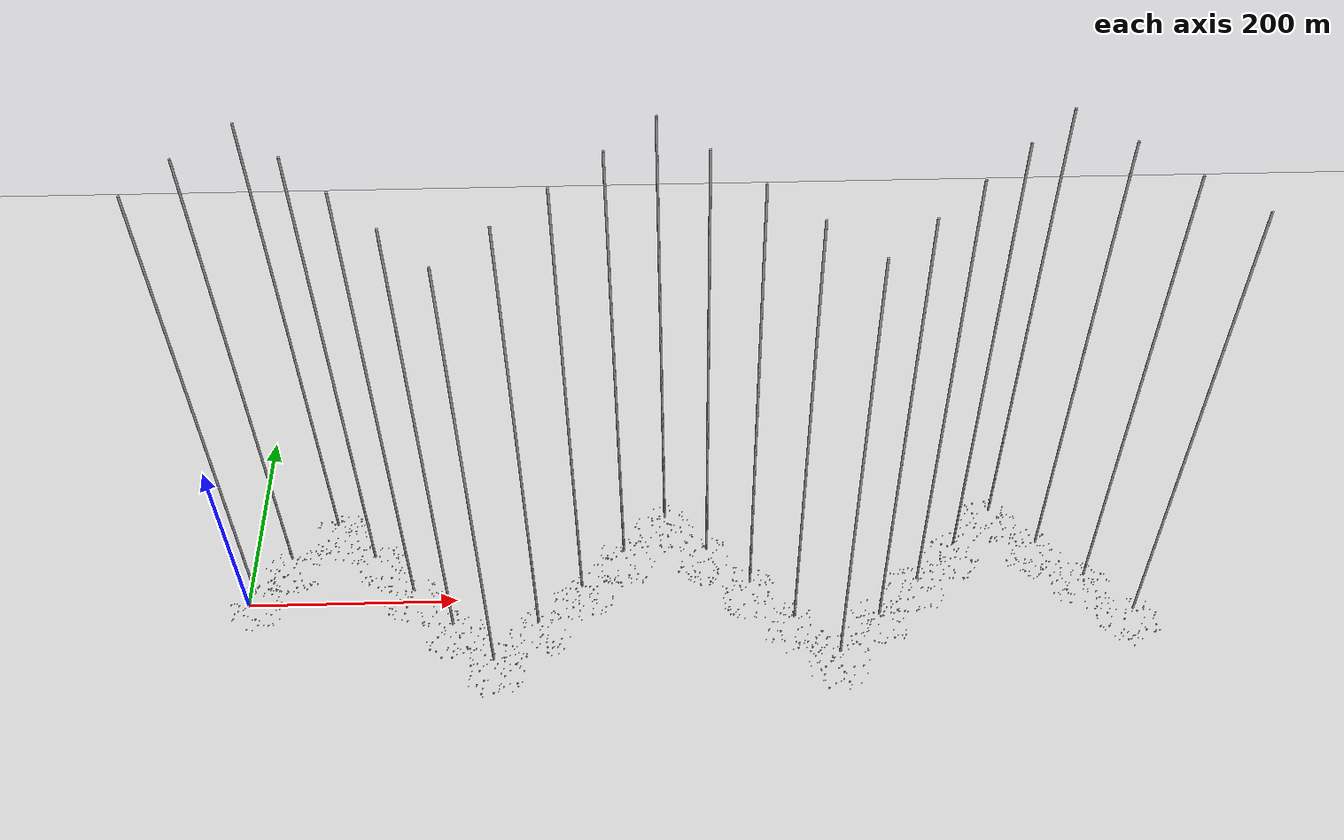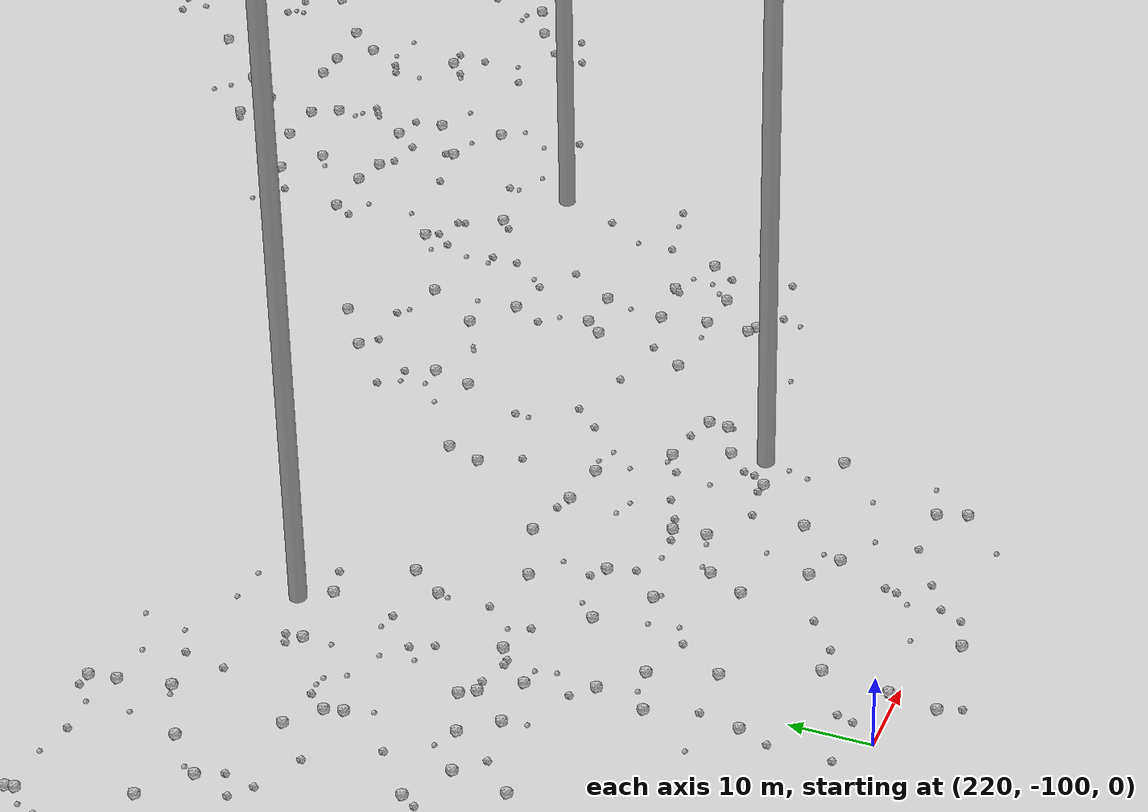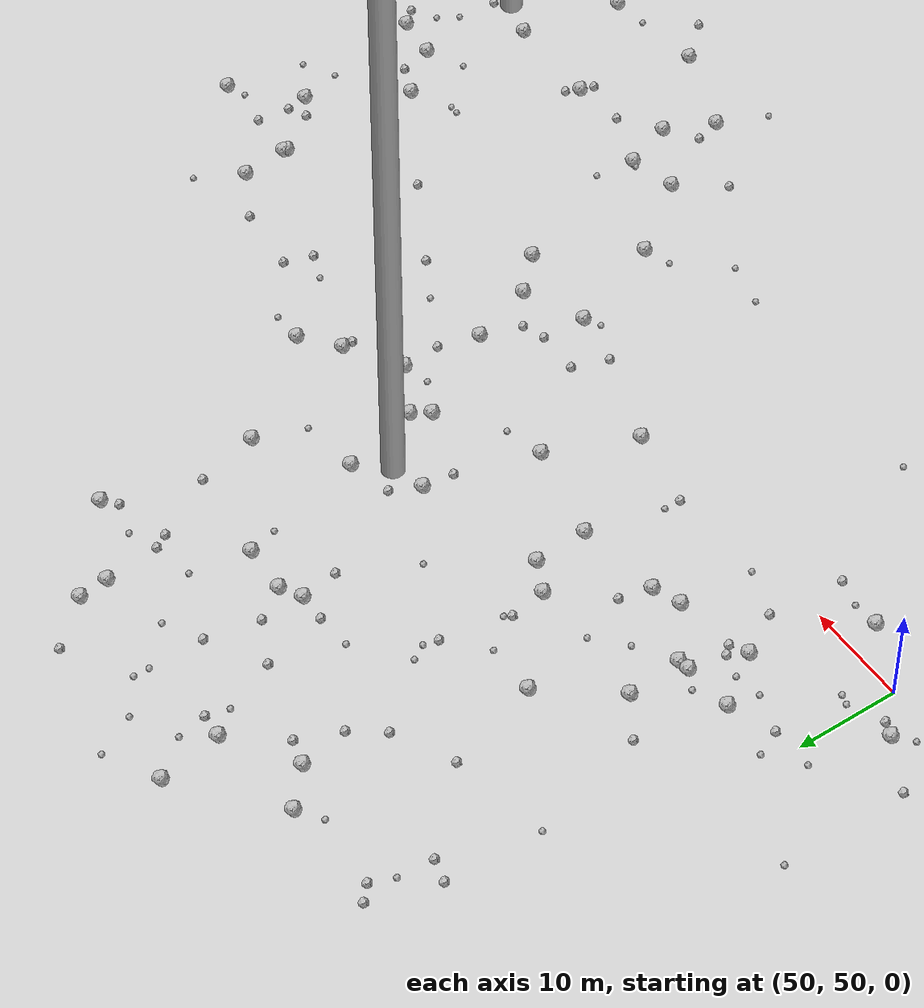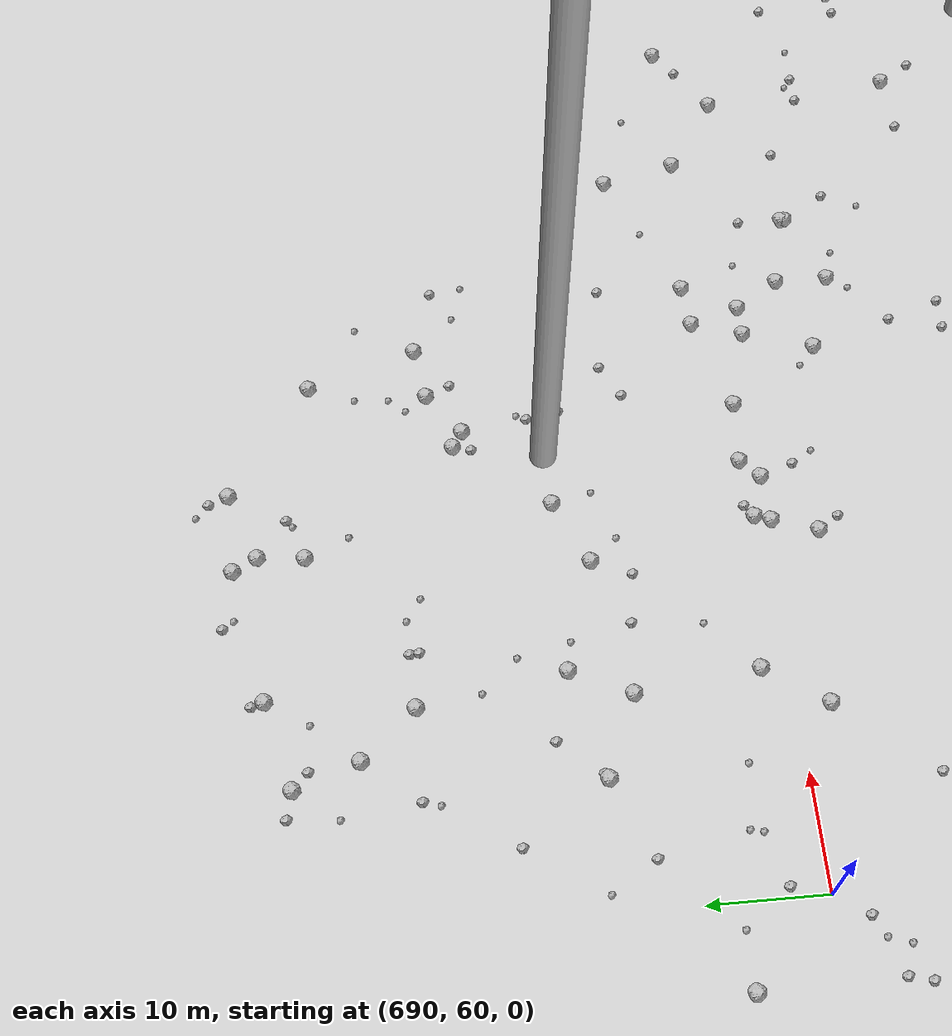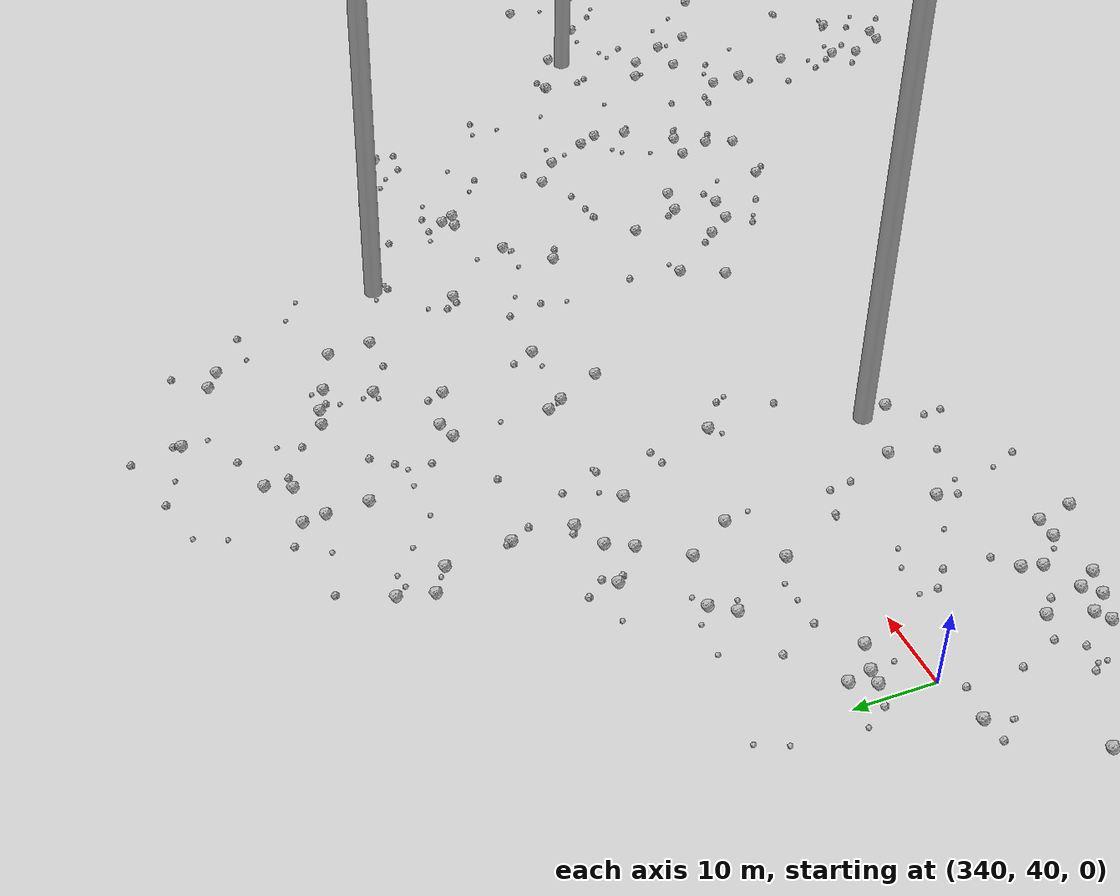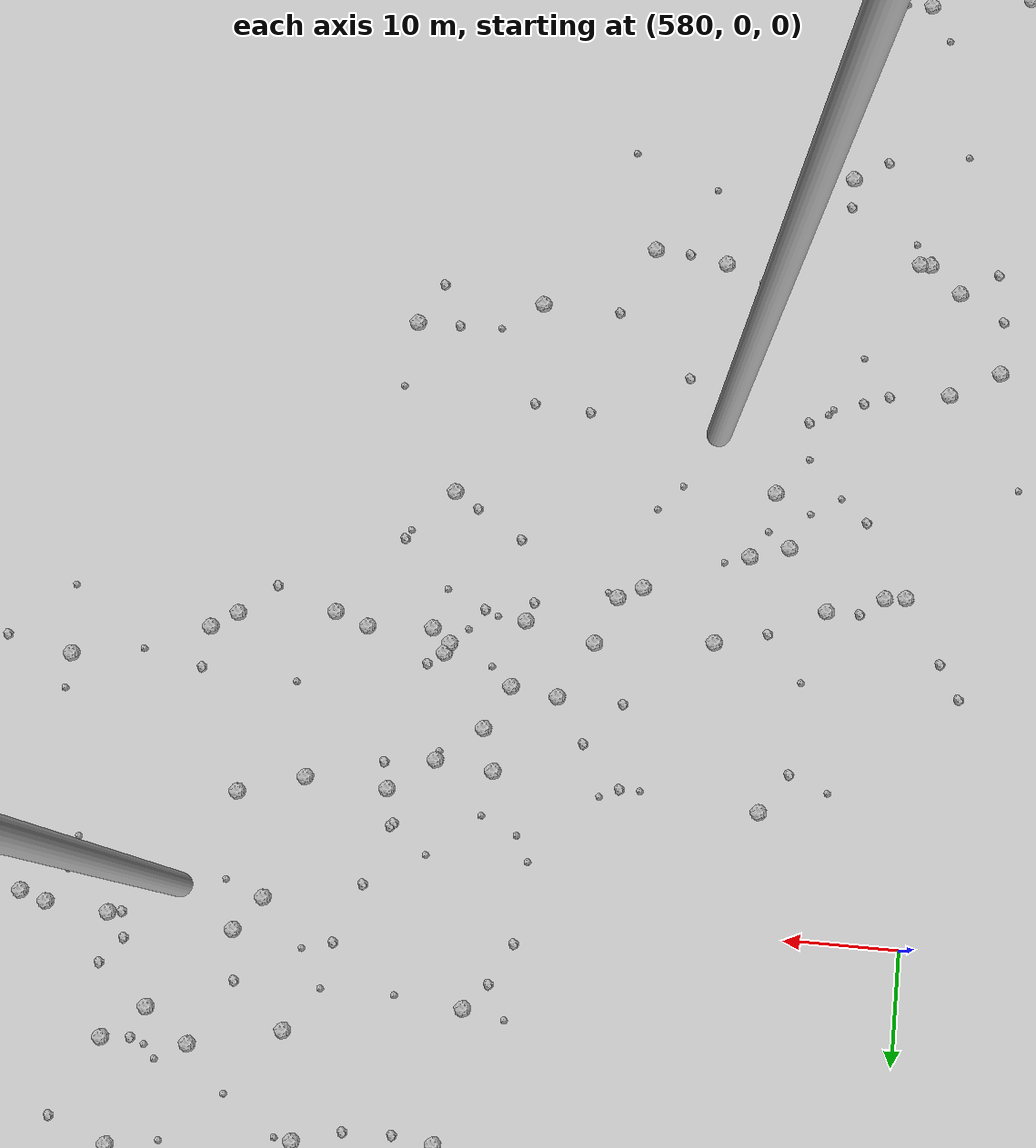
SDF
<sdf version="1.6">
 <world name="default">
  <include><uri>model://custom_ground</uri></include>
  <include><uri>model://sun</uri></include>
  <spherical_coordinates>
   <surface_model>EARTH_WGS84</surface_model>
   <latitude_deg>38.161479</latitude_deg>
   <longitude_deg>-122.454630</longitude_deg>
   <elevation>488.0</elevation>
   <heading_deg>90</heading_deg>
  </spherical_coordinates>
  <model name="rock1_0_0">
   <include><uri>model://rock1</uri><pose>34.692220365280605 12.527927428301489 0.5 0 0 0</pose></include>
  </model>
  <model name="rock1_0_1">
   <include><uri>model://rock1</uri><pose>8.420400885562579 -16.615798098021653 0.5 0 0 0</pose></include>
  </model>
  <model name="rock1_0_2">
   <include><uri>model://rock1</uri><pose>-17.06683805358835 0.5384646517541256 0.5 0 0 0</pose></include>
  </model>
  <model name="rock1_0_3">
   <include><uri>model://rock1</uri><pose>-1.4772260138726807 19.116353372316873 0.5 0 0 0</pose></include>
  </model>
  <model name="rock1_0_4">
   <include><uri>model://rock1</uri><pose>34.800081229509345 15.921887355699113 0.5 0 0 0</pose></include>
  </model>
  <model name="rock1_0_5">
   <include><uri>model://rock1</uri><pose>6.8038193167206416 21.59052578320982 0.5 0 0 0</pose></include>
  </model>
  <model name="rock1_0_6">
   <include><uri>model://rock1</uri><pose>22.725848736871413 -11.455604076115861 0.5 0 0 0</pose></include>
  </model>
  <model name="rock1_0_7">
   <include><uri>model://rock1</uri><pose>-6.206110380473902 20.26548987328318 0.5 0 0 0</pose></include>
  </model>
  <model name="rock1_0_8">
   <include><uri>model://rock1</uri><pose>28.094841797491256 -3.0002272057829984 0.5 0 0 0</pose></include>
  </model>
  <model name="rock1_0_9">
   <include><uri>model://rock1</uri><pose>-10.011091409006452 17.9424704147499 0.5 0 0 0</pose></include>
  </model>
  <model name="rock1_0_10">
   <include><uri>model://rock1</uri><pose>11.765073804513012 -23.134301102692234 0.5 0 0 0</pose></include>
  </model>
  <model name="rock1_0_11">
   <include><uri>model://rock1</uri><pose>5.612186752007002 20.43176234385279 0.5 0 0 0</pose></include>
  </model>
  <model name="rock1_0_12">
   <include><uri>model://rock1</uri><pose>1.3344057280815882 -27.78583141082697 0.5 0 0 0</pose></include>
  </model>
  <model name="rock1_0_13">
   <include><uri>model://rock1</uri><pose>-12.868221439911053 -15.734397181333328 0.5 0 0 0</pose></include>
  </model>
  <model name="rock1_0_14">
   <include><uri>model://rock1</uri><pose>0.01977153954779709 21.382518396277497 0.5 0 0 0</pose></include>
  </model>
  <model name="rock1_0_15">
   <include><uri>model://rock1</uri><pose>27.326544175636194 -0.11750851875581958 0.5 0 0 0</pose></include>
  </model>
  <model name="rock1_0_16">
   <include><uri>model://rock1</uri><pose>15.869887902540057 1.6668947294319274 0.5 0 0 0</pose></include>
  </model>
  <model name="rock1_0_17">
   <include><uri>model://rock1</uri><pose>12.157873640422679 -18.126366799314006 0.5 0 0 0</pose></include>
  </model>
  <model name="rock1_0_18">
   <include><uri>model://rock1</uri><pose>-3.572967481544662 -11.681449444241721 0.5 0 0 0</pose></include>
  </model>
  <model name="rock1_0_19">
   <include><uri>model://rock1</uri><pose>20.05507339208316 12.286010932311463 0.5 0 0 0</pose></include>
  </model>
  <model name="rock1_0_20">
   <include><uri>model://rock1</uri><pose>-9.233574346076205 -0.6792143595945248 0.5 0 0 0</pose></include>
  </model>
  <model name="rock1_0_21">
   <include><uri>model://rock1</uri><pose>2.203019770497413 13.224989192532014 0.5 0 0 0</pose></include>
  </model>
  <model name="rock1_0_22">
   <include><uri>model://rock1</uri><pose>16.421980121362104 18.116430850837155 0.5 0 0 0</pose></include>
  </model>
  <model name="rock1_0_23">
   <include><uri>model://rock1</uri><pose>-3.3811702638479133 2.5158046422523412 0.5 0 0 0</pose></include>
  </model>
  <model name="rock1_0_24">
   <include><uri>model://rock1</uri><pose>20.76555995975339 26.63342732501949 0.5 0 0 0</pose></include>
  </model>
  <model name="rock1_0_25">
   <include><uri>model://rock1</uri><pose>21.938502514300197 -23.856296785039106 0.5 0 0 0</pose></include>
  </model>
  <model name="rock1_0_26">
   <include><uri>model://rock1</uri><pose>1.7440070879162164 7.201422855681642 0.5 0 0 0</pose></include>
  </model>
  <model name="rock2_0_0">
   <include><uri>model://rock2</uri><pose>-0.7233027793532933 18.21600601262658 0.3 0 0 0</pose></include>
  </model>
  <model name="rock2_0_1">
   <include><uri>model://rock2</uri><pose>14.945054263640955 2.8341585281367685 0.3 0 0 0</pose></include>
  </model>
  <model name="rock2_0_2">
   <include><uri>model://rock2</uri><pose>26.833498158773793 9.32702853660684 0.3 0 0 0</pose></include>
  </model>
  <model name="rock2_0_3">
   <include><uri>model://rock2</uri><pose>0.4495500964042414 -12.931658812807683 0.3 0 0 0</pose></include>
  </model>
  <model name="rock2_0_4">
   <include><uri>model://rock2</uri><pose>-6.141928622967615 1.262913146766948 0.3 0 0 0</pose></include>
  </model>
  <model name="rock2_0_5">
   <include><uri>model://rock2</uri><pose>5.046543993866493 24.74949543613058 0.3 0 0 0</pose></include>
  </model>
  <model name="rock2_0_6">
   <include><uri>model://rock2</uri><pose>14.163443647440381 6.841151773640355 0.3 0 0 0</pose></include>
  </model>
  <model name="rock2_0_7">
   <include><uri>model://rock2</uri><pose>30.411871924811074 3.0899953978889627 0.3 0 0 0</pose></include>
  </model>
  <model name="rock2_0_8">
   <include><uri>model://rock2</uri><pose>37.575421906696945 10.777000375006914 0.3 0 0 0</pose></include>
  </model>
  <model name="rock2_0_9">
   <include><uri>model://rock2</uri><pose>5.891523847701265 20.499522083019812 0.3 0 0 0</pose></include>
  </model>
  <model name="rock2_0_10">
   <include><uri>model://rock2</uri><pose>18.488402877802947 16.491467910281727 0.3 0 0 0</pose></include>
  </model>
  <model name="rock2_0_11">
   <include><uri>model://rock2</uri><pose>26.804906964189293 -6.454121145107841 0.3 0 0 0</pose></include>
  </model>
  <model name="rock2_0_12">
   <include><uri>model://rock2</uri><pose>-3.500473736422716 -3.0628072755379847 0.3 0 0 0</pose></include>
  </model>
  <model name="rock2_0_13">
   <include><uri>model://rock2</uri><pose>-12.552281764703896 -9.755175839459746 0.3 0 0 0</pose></include>
  </model>
  <model name="rock2_0_14">
   <include><uri>model://rock2</uri><pose>-1.3998401460169454 4.551954727645736 0.3 0 0 0</pose></include>
  </model>
  <model name="rock2_0_15">
   <include><uri>model://rock2</uri><pose>-4.514586650522428 -5.012370253686658 0.3 0 0 0</pose></include>
  </model>
  <model name="rock2_0_16">
   <include><uri>model://rock2</uri><pose>0.5683895260113943 -12.853798266071127 0.3 0 0 0</pose></include>
  </model>
  <model name="rock2_0_17">
   <include><uri>model://rock2</uri><pose>-13.706983908351354 -17.35119797360236 0.3 0 0 0</pose></include>
  </model>
  <model name="rock2_0_18">
   <include><uri>model://rock2</uri><pose>6.500779797055355 23.466711791661332 0.3 0 0 0</pose></include>
  </model>
  <model name="rock2_0_19">
   <include><uri>model://rock2</uri><pose>12.69281182531688 13.33000652076555 0.3 0 0 0</pose></include>
  </model>
  <model name="rock2_0_20">
   <include><uri>model://rock2</uri><pose>-9.440778264519853 -6.7650476365882355 0.3 0 0 0</pose></include>
  </model>
  <model name="rock2_0_21">
   <include><uri>model://rock2</uri><pose>26.30514204384437 5.2745356945108455 0.3 0 0 0</pose></include>
  </model>
  <model name="rock2_0_22">
   <include><uri>model://rock2</uri><pose>31.500594971031724 -16.180954645228027 0.3 0 0 0</pose></include>
  </model>
  <model name="rock2_0_23">
   <include><uri>model://rock2</uri><pose>21.06361786209029 -23.51889860713351 0.3 0 0 0</pose></include>
  </model>
  <model name="rock2_0_24">
   <include><uri>model://rock2</uri><pose>6.850953067403125 -28.738910709627024 0.3 0 0 0</pose></include>
  </model>
  <model name="rock2_0_25">
   <include><uri>model://rock2</uri><pose>34.05822209163501 11.34655415293608 0.3 0 0 0</pose></include>
  </model>
  <model name="rock2_0_26">
   <include><uri>model://rock2</uri><pose>5.643471254645792 -16.985783407567205 0.3 0 0 0</pose></include>
  </model>
  <model name="rock3_0_0">
   <include><uri>model://rock3</uri><pose>25.313175054385006 -21.491094941306454 0.2 0 0 0</pose></include>
  </model>
  <model name="rock3_0_1">
   <include><uri>model://rock3</uri><pose>17.501785861347756 -4.622185434053176 0.2 0 0 0</pose></include>
  </model>
  <model name="rock3_0_2">
   <include><uri>model://rock3</uri><pose>-0.9916566804606433 25.01239010923672 0.2 0 0 0</pose></include>
  </model>
  <model name="rock3_0_3">
   <include><uri>model://rock3</uri><pose>17.022799402570463 -23.27864131653598 0.2 0 0 0</pose></include>
  </model>
  <model name="rock3_0_4">
   <include><uri>model://rock3</uri><pose>26.172359986234234 25.196335910639682 0.2 0 0 0</pose></include>
  </model>
  <model name="rock3_0_5">
   <include><uri>model://rock3</uri><pose>19.212711150312437 13.27541525587447 0.2 0 0 0</pose></include>
  </model>
  <model name="rock3_0_6">
   <include><uri>model://rock3</uri><pose>29.923786678601836 -5.165361718427828 0.2 0 0 0</pose></include>
  </model>
  <model name="rock3_0_7">
   <include><uri>model://rock3</uri><pose>-10.978741549469351 6.605177380820038 0.2 0 0 0</pose></include>
  </model>
  <model name="rock3_0_8">
   <include><uri>model://rock3</uri><pose>-4.249929001339439 -22.14388988113959 0.2 0 0 0</pose></include>
  </model>
  <model name="rock3_0_9">
   <include><uri>model://rock3</uri><pose>17.735954315564562 -10.23670746405432 0.2 0 0 0</pose></include>
  </model>
  <model name="rock3_0_10">
   <include><uri>model://rock3</uri><pose>21.411530578029193 3.4010500800544534 0.2 0 0 0</pose></include>
  </model>
  <model name="rock3_0_11">
   <include><uri>model://rock3</uri><pose>-11.800459037783588 2.393938946503468 0.2 0 0 0</pose></include>
  </model>
  <model name="rock3_0_12">
   <include><uri>model://rock3</uri><pose>26.43812892332359 -23.582717926936112 0.2 0 0 0</pose></include>
  </model>
  <model name="rock3_0_13">
   <include><uri>model://rock3</uri><pose>31.546721315343035 5.072895962205564 0.2 0 0 0</pose></include>
  </model>
  <model name="rock3_0_14">
   <include><uri>model://rock3</uri><pose>28.824876677567737 15.141823285167597 0.2 0 0 0</pose></include>
  </model>
  <model name="rock3_0_15">
   <include><uri>model://rock3</uri><pose>-15.549156884648337 6.632143010573621 0.2 0 0 0</pose></include>
  </model>
  <model name="rock3_0_16">
   <include><uri>model://rock3</uri><pose>22.402205568739525 0.6921048905899703 0.2 0 0 0</pose></include>
  </model>
  <model name="rock3_0_17">
   <include><uri>model://rock3</uri><pose>19.521777923450237 -13.032816901845838 0.2 0 0 0</pose></include>
  </model>
  <model name="rock3_0_18">
   <include><uri>model://rock3</uri><pose>11.672368094684614 -5.456969012113156 0.2 0 0 0</pose></include>
  </model>
  <model name="rock3_0_19">
   <include><uri>model://rock3</uri><pose>1.2240427746204467 -2.9095371464833235 0.2 0 0 0</pose></include>
  </model>
  <model name="rock3_0_20">
   <include><uri>model://rock3</uri><pose>5.196031052260771 -14.463094816127182 0.2 0 0 0</pose></include>
  </model>
  <model name="rock3_0_21">
   <include><uri>model://rock3</uri><pose>-14.550242088564275 2.1808170323545255 0.2 0 0 0</pose></include>
  </model>
  <model name="rock3_0_22">
   <include><uri>model://rock3</uri><pose>-2.185955014298507 20.149631556710688 0.2 0 0 0</pose></include>
  </model>
  <model name="rock3_0_23">
   <include><uri>model://rock3</uri><pose>7.147095204875125 21.809028301292763 0.2 0 0 0</pose></include>
  </model>
  <model name="rock3_0_24">
   <include><uri>model://rock3</uri><pose>26.15265292741958 21.977785382903683 0.2 0 0 0</pose></include>
  </model>
  <model name="rock3_0_25">
   <include><uri>model://rock3</uri><pose>12.256458568588577 10.705477784012288 0.2 0 0 0</pose></include>
  </model>
  <model name="rock3_0_26">
   <include><uri>model://rock3</uri><pose>24.886091224811288 0.7546512642191452 0.2 0 0 0</pose></include>
  </model>
  <model name="rock1_1_0">
   <include><uri>model://rock1</uri><pose>32.54559407592569 34.67825716328427 0.5 0 0 0</pose></include>
  </model>
  <model name="rock1_1_1">
   <include><uri>model://rock1</uri><pose>63.14341531235511 23.14834389085012 0.5 0 0 0</pose></include>
  </model>
  <model name="rock1_1_2">
   <include><uri>model://rock1</uri><pose>45.30905566410216 13.484505838570307 0.5 0 0 0</pose></include>
  </model>
  <model name="rock1_1_3">
   <include><uri>model://rock1</uri><pose>50.69425541874034 19.231453288926836 0.5 0 0 0</pose></include>
  </model>
  <model name="rock1_1_4">
   <include><uri>model://rock1</uri><pose>18.76162722104464 18.814009077257026 0.5 0 0 0</pose></include>
  </model>
  <model name="rock1_1_5">
   <include><uri>model://rock1</uri><pose>28.853096124036952 32.283235767350675 0.5 0 0 0</pose></include>
  </model>
  <model name="rock1_1_6">
   <include><uri>model://rock1</uri><pose>23.65735539952623 16.497136679772595 0.5 0 0 0</pose></include>
  </model>
  <model name="rock1_1_7">
   <include><uri>model://rock1</uri><pose>40.69804700112369 26.862821806834464 0.5 0 0 0</pose></include>
  </model>
  <model name="rock1_1_8">
   <include><uri>model://rock1</uri><pose>19.989564536299255 36.45089888195713 0.5 0 0 0</pose></include>
  </model>
  <model name="rock1_1_9">
   <include><uri>model://rock1</uri><pose>24.73104857152639 16.80392389333704 0.5 0 0 0</pose></include>
  </model>
  <model name="rock1_1_10">
   <include><uri>model://rock1</uri><pose>17.562232820820128 28.459874552195675 0.5 0 0 0</pose></include>
  </model>
  <model name="rock1_1_11">
   <include><uri>model://rock1</uri><pose>23.877130637654247 39.963227563632586 0.5 0 0 0</pose></include>
  </model>
  <model name="rock1_1_12">
   <include><uri>model://rock1</uri><pose>46.879155910785855 27.43620454263273 0.5 0 0 0</pose></include>
  </model>
  <model name="rock1_1_13">
   <include><uri>model://rock1</uri><pose>37.81344792772107 43.35494209543964 0.5 0 0 0</pose></include>
  </model>
  <model name="rock1_1_14">
   <include><uri>model://rock1</uri><pose>19.9884697637777 30.501717145170403 0.5 0 0 0</pose></include>
  </model>
  <model name="rock1_1_15">
   <include><uri>model://rock1</uri><pose>46.49936865685001 53.248080110038394 0.5 0 0 0</pose></include>
  </model>
  <model name="rock1_1_16">
   <include><uri>model://rock1</uri><pose>56.510436025857565 46.770942380252265 0.5 0 0 0</pose></include>
  </model>
  <model name="rock1_1_17">
   <include><uri>model://rock1</uri><pose>40.13381602043647 53.055967237610204 0.5 0 0 0</pose></include>
  </model>
  <model name="rock1_1_18">
   <include><uri>model://rock1</uri><pose>27.41243854652357 15.912154492137791 0.5 0 0 0</pose></include>
  </model>
  <model name="rock1_1_19">
   <include><uri>model://rock1</uri><pose>10.528648023586367 42.79485479722916 0.5 0 0 0</pose></include>
  </model>
  <model name="rock1_1_20">
   <include><uri>model://rock1</uri><pose>15.329707600249234 39.848892328188576 0.5 0 0 0</pose></include>
  </model>
  <model name="rock1_1_21">
   <include><uri>model://rock1</uri><pose>43.385480892785175 19.509523519219787 0.5 0 0 0</pose></include>
  </model>
  <model name="rock1_1_22">
   <include><uri>model://rock1</uri><pose>35.942802989276366 14.486187436797248 0.5 0 0 0</pose></include>
  </model>
  <model name="rock1_1_23">
   <include><uri>model://rock1</uri><pose>30.96014628281902 60.7614095223835 0.5 0 0 0</pose></include>
  </model>
  <model name="rock1_1_24">
   <include><uri>model://rock1</uri><pose>14.845623269932817 26.35564424855182 0.5 0 0 0</pose></include>
  </model>
  <model name="rock1_1_25">
   <include><uri>model://rock1</uri><pose>56.76195080802214 22.13440186618537 0.5 0 0 0</pose></include>
  </model>
  <model name="rock1_1_26">
   <include><uri>model://rock1</uri><pose>60.136302562891245 57.56145042928673 0.5 0 0 0</pose></include>
  </model>
  <model name="rock2_1_0">
   <include><uri>model://rock2</uri><pose>30.42987788392766 53.811534046395145 0.3 0 0 0</pose></include>
  </model>
  <model name="rock2_1_1">
   <include><uri>model://rock2</uri><pose>20.727951952193166 25.056689675600552 0.3 0 0 0</pose></include>
  </model>
  <model name="rock2_1_2">
   <include><uri>model://rock2</uri><pose>57.89055173963312 26.438477885759085 0.3 0 0 0</pose></include>
  </model>
  <model name="rock2_1_3">
   <include><uri>model://rock2</uri><pose>19.314213054995847 18.8217359674619 0.3 0 0 0</pose></include>
  </model>
  <model name="rock2_1_4">
   <include><uri>model://rock2</uri><pose>21.58855337037432 27.05942832415948 0.3 0 0 0</pose></include>
  </model>
  <model name="rock2_1_5">
   <include><uri>model://rock2</uri><pose>23.384267574522468 39.89111378023999 0.3 0 0 0</pose></include>
  </model>
  <model name="rock2_1_6">
   <include><uri>model://rock2</uri><pose>61.817348630769885 58.37921263746872 0.3 0 0 0</pose></include>
  </model>
  <model name="rock2_1_7">
   <include><uri>model://rock2</uri><pose>40.63144012281849 15.163503720348716 0.3 0 0 0</pose></include>
  </model>
  <model name="rock2_1_8">
   <include><uri>model://rock2</uri><pose>39.08706404347754 27.43787058717925 0.3 0 0 0</pose></include>
  </model>
  <model name="rock2_1_9">
   <include><uri>model://rock2</uri><pose>62.44480269715137 53.53162579900152 0.3 0 0 0</pose></include>
  </model>
  <model name="rock2_1_10">
   <include><uri>model://rock2</uri><pose>44.09372559829005 36.28370719107235 0.3 0 0 0</pose></include>
  </model>
  <model name="rock2_1_11">
   <include><uri>model://rock2</uri><pose>16.024485687797835 52.13706014095449 0.3 0 0 0</pose></include>
  </model>
  <model name="rock2_1_12">
   <include><uri>model://rock2</uri><pose>20.941586140965132 16.844458913711605 0.3 0 0 0</pose></include>
  </model>
  <model name="rock2_1_13">
   <include><uri>model://rock2</uri><pose>52.32562176937561 60.77191815174291 0.3 0 0 0</pose></include>
  </model>
  <model name="rock2_1_14">
   <include><uri>model://rock2</uri><pose>47.890917378152956 52.6524282963333 0.3 0 0 0</pose></include>
  </model>
  <model name="rock2_1_15">
   <include><uri>model://rock2</uri><pose>55.396928836001244 23.786402155243735 0.3 0 0 0</pose></include>
  </model>
  <model name="rock2_1_16">
   <include><uri>model://rock2</uri><pose>15.862225187795644 50.5954789504158 0.3 0 0 0</pose></include>
  </model>
  <model name="rock2_1_17">
   <include><uri>model://rock2</uri><pose>45.04785076070343 40.63200444052468 0.3 0 0 0</pose></include>
  </model>
  <model name="rock2_1_18">
   <include><uri>model://rock2</uri><pose>39.30689329293017 48.2276555863824 0.3 0 0 0</pose></include>
  </model>
  <model name="rock2_1_19">
   <include><uri>model://rock2</uri><pose>61.78752275039525 46.154175591495644 0.3 0 0 0</pose></include>
  </model>
  <model name="rock2_1_20">
   <include><uri>model://rock2</uri><pose>41.398432182937704 56.011770939765064 0.3 0 0 0</pose></include>
  </model>
  <model name="rock2_1_21">
   <include><uri>model://rock2</uri><pose>29.88065404328917 32.560873104835196 0.3 0 0 0</pose></include>
  </model>
  <model name="rock2_1_22">
   <include><uri>model://rock2</uri><pose>26.158440708980923 49.861965179663166 0.3 0 0 0</pose></include>
  </model>
  <model name="rock2_1_23">
   <include><uri>model://rock2</uri><pose>21.22704049819106 42.15292767620711 0.3 0 0 0</pose></include>
  </model>
  <model name="rock2_1_24">
   <include><uri>model://rock2</uri><pose>23.334989398875905 17.999434684139516 0.3 0 0 0</pose></include>
  </model>
  <model name="rock2_1_25">
   <include><uri>model://rock2</uri><pose>53.10611748134886 17.72209605746681 0.3 0 0 0</pose></include>
  </model>
  <model name="rock2_1_26">
   <include><uri>model://rock2</uri><pose>27.094355066096043 47.16824855327847 0.3 0 0 0</pose></include>
  </model>
  <model name="rock3_1_0">
   <include><uri>model://rock3</uri><pose>19.80056661936604 25.173799592748907 0.2 0 0 0</pose></include>
  </model>
  <model name="rock3_1_1">
   <include><uri>model://rock3</uri><pose>41.32052624025257 68.38304772530745 0.2 0 0 0</pose></include>
  </model>
  <model name="rock3_1_2">
   <include><uri>model://rock3</uri><pose>39.96158957762567 25.27332276388698 0.2 0 0 0</pose></include>
  </model>
  <model name="rock3_1_3">
   <include><uri>model://rock3</uri><pose>35.27741641381084 51.57682140509226 0.2 0 0 0</pose></include>
  </model>
  <model name="rock3_1_4">
   <include><uri>model://rock3</uri><pose>51.17739618362082 63.16199097658252 0.2 0 0 0</pose></include>
  </model>
  <model name="rock3_1_5">
   <include><uri>model://rock3</uri><pose>41.18087224120333 22.922376218436412 0.2 0 0 0</pose></include>
  </model>
  <model name="rock3_1_6">
   <include><uri>model://rock3</uri><pose>67.08601555653277 51.79358328263447 0.2 0 0 0</pose></include>
  </model>
  <model name="rock3_1_7">
   <include><uri>model://rock3</uri><pose>44.05495358361635 25.76807529997783 0.2 0 0 0</pose></include>
  </model>
  <model name="rock3_1_8">
   <include><uri>model://rock3</uri><pose>48.08859827524133 60.62686992359049 0.2 0 0 0</pose></include>
  </model>
  <model name="rock3_1_9">
   <include><uri>model://rock3</uri><pose>56.11997817033654 59.447084431541725 0.2 0 0 0</pose></include>
  </model>
  <model name="rock3_1_10">
   <include><uri>model://rock3</uri><pose>49.4043981773208 22.2527670296651 0.2 0 0 0</pose></include>
  </model>
  <model name="rock3_1_11">
   <include><uri>model://rock3</uri><pose>44.02522269378579 12.217854800621488 0.2 0 0 0</pose></include>
  </model>
  <model name="rock3_1_12">
   <include><uri>model://rock3</uri><pose>44.84663754577865 51.74349253429171 0.2 0 0 0</pose></include>
  </model>
  <model name="rock3_1_13">
   <include><uri>model://rock3</uri><pose>55.36709627973844 17.56245439908045 0.2 0 0 0</pose></include>
  </model>
  <model name="rock3_1_14">
   <include><uri>model://rock3</uri><pose>29.942239222290485 50.10197609961961 0.2 0 0 0</pose></include>
  </model>
  <model name="rock3_1_15">
   <include><uri>model://rock3</uri><pose>29.614800214245125 39.799028522985935 0.2 0 0 0</pose></include>
  </model>
  <model name="rock3_1_16">
   <include><uri>model://rock3</uri><pose>53.64914734087039 16.599375396282106 0.2 0 0 0</pose></include>
  </model>
  <model name="rock3_1_17">
   <include><uri>model://rock3</uri><pose>23.09762318438354 59.73392088940104 0.2 0 0 0</pose></include>
  </model>
  <model name="rock3_1_18">
   <include><uri>model://rock3</uri><pose>20.496489447299155 32.5376880873863 0.2 0 0 0</pose></include>
  </model>
  <model name="rock3_1_19">
   <include><uri>model://rock3</uri><pose>51.221125261926524 54.08181019052927 0.2 0 0 0</pose></include>
  </model>
  <model name="rock3_1_20">
   <include><uri>model://rock3</uri><pose>22.573740950713997 55.68705566432002 0.2 0 0 0</pose></include>
  </model>
  <model name="rock3_1_21">
   <include><uri>model://rock3</uri><pose>50.76441863073592 30.99811225149653 0.2 0 0 0</pose></include>
  </model>
  <model name="rock3_1_22">
   <include><uri>model://rock3</uri><pose>23.851164829732028 22.832003888133073 0.2 0 0 0</pose></include>
  </model>
  <model name="rock3_1_23">
   <include><uri>model://rock3</uri><pose>59.08993366505998 46.80327336219302 0.2 0 0 0</pose></include>
  </model>
  <model name="rock3_1_24">
   <include><uri>model://rock3</uri><pose>68.90912435362532 33.53011696146566 0.2 0 0 0</pose></include>
  </model>
  <model name="rock3_1_25">
   <include><uri>model://rock3</uri><pose>60.0343302575144 26.250337052835246 0.2 0 0 0</pose></include>
  </model>
  <model name="rock3_1_26">
   <include><uri>model://rock3</uri><pose>52.199563368034426 53.75669128764821 0.2 0 0 0</pose></include>
  </model>
  <model name="rock1_2_0">
   <include><uri>model://rock1</uri><pose>67.71815011901009 75.0808054832239 0.5 0 0 0</pose></include>
  </model>
  <model name="rock1_2_1">
   <include><uri>model://rock1</uri><pose>67.75224821967511 59.08217392973975 0.5 0 0 0</pose></include>
  </model>
  <model name="rock1_2_2">
   <include><uri>model://rock1</uri><pose>98.03289207899508 97.90817300546135 0.5 0 0 0</pose></include>
  </model>
  <model name="rock1_2_3">
   <include><uri>model://rock1</uri><pose>104.4885669923318 79.02509014093619 0.5 0 0 0</pose></include>
  </model>
  <model name="rock1_2_4">
   <include><uri>model://rock1</uri><pose>70.48447108483828 60.04790989870398 0.5 0 0 0</pose></include>
  </model>
  <model name="rock1_2_5">
   <include><uri>model://rock1</uri><pose>78.43310991872481 99.03970557412204 0.5 0 0 0</pose></include>
  </model>
  <model name="rock1_2_6">
   <include><uri>model://rock1</uri><pose>78.61219913443874 66.42727994218384 0.5 0 0 0</pose></include>
  </model>
  <model name="rock1_2_7">
   <include><uri>model://rock1</uri><pose>98.98606392557477 65.82775969996834 0.5 0 0 0</pose></include>
  </model>
  <model name="rock1_2_8">
   <include><uri>model://rock1</uri><pose>75.47705043951252 68.01651099705899 0.5 0 0 0</pose></include>
  </model>
  <model name="rock1_2_9">
   <include><uri>model://rock1</uri><pose>96.92136294289705 73.48361754539302 0.5 0 0 0</pose></include>
  </model>
  <model name="rock1_2_10">
   <include><uri>model://rock1</uri><pose>105.98356379648808 93.79188679664458 0.5 0 0 0</pose></include>
  </model>
  <model name="rock1_2_11">
   <include><uri>model://rock1</uri><pose>62.87832139805457 62.94777222368559 0.5 0 0 0</pose></include>
  </model>
  <model name="rock1_2_12">
   <include><uri>model://rock1</uri><pose>97.68626977896605 100.80938188157378 0.5 0 0 0</pose></include>
  </model>
  <model name="rock1_2_13">
   <include><uri>model://rock1</uri><pose>71.9647691440986 94.90280255401694 0.5 0 0 0</pose></include>
  </model>
  <model name="rock1_2_14">
   <include><uri>model://rock1</uri><pose>78.90034136319161 61.10376603383625 0.5 0 0 0</pose></include>
  </model>
  <model name="rock1_2_15">
   <include><uri>model://rock1</uri><pose>93.60287771654856 86.03820006482061 0.5 0 0 0</pose></include>
  </model>
  <model name="rock1_2_16">
   <include><uri>model://rock1</uri><pose>97.86968068468879 64.14019760162213 0.5 0 0 0</pose></include>
  </model>
  <model name="rock1_2_17">
   <include><uri>model://rock1</uri><pose>77.33469723411122 105.25377784290606 0.5 0 0 0</pose></include>
  </model>
  <model name="rock1_2_18">
   <include><uri>model://rock1</uri><pose>84.92795789249342 50.51709773257816 0.5 0 0 0</pose></include>
  </model>
  <model name="rock1_2_19">
   <include><uri>model://rock1</uri><pose>61.741215649209906 62.79658339422721 0.5 0 0 0</pose></include>
  </model>
  <model name="rock1_2_20">
   <include><uri>model://rock1</uri><pose>88.46669177393893 58.92737481350919 0.5 0 0 0</pose></include>
  </model>
  <model name="rock1_2_21">
   <include><uri>model://rock1</uri><pose>91.21303635624064 69.71538953755079 0.5 0 0 0</pose></include>
  </model>
  <model name="rock1_2_22">
   <include><uri>model://rock1</uri><pose>88.85157824300327 86.29675328472499 0.5 0 0 0</pose></include>
  </model>
  <model name="rock1_2_23">
   <include><uri>model://rock1</uri><pose>56.77414861580075 62.43323215133046 0.5 0 0 0</pose></include>
  </model>
  <model name="rock1_2_24">
   <include><uri>model://rock1</uri><pose>68.53639640237128 98.00691971248676 0.5 0 0 0</pose></include>
  </model>
  <model name="rock1_2_25">
   <include><uri>model://rock1</uri><pose>62.41400817204361 68.40871830711504 0.5 0 0 0</pose></include>
  </model>
  <model name="rock1_2_26">
   <include><uri>model://rock1</uri><pose>86.80129983827068 85.13955796532264 0.5 0 0 0</pose></include>
  </model>
  <model name="rock2_2_0">
   <include><uri>model://rock2</uri><pose>55.62573098609187 91.89648827821529 0.3 0 0 0</pose></include>
  </model>
  <model name="rock2_2_1">
   <include><uri>model://rock2</uri><pose>76.2572592127731 78.2328123404717 0.3 0 0 0</pose></include>
  </model>
  <model name="rock2_2_2">
   <include><uri>model://rock2</uri><pose>74.46402975326077 94.17048124518985 0.3 0 0 0</pose></include>
  </model>
  <model name="rock2_2_3">
   <include><uri>model://rock2</uri><pose>93.82287315255408 105.08270448893417 0.3 0 0 0</pose></include>
  </model>
  <model name="rock2_2_4">
   <include><uri>model://rock2</uri><pose>59.06977235106816 97.06860223836708 0.3 0 0 0</pose></include>
  </model>
  <model name="rock2_2_5">
   <include><uri>model://rock2</uri><pose>99.39746102772622 91.13189341784633 0.3 0 0 0</pose></include>
  </model>
  <model name="rock2_2_6">
   <include><uri>model://rock2</uri><pose>87.73676672466769 94.5777724967931 0.3 0 0 0</pose></include>
  </model>
  <model name="rock2_2_7">
   <include><uri>model://rock2</uri><pose>83.94484743001375 85.16104155399435 0.3 0 0 0</pose></include>
  </model>
  <model name="rock2_2_8">
   <include><uri>model://rock2</uri><pose>64.85667534648218 84.29671235321518 0.3 0 0 0</pose></include>
  </model>
  <model name="rock2_2_9">
   <include><uri>model://rock2</uri><pose>57.669199772703564 98.36658749348447 0.3 0 0 0</pose></include>
  </model>
  <model name="rock2_2_10">
   <include><uri>model://rock2</uri><pose>77.00837529234984 52.11984763788931 0.3 0 0 0</pose></include>
  </model>
  <model name="rock2_2_11">
   <include><uri>model://rock2</uri><pose>72.78359175905511 90.09383598146451 0.3 0 0 0</pose></include>
  </model>
  <model name="rock2_2_12">
   <include><uri>model://rock2</uri><pose>74.8539943837249 71.59235507657164 0.3 0 0 0</pose></include>
  </model>
  <model name="rock2_2_13">
   <include><uri>model://rock2</uri><pose>57.905144060772734 91.31534457857961 0.3 0 0 0</pose></include>
  </model>
  <model name="rock2_2_14">
   <include><uri>model://rock2</uri><pose>80.75468961404276 98.81462915157539 0.3 0 0 0</pose></include>
  </model>
  <model name="rock2_2_15">
   <include><uri>model://rock2</uri><pose>102.88703776851885 85.09615646445478 0.3 0 0 0</pose></include>
  </model>
  <model name="rock2_2_16">
   <include><uri>model://rock2</uri><pose>92.5203988759053 72.4361549058354 0.3 0 0 0</pose></include>
  </model>
  <model name="rock2_2_17">
   <include><uri>model://rock2</uri><pose>71.2032325089281 63.08927439502908 0.3 0 0 0</pose></include>
  </model>
  <model name="rock2_2_18">
   <include><uri>model://rock2</uri><pose>70.55182024876967 87.14116207744871 0.3 0 0 0</pose></include>
  </model>
  <model name="rock2_2_19">
   <include><uri>model://rock2</uri><pose>82.3662142566096 91.51774108393391 0.3 0 0 0</pose></include>
  </model>
  <model name="rock2_2_20">
   <include><uri>model://rock2</uri><pose>86.66848654996963 89.3619009610041 0.3 0 0 0</pose></include>
  </model>
  <model name="rock2_2_21">
   <include><uri>model://rock2</uri><pose>104.64805242085258 92.58173288805364 0.3 0 0 0</pose></include>
  </model>
  <model name="rock2_2_22">
   <include><uri>model://rock2</uri><pose>87.36907641008415 81.39822172802387 0.3 0 0 0</pose></include>
  </model>
  <model name="rock2_2_23">
   <include><uri>model://rock2</uri><pose>98.58678038607933 92.50190544780924 0.3 0 0 0</pose></include>
  </model>
  <model name="rock2_2_24">
   <include><uri>model://rock2</uri><pose>90.82581487925731 66.64322140852681 0.3 0 0 0</pose></include>
  </model>
  <model name="rock2_2_25">
   <include><uri>model://rock2</uri><pose>61.08532069404482 59.20651163433895 0.3 0 0 0</pose></include>
  </model>
  <model name="rock2_2_26">
   <include><uri>model://rock2</uri><pose>58.357362523498935 70.99879274806172 0.3 0 0 0</pose></include>
  </model>
  <model name="rock3_2_0">
   <include><uri>model://rock3</uri><pose>101.40283965267339 93.5456895799532 0.2 0 0 0</pose></include>
  </model>
  <model name="rock3_2_1">
   <include><uri>model://rock3</uri><pose>83.93883465922835 74.5165067897583 0.2 0 0 0</pose></include>
  </model>
  <model name="rock3_2_2">
   <include><uri>model://rock3</uri><pose>77.0560170026331 53.69139776153192 0.2 0 0 0</pose></include>
  </model>
  <model name="rock3_2_3">
   <include><uri>model://rock3</uri><pose>76.63443336828578 79.57142902133116 0.2 0 0 0</pose></include>
  </model>
  <model name="rock3_2_4">
   <include><uri>model://rock3</uri><pose>72.75214686130704 74.98041709993964 0.2 0 0 0</pose></include>
  </model>
  <model name="rock3_2_5">
   <include><uri>model://rock3</uri><pose>75.75548884363282 81.04754433006751 0.2 0 0 0</pose></include>
  </model>
  <model name="rock3_2_6">
   <include><uri>model://rock3</uri><pose>55.20838847360363 82.46557423631397 0.2 0 0 0</pose></include>
  </model>
  <model name="rock3_2_7">
   <include><uri>model://rock3</uri><pose>80.22140431381769 96.5850055458614 0.2 0 0 0</pose></include>
  </model>
  <model name="rock3_2_8">
   <include><uri>model://rock3</uri><pose>82.32269448927839 107.87099761907155 0.2 0 0 0</pose></include>
  </model>
  <model name="rock3_2_9">
   <include><uri>model://rock3</uri><pose>75.27035013009875 72.18037092580767 0.2 0 0 0</pose></include>
  </model>
  <model name="rock3_2_10">
   <include><uri>model://rock3</uri><pose>87.77760989601262 101.4358010548787 0.2 0 0 0</pose></include>
  </model>
  <model name="rock3_2_11">
   <include><uri>model://rock3</uri><pose>91.2829696997475 96.45928044650142 0.2 0 0 0</pose></include>
  </model>
  <model name="rock3_2_12">
   <include><uri>model://rock3</uri><pose>87.7407921170603 99.9060633358242 0.2 0 0 0</pose></include>
  </model>
  <model name="rock3_2_13">
   <include><uri>model://rock3</uri><pose>66.25373461808258 96.32265117514734 0.2 0 0 0</pose></include>
  </model>
  <model name="rock3_2_14">
   <include><uri>model://rock3</uri><pose>58.17438781290876 94.73431796002187 0.2 0 0 0</pose></include>
  </model>
  <model name="rock3_2_15">
   <include><uri>model://rock3</uri><pose>94.59990992915812 91.6824183417214 0.2 0 0 0</pose></include>
  </model>
  <model name="rock3_2_16">
   <include><uri>model://rock3</uri><pose>59.78793944469864 63.75589415589245 0.2 0 0 0</pose></include>
  </model>
  <model name="rock3_2_17">
   <include><uri>model://rock3</uri><pose>66.48460740243195 65.13901643542529 0.2 0 0 0</pose></include>
  </model>
  <model name="rock3_2_18">
   <include><uri>model://rock3</uri><pose>102.69546810154114 74.0995284812287 0.2 0 0 0</pose></include>
  </model>
  <model name="rock3_2_19">
   <include><uri>model://rock3</uri><pose>101.27171973634651 62.22706963346173 0.2 0 0 0</pose></include>
  </model>
  <model name="rock3_2_20">
   <include><uri>model://rock3</uri><pose>58.80636811549902 59.85757471941879 0.2 0 0 0</pose></include>
  </model>
  <model name="rock3_2_21">
   <include><uri>model://rock3</uri><pose>80.44208171142598 84.8636966767948 0.2 0 0 0</pose></include>
  </model>
  <model name="rock3_2_22">
   <include><uri>model://rock3</uri><pose>94.39357689775218 83.07441098169244 0.2 0 0 0</pose></include>
  </model>
  <model name="rock3_2_23">
   <include><uri>model://rock3</uri><pose>80.17677779513173 101.66843095070126 0.2 0 0 0</pose></include>
  </model>
  <model name="rock3_2_24">
   <include><uri>model://rock3</uri><pose>69.30410474102686 67.71851605480089 0.2 0 0 0</pose></include>
  </model>
  <model name="rock3_2_25">
   <include><uri>model://rock3</uri><pose>84.33373392230178 103.95882609961458 0.2 0 0 0</pose></include>
  </model>
  <model name="rock3_2_26">
   <include><uri>model://rock3</uri><pose>92.31420375177849 59.784342307225145 0.2 0 0 0</pose></include>
  </model>
  <model name="rock1_3_0">
   <include><uri>model://rock1</uri><pose>132.93832273630426 61.43427169823874 0.5 0 0 0</pose></include>
  </model>
  <model name="rock1_3_1">
   <include><uri>model://rock1</uri><pose>121.89807909599165 17.308008497894384 0.5 0 0 0</pose></include>
  </model>
  <model name="rock1_3_2">
   <include><uri>model://rock1</uri><pose>106.24229384612545 62.53539985934025 0.5 0 0 0</pose></include>
  </model>
  <model name="rock1_3_3">
   <include><uri>model://rock1</uri><pose>133.4292863212745 56.485100459111194 0.5 0 0 0</pose></include>
  </model>
  <model name="rock1_3_4">
   <include><uri>model://rock1</uri><pose>138.469103621749 51.126561712379946 0.5 0 0 0</pose></include>
  </model>
  <model name="rock1_3_5">
   <include><uri>model://rock1</uri><pose>134.0691524777299 28.41268639595747 0.5 0 0 0</pose></include>
  </model>
  <model name="rock1_3_6">
   <include><uri>model://rock1</uri><pose>133.53090411382593 56.82428775093961 0.5 0 0 0</pose></include>
  </model>
  <model name="rock1_3_7">
   <include><uri>model://rock1</uri><pose>105.3757639338782 48.84726186906437 0.5 0 0 0</pose></include>
  </model>
  <model name="rock1_3_8">
   <include><uri>model://rock1</uri><pose>103.17531201673934 55.245667765414126 0.5 0 0 0</pose></include>
  </model>
  <model name="rock1_3_9">
   <include><uri>model://rock1</uri><pose>132.06577480441265 18.425059553137466 0.5 0 0 0</pose></include>
  </model>
  <model name="rock1_3_10">
   <include><uri>model://rock1</uri><pose>103.32383999782247 36.475794931851475 0.5 0 0 0</pose></include>
  </model>
  <model name="rock1_3_11">
   <include><uri>model://rock1</uri><pose>108.73803089789124 29.32180899127782 0.5 0 0 0</pose></include>
  </model>
  <model name="rock1_3_12">
   <include><uri>model://rock1</uri><pose>112.57730656815323 68.98713002869039 0.5 0 0 0</pose></include>
  </model>
  <model name="rock1_3_13">
   <include><uri>model://rock1</uri><pose>119.91381849872852 54.09439398797495 0.5 0 0 0</pose></include>
  </model>
  <model name="rock1_3_14">
   <include><uri>model://rock1</uri><pose>115.22498178704116 25.4843176938259 0.5 0 0 0</pose></include>
  </model>
  <model name="rock1_3_15">
   <include><uri>model://rock1</uri><pose>109.15094314633765 66.26979897809483 0.5 0 0 0</pose></include>
  </model>
  <model name="rock1_3_16">
   <include><uri>model://rock1</uri><pose>137.15695960451075 37.78697418749826 0.5 0 0 0</pose></include>
  </model>
  <model name="rock1_3_17">
   <include><uri>model://rock1</uri><pose>112.99825845681889 20.78580067212845 0.5 0 0 0</pose></include>
  </model>
  <model name="rock1_3_18">
   <include><uri>model://rock1</uri><pose>141.54492318688 37.209192052518574 0.5 0 0 0</pose></include>
  </model>
  <model name="rock1_3_19">
   <include><uri>model://rock1</uri><pose>144.0745311260758 56.40030484082342 0.5 0 0 0</pose></include>
  </model>
  <model name="rock1_3_20">
   <include><uri>model://rock1</uri><pose>133.2768972265299 42.30479138378034 0.5 0 0 0</pose></include>
  </model>
  <model name="rock1_3_21">
   <include><uri>model://rock1</uri><pose>134.09144479550702 18.485959903226263 0.5 0 0 0</pose></include>
  </model>
  <model name="rock1_3_22">
   <include><uri>model://rock1</uri><pose>124.2092448792324 28.727071782693045 0.5 0 0 0</pose></include>
  </model>
  <model name="rock1_3_23">
   <include><uri>model://rock1</uri><pose>113.38578062594547 30.375799394611185 0.5 0 0 0</pose></include>
  </model>
  <model name="rock1_3_24">
   <include><uri>model://rock1</uri><pose>108.72360794192707 45.44712428250907 0.5 0 0 0</pose></include>
  </model>
  <model name="rock1_3_25">
   <include><uri>model://rock1</uri><pose>103.97140191748116 62.9655674325552 0.5 0 0 0</pose></include>
  </model>
  <model name="rock1_3_26">
   <include><uri>model://rock1</uri><pose>99.45766974325797 46.2945391009625 0.5 0 0 0</pose></include>
  </model>
  <model name="rock2_3_0">
   <include><uri>model://rock2</uri><pose>138.02440329370157 53.26797759624376 0.3 0 0 0</pose></include>
  </model>
  <model name="rock2_3_1">
   <include><uri>model://rock2</uri><pose>123.78261064577185 27.345809396603308 0.3 0 0 0</pose></include>
  </model>
  <model name="rock2_3_2">
   <include><uri>model://rock2</uri><pose>105.4547353462569 24.92433011483302 0.3 0 0 0</pose></include>
  </model>
  <model name="rock2_3_3">
   <include><uri>model://rock2</uri><pose>121.10661761291719 64.82401505309033 0.3 0 0 0</pose></include>
  </model>
  <model name="rock2_3_4">
   <include><uri>model://rock2</uri><pose>139.12936944058333 28.370389163454917 0.3 0 0 0</pose></include>
  </model>
  <model name="rock2_3_5">
   <include><uri>model://rock2</uri><pose>145.96446791359284 34.18225126258007 0.3 0 0 0</pose></include>
  </model>
  <model name="rock2_3_6">
   <include><uri>model://rock2</uri><pose>94.03186814172007 47.25918310983254 0.3 0 0 0</pose></include>
  </model>
  <model name="rock2_3_7">
   <include><uri>model://rock2</uri><pose>104.20321597342138 59.151746301125705 0.3 0 0 0</pose></include>
  </model>
  <model name="rock2_3_8">
   <include><uri>model://rock2</uri><pose>138.35917491676156 56.4726323956562 0.3 0 0 0</pose></include>
  </model>
  <model name="rock2_3_9">
   <include><uri>model://rock2</uri><pose>127.91379400937437 64.16598064942843 0.3 0 0 0</pose></include>
  </model>
  <model name="rock2_3_10">
   <include><uri>model://rock2</uri><pose>109.13009855084951 65.15130135728039 0.3 0 0 0</pose></include>
  </model>
  <model name="rock2_3_11">
   <include><uri>model://rock2</uri><pose>124.81704326340275 29.993081845131382 0.3 0 0 0</pose></include>
  </model>
  <model name="rock2_3_12">
   <include><uri>model://rock2</uri><pose>125.00349354055629 13.721454797847572 0.3 0 0 0</pose></include>
  </model>
  <model name="rock2_3_13">
   <include><uri>model://rock2</uri><pose>141.55682219455602 26.757083651511678 0.3 0 0 0</pose></include>
  </model>
  <model name="rock2_3_14">
   <include><uri>model://rock2</uri><pose>95.24653312666959 50.707022412484484 0.3 0 0 0</pose></include>
  </model>
  <model name="rock2_3_15">
   <include><uri>model://rock2</uri><pose>136.26313376639368 40.99217369264841 0.3 0 0 0</pose></include>
  </model>
  <model name="rock2_3_16">
   <include><uri>model://rock2</uri><pose>101.845140214509 51.31035140777844 0.3 0 0 0</pose></include>
  </model>
  <model name="rock2_3_17">
   <include><uri>model://rock2</uri><pose>135.30486581587758 18.675190475123053 0.3 0 0 0</pose></include>
  </model>
  <model name="rock2_3_18">
   <include><uri>model://rock2</uri><pose>120.21462402091456 62.074806097478856 0.3 0 0 0</pose></include>
  </model>
  <model name="rock2_3_19">
   <include><uri>model://rock2</uri><pose>112.22632983501026 23.323273912905382 0.3 0 0 0</pose></include>
  </model>
  <model name="rock2_3_20">
   <include><uri>model://rock2</uri><pose>142.8531889523836 35.69467374890576 0.3 0 0 0</pose></include>
  </model>
  <model name="rock2_3_21">
   <include><uri>model://rock2</uri><pose>127.9511146970214 49.264720529789635 0.3 0 0 0</pose></include>
  </model>
  <model name="rock2_3_22">
   <include><uri>model://rock2</uri><pose>122.41080481627282 48.883197563570434 0.3 0 0 0</pose></include>
  </model>
  <model name="rock2_3_23">
   <include><uri>model://rock2</uri><pose>136.25792372648368 52.38760257010223 0.3 0 0 0</pose></include>
  </model>
  <model name="rock2_3_24">
   <include><uri>model://rock2</uri><pose>118.94382285112329 28.162594860150197 0.3 0 0 0</pose></include>
  </model>
  <model name="rock2_3_25">
   <include><uri>model://rock2</uri><pose>99.62575255348762 50.56592997745828 0.3 0 0 0</pose></include>
  </model>
  <model name="rock2_3_26">
   <include><uri>model://rock2</uri><pose>113.76275335519347 53.86875039449832 0.3 0 0 0</pose></include>
  </model>
  <model name="rock3_3_0">
   <include><uri>model://rock3</uri><pose>128.45313384872455 40.19852446844314 0.2 0 0 0</pose></include>
  </model>
  <model name="rock3_3_1">
   <include><uri>model://rock3</uri><pose>109.62096775072743 56.161887296896516 0.2 0 0 0</pose></include>
  </model>
  <model name="rock3_3_2">
   <include><uri>model://rock3</uri><pose>113.79681900537366 34.224006187942855 0.2 0 0 0</pose></include>
  </model>
  <model name="rock3_3_3">
   <include><uri>model://rock3</uri><pose>132.02164417954114 17.855738839150835 0.2 0 0 0</pose></include>
  </model>
  <model name="rock3_3_4">
   <include><uri>model://rock3</uri><pose>133.42318943362832 35.95028445494907 0.2 0 0 0</pose></include>
  </model>
  <model name="rock3_3_5">
   <include><uri>model://rock3</uri><pose>148.74660244245928 40.12173435743031 0.2 0 0 0</pose></include>
  </model>
  <model name="rock3_3_6">
   <include><uri>model://rock3</uri><pose>135.29540648111322 65.71198219980678 0.2 0 0 0</pose></include>
  </model>
  <model name="rock3_3_7">
   <include><uri>model://rock3</uri><pose>117.56851805938491 63.05605071875644 0.2 0 0 0</pose></include>
  </model>
  <model name="rock3_3_8">
   <include><uri>model://rock3</uri><pose>139.4588923400447 46.92836654623571 0.2 0 0 0</pose></include>
  </model>
  <model name="rock3_3_9">
   <include><uri>model://rock3</uri><pose>110.94549887565334 15.889321695162232 0.2 0 0 0</pose></include>
  </model>
  <model name="rock3_3_10">
   <include><uri>model://rock3</uri><pose>129.36436725482667 40.16957526764157 0.2 0 0 0</pose></include>
  </model>
  <model name="rock3_3_11">
   <include><uri>model://rock3</uri><pose>138.06689402746466 27.30330376481271 0.2 0 0 0</pose></include>
  </model>
  <model name="rock3_3_12">
   <include><uri>model://rock3</uri><pose>124.23753997043687 51.94225975768898 0.2 0 0 0</pose></include>
  </model>
  <model name="rock3_3_13">
   <include><uri>model://rock3</uri><pose>128.4702494562452 17.949404574278198 0.2 0 0 0</pose></include>
  </model>
  <model name="rock3_3_14">
   <include><uri>model://rock3</uri><pose>112.69260122249857 30.47554673684628 0.2 0 0 0</pose></include>
  </model>
  <model name="rock3_3_15">
   <include><uri>model://rock3</uri><pose>97.9253067666582 45.340698754802546 0.2 0 0 0</pose></include>
  </model>
  <model name="rock3_3_16">
   <include><uri>model://rock3</uri><pose>142.14533479960346 55.57291052982164 0.2 0 0 0</pose></include>
  </model>
  <model name="rock3_3_17">
   <include><uri>model://rock3</uri><pose>139.42785483243233 32.227363493151685 0.2 0 0 0</pose></include>
  </model>
  <model name="rock3_3_18">
   <include><uri>model://rock3</uri><pose>115.59968599033664 68.9584944961884 0.2 0 0 0</pose></include>
  </model>
  <model name="rock3_3_19">
   <include><uri>model://rock3</uri><pose>142.54115177824184 40.23073633461827 0.2 0 0 0</pose></include>
  </model>
  <model name="rock3_3_20">
   <include><uri>model://rock3</uri><pose>92.24090809040838 31.926647598911067 0.2 0 0 0</pose></include>
  </model>
  <model name="rock3_3_21">
   <include><uri>model://rock3</uri><pose>106.53320165953879 61.88529511679205 0.2 0 0 0</pose></include>
  </model>
  <model name="rock3_3_22">
   <include><uri>model://rock3</uri><pose>142.5265691762598 48.596407283394974 0.2 0 0 0</pose></include>
  </model>
  <model name="rock3_3_23">
   <include><uri>model://rock3</uri><pose>100.64950393429866 35.49183999239482 0.2 0 0 0</pose></include>
  </model>
  <model name="rock3_3_24">
   <include><uri>model://rock3</uri><pose>96.67488449313633 30.885837489229445 0.2 0 0 0</pose></include>
  </model>
  <model name="rock3_3_25">
   <include><uri>model://rock3</uri><pose>140.61241187539423 34.154291074262865 0.2 0 0 0</pose></include>
  </model>
  <model name="rock3_3_26">
   <include><uri>model://rock3</uri><pose>127.63167768890041 47.799306619392944 0.2 0 0 0</pose></include>
  </model>
  <model name="rock1_4_0">
   <include><uri>model://rock1</uri><pose>139.63575944476275 -4.618482369219226 0.5 0 0 0</pose></include>
  </model>
  <model name="rock1_4_1">
   <include><uri>model://rock1</uri><pose>154.71235527702987 5.257785383379215 0.5 0 0 0</pose></include>
  </model>
  <model name="rock1_4_2">
   <include><uri>model://rock1</uri><pose>135.4824991166039 -7.487201991059575 0.5 0 0 0</pose></include>
  </model>
  <model name="rock1_4_3">
   <include><uri>model://rock1</uri><pose>159.53347550423555 -3.1610210936557195 0.5 0 0 0</pose></include>
  </model>
  <model name="rock1_4_4">
   <include><uri>model://rock1</uri><pose>180.19764486960696 -12.411742207772868 0.5 0 0 0</pose></include>
  </model>
  <model name="rock1_4_5">
   <include><uri>model://rock1</uri><pose>162.89547836956783 1.342999088866577 0.5 0 0 0</pose></include>
  </model>
  <model name="rock1_4_6">
   <include><uri>model://rock1</uri><pose>151.3254161176689 -6.478339342189379 0.5 0 0 0</pose></include>
  </model>
  <model name="rock1_4_7">
   <include><uri>model://rock1</uri><pose>174.61411431394788 -3.1954084723425993 0.5 0 0 0</pose></include>
  </model>
  <model name="rock1_4_8">
   <include><uri>model://rock1</uri><pose>168.79613424233827 -27.625208925473565 0.5 0 0 0</pose></include>
  </model>
  <model name="rock1_4_9">
   <include><uri>model://rock1</uri><pose>173.88486183359794 -25.680245085483524 0.5 0 0 0</pose></include>
  </model>
  <model name="rock1_4_10">
   <include><uri>model://rock1</uri><pose>153.4849264330453 -22.45382031934568 0.5 0 0 0</pose></include>
  </model>
  <model name="rock1_4_11">
   <include><uri>model://rock1</uri><pose>151.5972548344546 5.569223457575546 0.5 0 0 0</pose></include>
  </model>
  <model name="rock1_4_12">
   <include><uri>model://rock1</uri><pose>150.36980655857374 -13.750875914131544 0.5 0 0 0</pose></include>
  </model>
  <model name="rock1_4_13">
   <include><uri>model://rock1</uri><pose>188.72876641769426 -2.8182301819883584 0.5 0 0 0</pose></include>
  </model>
  <model name="rock1_4_14">
   <include><uri>model://rock1</uri><pose>134.98997783550334 12.26487358177367 0.5 0 0 0</pose></include>
  </model>
  <model name="rock1_4_15">
   <include><uri>model://rock1</uri><pose>135.07660463427436 -14.214586296145047 0.5 0 0 0</pose></include>
  </model>
  <model name="rock1_4_16">
   <include><uri>model://rock1</uri><pose>133.22397477715904 11.61149558739222 0.5 0 0 0</pose></include>
  </model>
  <model name="rock1_4_17">
   <include><uri>model://rock1</uri><pose>180.36497572545227 -13.527677459275765 0.5 0 0 0</pose></include>
  </model>
  <model name="rock1_4_18">
   <include><uri>model://rock1</uri><pose>184.74948667427617 2.9995763115874112 0.5 0 0 0</pose></include>
  </model>
  <model name="rock1_4_19">
   <include><uri>model://rock1</uri><pose>140.4274836109926 7.700604007603232 0.5 0 0 0</pose></include>
  </model>
  <model name="rock1_4_20">
   <include><uri>model://rock1</uri><pose>167.75680670849496 -25.038943223133426 0.5 0 0 0</pose></include>
  </model>
  <model name="rock1_4_21">
   <include><uri>model://rock1</uri><pose>157.98291007187316 13.299921401634009 0.5 0 0 0</pose></include>
  </model>
  <model name="rock1_4_22">
   <include><uri>model://rock1</uri><pose>169.19618054495595 -24.37162266373691 0.5 0 0 0</pose></include>
  </model>
  <model name="rock1_4_23">
   <include><uri>model://rock1</uri><pose>155.8302829323874 23.834889427818254 0.5 0 0 0</pose></include>
  </model>
  <model name="rock1_4_24">
   <include><uri>model://rock1</uri><pose>174.40699588457716 8.204832279032985 0.5 0 0 0</pose></include>
  </model>
  <model name="rock1_4_25">
   <include><uri>model://rock1</uri><pose>130.2423901879628 -3.788121346415071 0.5 0 0 0</pose></include>
  </model>
  <model name="rock1_4_26">
   <include><uri>model://rock1</uri><pose>149.7504363545355 1.77482570593968 0.5 0 0 0</pose></include>
  </model>
  <model name="rock2_4_0">
   <include><uri>model://rock2</uri><pose>168.58285869470154 -27.168679964296054 0.3 0 0 0</pose></include>
  </model>
  <model name="rock2_4_1">
   <include><uri>model://rock2</uri><pose>148.2249085762629 13.120031791729772 0.3 0 0 0</pose></include>
  </model>
  <model name="rock2_4_2">
   <include><uri>model://rock2</uri><pose>175.4722049743011 21.350003974094555 0.3 0 0 0</pose></include>
  </model>
  <model name="rock2_4_3">
   <include><uri>model://rock2</uri><pose>177.210721009699 -6.232068500673286 0.3 0 0 0</pose></include>
  </model>
  <model name="rock2_4_4">
   <include><uri>model://rock2</uri><pose>138.07340522165342 1.9998254898332561 0.3 0 0 0</pose></include>
  </model>
  <model name="rock2_4_5">
   <include><uri>model://rock2</uri><pose>154.5560361641682 11.21722194596073 0.3 0 0 0</pose></include>
  </model>
  <model name="rock2_4_6">
   <include><uri>model://rock2</uri><pose>184.55266100336385 -7.492101935068934 0.3 0 0 0</pose></include>
  </model>
  <model name="rock2_4_7">
   <include><uri>model://rock2</uri><pose>148.34917506314247 -1.9377169858983798 0.3 0 0 0</pose></include>
  </model>
  <model name="rock2_4_8">
   <include><uri>model://rock2</uri><pose>135.55120904703088 -1.7365327248137454 0.3 0 0 0</pose></include>
  </model>
  <model name="rock2_4_9">
   <include><uri>model://rock2</uri><pose>137.46271816108916 -7.7838104686527245 0.3 0 0 0</pose></include>
  </model>
  <model name="rock2_4_10">
   <include><uri>model://rock2</uri><pose>149.1312989705693 12.425987645315438 0.3 0 0 0</pose></include>
  </model>
  <model name="rock2_4_11">
   <include><uri>model://rock2</uri><pose>183.91714949440515 11.129227786041632 0.3 0 0 0</pose></include>
  </model>
  <model name="rock2_4_12">
   <include><uri>model://rock2</uri><pose>179.55897396869543 2.1998429990985002 0.3 0 0 0</pose></include>
  </model>
  <model name="rock2_4_13">
   <include><uri>model://rock2</uri><pose>176.13386393210828 6.137562789297185 0.3 0 0 0</pose></include>
  </model>
  <model name="rock2_4_14">
   <include><uri>model://rock2</uri><pose>171.41511936543378 13.012668860055292 0.3 0 0 0</pose></include>
  </model>
  <model name="rock2_4_15">
   <include><uri>model://rock2</uri><pose>148.78778938719577 8.571533829517328 0.3 0 0 0</pose></include>
  </model>
  <model name="rock2_4_16">
   <include><uri>model://rock2</uri><pose>139.1364918083348 -14.523014896328217 0.3 0 0 0</pose></include>
  </model>
  <model name="rock2_4_17">
   <include><uri>model://rock2</uri><pose>178.78618906722414 10.130763183890402 0.3 0 0 0</pose></include>
  </model>
  <model name="rock2_4_18">
   <include><uri>model://rock2</uri><pose>147.6148205866781 -21.196990393361865 0.3 0 0 0</pose></include>
  </model>
  <model name="rock2_4_19">
   <include><uri>model://rock2</uri><pose>180.24234049653964 9.014014232085572 0.3 0 0 0</pose></include>
  </model>
  <model name="rock2_4_20">
   <include><uri>model://rock2</uri><pose>177.1753066177704 -17.336021930963287 0.3 0 0 0</pose></include>
  </model>
  <model name="rock2_4_21">
   <include><uri>model://rock2</uri><pose>174.32410770341914 19.930803663537525 0.3 0 0 0</pose></include>
  </model>
  <model name="rock2_4_22">
   <include><uri>model://rock2</uri><pose>169.74648396152628 24.781842427517923 0.3 0 0 0</pose></include>
  </model>
  <model name="rock2_4_23">
   <include><uri>model://rock2</uri><pose>176.19099428303076 19.51590447059202 0.3 0 0 0</pose></include>
  </model>
  <model name="rock2_4_24">
   <include><uri>model://rock2</uri><pose>141.0271715358098 11.390708895681264 0.3 0 0 0</pose></include>
  </model>
  <model name="rock2_4_25">
   <include><uri>model://rock2</uri><pose>144.26327676014404 2.1312051703421275 0.3 0 0 0</pose></include>
  </model>
  <model name="rock2_4_26">
   <include><uri>model://rock2</uri><pose>173.74958566245272 20.253593646258558 0.3 0 0 0</pose></include>
  </model>
  <model name="rock3_4_0">
   <include><uri>model://rock3</uri><pose>149.37838191065316 11.43240982141063 0.2 0 0 0</pose></include>
  </model>
  <model name="rock3_4_1">
   <include><uri>model://rock3</uri><pose>180.77904588072198 14.658658464105457 0.2 0 0 0</pose></include>
  </model>
  <model name="rock3_4_2">
   <include><uri>model://rock3</uri><pose>176.1952099901846 1.718103462918883 0.2 0 0 0</pose></include>
  </model>
  <model name="rock3_4_3">
   <include><uri>model://rock3</uri><pose>135.29689110313282 -6.871867724089199 0.2 0 0 0</pose></include>
  </model>
  <model name="rock3_4_4">
   <include><uri>model://rock3</uri><pose>141.11318549342036 15.135985750204036 0.2 0 0 0</pose></include>
  </model>
  <model name="rock3_4_5">
   <include><uri>model://rock3</uri><pose>147.3744256170044 -23.235840035540154 0.2 0 0 0</pose></include>
  </model>
  <model name="rock3_4_6">
   <include><uri>model://rock3</uri><pose>166.96755089273339 -17.482247443499578 0.2 0 0 0</pose></include>
  </model>
  <model name="rock3_4_7">
   <include><uri>model://rock3</uri><pose>178.10904884770474 -14.9994289506584 0.2 0 0 0</pose></include>
  </model>
  <model name="rock3_4_8">
   <include><uri>model://rock3</uri><pose>155.74028925851144 5.640686184675047 0.2 0 0 0</pose></include>
  </model>
  <model name="rock3_4_9">
   <include><uri>model://rock3</uri><pose>172.3874543887893 6.597265486297985 0.2 0 0 0</pose></include>
  </model>
  <model name="rock3_4_10">
   <include><uri>model://rock3</uri><pose>169.7528060080441 -5.13563518558006 0.2 0 0 0</pose></include>
  </model>
  <model name="rock3_4_11">
   <include><uri>model://rock3</uri><pose>167.8465454584592 12.894029514920206 0.2 0 0 0</pose></include>
  </model>
  <model name="rock3_4_12">
   <include><uri>model://rock3</uri><pose>141.0087077787294 -19.690178480961585 0.2 0 0 0</pose></include>
  </model>
  <model name="rock3_4_13">
   <include><uri>model://rock3</uri><pose>141.03716606580866 -10.539714161237825 0.2 0 0 0</pose></include>
  </model>
  <model name="rock3_4_14">
   <include><uri>model://rock3</uri><pose>164.96117023439717 6.83770029738816 0.2 0 0 0</pose></include>
  </model>
  <model name="rock3_4_15">
   <include><uri>model://rock3</uri><pose>183.03405450966983 -9.265700859115661 0.2 0 0 0</pose></include>
  </model>
  <model name="rock3_4_16">
   <include><uri>model://rock3</uri><pose>172.97417297715262 16.879057072588587 0.2 0 0 0</pose></include>
  </model>
  <model name="rock3_4_17">
   <include><uri>model://rock3</uri><pose>162.44794084490945 -12.3005973669808 0.2 0 0 0</pose></include>
  </model>
  <model name="rock3_4_18">
   <include><uri>model://rock3</uri><pose>165.90216099473813 -13.328173129484313 0.2 0 0 0</pose></include>
  </model>
  <model name="rock3_4_19">
   <include><uri>model://rock3</uri><pose>154.28440423185376 0.6712198202810455 0.2 0 0 0</pose></include>
  </model>
  <model name="rock3_4_20">
   <include><uri>model://rock3</uri><pose>186.69214697127265 -13.328767348417053 0.2 0 0 0</pose></include>
  </model>
  <model name="rock3_4_21">
   <include><uri>model://rock3</uri><pose>148.48770934709913 23.70797032666357 0.2 0 0 0</pose></include>
  </model>
  <model name="rock3_4_22">
   <include><uri>model://rock3</uri><pose>167.88925223056253 22.70839872297214 0.2 0 0 0</pose></include>
  </model>
  <model name="rock3_4_23">
   <include><uri>model://rock3</uri><pose>145.10861967635853 -21.030656249614644 0.2 0 0 0</pose></include>
  </model>
  <model name="rock3_4_24">
   <include><uri>model://rock3</uri><pose>177.73164166480916 -9.452217129953222 0.2 0 0 0</pose></include>
  </model>
  <model name="rock3_4_25">
   <include><uri>model://rock3</uri><pose>166.5646541471995 -26.63059903765525 0.2 0 0 0</pose></include>
  </model>
  <model name="rock3_4_26">
   <include><uri>model://rock3</uri><pose>140.8471100791063 -8.95756492998511 0.2 0 0 0</pose></include>
  </model>
  <model name="rock1_5_0">
   <include><uri>model://rock1</uri><pose>226.98926969932404 -44.47167266776782 0.5 0 0 0</pose></include>
  </model>
  <model name="rock1_5_1">
   <include><uri>model://rock1</uri><pose>212.80879526881407 -55.216765075196804 0.5 0 0 0</pose></include>
  </model>
  <model name="rock1_5_2">
   <include><uri>model://rock1</uri><pose>214.4009383067321 -32.920776549387476 0.5 0 0 0</pose></include>
  </model>
  <model name="rock1_5_3">
   <include><uri>model://rock1</uri><pose>182.66839722497278 -57.81790608825425 0.5 0 0 0</pose></include>
  </model>
  <model name="rock1_5_4">
   <include><uri>model://rock1</uri><pose>200.01824008518548 -12.725952646472408 0.5 0 0 0</pose></include>
  </model>
  <model name="rock1_5_5">
   <include><uri>model://rock1</uri><pose>178.6469426099736 -47.215474526238836 0.5 0 0 0</pose></include>
  </model>
  <model name="rock1_5_6">
   <include><uri>model://rock1</uri><pose>176.99996528621705 -55.38959587871915 0.5 0 0 0</pose></include>
  </model>
  <model name="rock1_5_7">
   <include><uri>model://rock1</uri><pose>229.86612234489763 -40.413078771964635 0.5 0 0 0</pose></include>
  </model>
  <model name="rock1_5_8">
   <include><uri>model://rock1</uri><pose>208.98890440490203 -59.762910347098696 0.5 0 0 0</pose></include>
  </model>
  <model name="rock1_5_9">
   <include><uri>model://rock1</uri><pose>205.72123418111926 -55.652472205704434 0.5 0 0 0</pose></include>
  </model>
  <model name="rock1_5_10">
   <include><uri>model://rock1</uri><pose>188.59473823247524 -64.57680774382851 0.5 0 0 0</pose></include>
  </model>
  <model name="rock1_5_11">
   <include><uri>model://rock1</uri><pose>183.61893349411002 -41.451152721800455 0.5 0 0 0</pose></include>
  </model>
  <model name="rock1_5_12">
   <include><uri>model://rock1</uri><pose>201.71167355141415 -22.397688191713115 0.5 0 0 0</pose></include>
  </model>
  <model name="rock1_5_13">
   <include><uri>model://rock1</uri><pose>198.29960480243872 -64.75229985655653 0.5 0 0 0</pose></include>
  </model>
  <model name="rock1_5_14">
   <include><uri>model://rock1</uri><pose>211.72102032161203 -53.39143849777558 0.5 0 0 0</pose></include>
  </model>
  <model name="rock1_5_15">
   <include><uri>model://rock1</uri><pose>203.9003974274445 -40.2090717609873 0.5 0 0 0</pose></include>
  </model>
  <model name="rock1_5_16">
   <include><uri>model://rock1</uri><pose>220.6512179003086 -55.222518612104906 0.5 0 0 0</pose></include>
  </model>
  <model name="rock1_5_17">
   <include><uri>model://rock1</uri><pose>199.5949338536837 -57.68885447470602 0.5 0 0 0</pose></include>
  </model>
  <model name="rock1_5_18">
   <include><uri>model://rock1</uri><pose>194.0271334515625 -54.07451014291293 0.5 0 0 0</pose></include>
  </model>
  <model name="rock1_5_19">
   <include><uri>model://rock1</uri><pose>200.5117596536836 -16.07937354866688 0.5 0 0 0</pose></include>
  </model>
  <model name="rock1_5_20">
   <include><uri>model://rock1</uri><pose>215.8716206846797 -59.686636145825695 0.5 0 0 0</pose></include>
  </model>
  <model name="rock1_5_21">
   <include><uri>model://rock1</uri><pose>183.90335654237794 -26.39351877363702 0.5 0 0 0</pose></include>
  </model>
  <model name="rock1_5_22">
   <include><uri>model://rock1</uri><pose>189.1547115368874 -31.195878626963825 0.5 0 0 0</pose></include>
  </model>
  <model name="rock1_5_23">
   <include><uri>model://rock1</uri><pose>200.24096653301336 -36.81619721700116 0.5 0 0 0</pose></include>
  </model>
  <model name="rock1_5_24">
   <include><uri>model://rock1</uri><pose>204.43139880512987 -42.4566707781949 0.5 0 0 0</pose></include>
  </model>
  <model name="rock1_5_25">
   <include><uri>model://rock1</uri><pose>222.93149764676193 -32.97744283996516 0.5 0 0 0</pose></include>
  </model>
  <model name="rock1_5_26">
   <include><uri>model://rock1</uri><pose>194.2649965471302 -26.39063409880817 0.5 0 0 0</pose></include>
  </model>
  <model name="rock2_5_0">
   <include><uri>model://rock2</uri><pose>218.03972662641831 -56.32814322232551 0.3 0 0 0</pose></include>
  </model>
  <model name="rock2_5_1">
   <include><uri>model://rock2</uri><pose>195.44120258061406 -41.22481889024763 0.3 0 0 0</pose></include>
  </model>
  <model name="rock2_5_2">
   <include><uri>model://rock2</uri><pose>218.3089254842126 -47.73355473879771 0.3 0 0 0</pose></include>
  </model>
  <model name="rock2_5_3">
   <include><uri>model://rock2</uri><pose>190.45952133735466 -34.27929898807769 0.3 0 0 0</pose></include>
  </model>
  <model name="rock2_5_4">
   <include><uri>model://rock2</uri><pose>221.46237827888152 -41.06377345006321 0.3 0 0 0</pose></include>
  </model>
  <model name="rock2_5_5">
   <include><uri>model://rock2</uri><pose>224.7983576394344 -27.76884574980226 0.3 0 0 0</pose></include>
  </model>
  <model name="rock2_5_6">
   <include><uri>model://rock2</uri><pose>206.41509367026504 -26.579117903604796 0.3 0 0 0</pose></include>
  </model>
  <model name="rock2_5_7">
   <include><uri>model://rock2</uri><pose>187.22237746290577 -36.04396262410156 0.3 0 0 0</pose></include>
  </model>
  <model name="rock2_5_8">
   <include><uri>model://rock2</uri><pose>226.89979601129448 -50.92700997948098 0.3 0 0 0</pose></include>
  </model>
  <model name="rock2_5_9">
   <include><uri>model://rock2</uri><pose>226.61404768089204 -32.0247186073677 0.3 0 0 0</pose></include>
  </model>
  <model name="rock2_5_10">
   <include><uri>model://rock2</uri><pose>214.3152898326271 -30.744466828143878 0.3 0 0 0</pose></include>
  </model>
  <model name="rock2_5_11">
   <include><uri>model://rock2</uri><pose>173.13125153995927 -46.39286087903551 0.3 0 0 0</pose></include>
  </model>
  <model name="rock2_5_12">
   <include><uri>model://rock2</uri><pose>212.92903061314863 -31.304864294335296 0.3 0 0 0</pose></include>
  </model>
  <model name="rock2_5_13">
   <include><uri>model://rock2</uri><pose>205.87231365887564 -37.77962436477724 0.3 0 0 0</pose></include>
  </model>
  <model name="rock2_5_14">
   <include><uri>model://rock2</uri><pose>199.84739149305088 -49.2318687105999 0.3 0 0 0</pose></include>
  </model>
  <model name="rock2_5_15">
   <include><uri>model://rock2</uri><pose>189.57971630471386 -38.17674339271605 0.3 0 0 0</pose></include>
  </model>
  <model name="rock2_5_16">
   <include><uri>model://rock2</uri><pose>192.8618486796066 -55.94334064926436 0.3 0 0 0</pose></include>
  </model>
  <model name="rock2_5_17">
   <include><uri>model://rock2</uri><pose>218.89583184238342 -56.35464854926152 0.3 0 0 0</pose></include>
  </model>
  <model name="rock2_5_18">
   <include><uri>model://rock2</uri><pose>217.11177653778134 -44.96103329477073 0.3 0 0 0</pose></include>
  </model>
  <model name="rock2_5_19">
   <include><uri>model://rock2</uri><pose>198.17117204555677 -12.431379914321717 0.3 0 0 0</pose></include>
  </model>
  <model name="rock2_5_20">
   <include><uri>model://rock2</uri><pose>177.26040296365835 -50.690017711553025 0.3 0 0 0</pose></include>
  </model>
  <model name="rock2_5_21">
   <include><uri>model://rock2</uri><pose>207.40374853901943 -21.37946946191895 0.3 0 0 0</pose></include>
  </model>
  <model name="rock2_5_22">
   <include><uri>model://rock2</uri><pose>215.73080697967274 -65.21480044594036 0.3 0 0 0</pose></include>
  </model>
  <model name="rock2_5_23">
   <include><uri>model://rock2</uri><pose>202.43277457407112 -60.71628376884094 0.3 0 0 0</pose></include>
  </model>
  <model name="rock2_5_24">
   <include><uri>model://rock2</uri><pose>214.53718326015925 -55.10318453200948 0.3 0 0 0</pose></include>
  </model>
  <model name="rock2_5_25">
   <include><uri>model://rock2</uri><pose>173.35361945488833 -28.451202657663835 0.3 0 0 0</pose></include>
  </model>
  <model name="rock2_5_26">
   <include><uri>model://rock2</uri><pose>191.11692406213825 -14.487266488436077 0.3 0 0 0</pose></include>
  </model>
  <model name="rock3_5_0">
   <include><uri>model://rock3</uri><pose>196.0813820638499 -19.847493056917983 0.2 0 0 0</pose></include>
  </model>
  <model name="rock3_5_1">
   <include><uri>model://rock3</uri><pose>218.33307229293536 -60.033872413688485 0.2 0 0 0</pose></include>
  </model>
  <model name="rock3_5_2">
   <include><uri>model://rock3</uri><pose>188.94298667608314 -52.36275117564958 0.2 0 0 0</pose></include>
  </model>
  <model name="rock3_5_3">
   <include><uri>model://rock3</uri><pose>219.3798919479972 -40.51540933232123 0.2 0 0 0</pose></include>
  </model>
  <model name="rock3_5_4">
   <include><uri>model://rock3</uri><pose>207.60148365640467 -37.62545207162637 0.2 0 0 0</pose></include>
  </model>
  <model name="rock3_5_5">
   <include><uri>model://rock3</uri><pose>209.5818103958909 -62.65718189459032 0.2 0 0 0</pose></include>
  </model>
  <model name="rock3_5_6">
   <include><uri>model://rock3</uri><pose>215.29781345421793 -46.42648636271632 0.2 0 0 0</pose></include>
  </model>
  <model name="rock3_5_7">
   <include><uri>model://rock3</uri><pose>214.45632182223736 -36.44059370681507 0.2 0 0 0</pose></include>
  </model>
  <model name="rock3_5_8">
   <include><uri>model://rock3</uri><pose>210.19258743157602 -40.304427770252154 0.2 0 0 0</pose></include>
  </model>
  <model name="rock3_5_9">
   <include><uri>model://rock3</uri><pose>206.1025176489867 -16.531927275737324 0.2 0 0 0</pose></include>
  </model>
  <model name="rock3_5_10">
   <include><uri>model://rock3</uri><pose>214.48534234517192 -32.57030647622149 0.2 0 0 0</pose></include>
  </model>
  <model name="rock3_5_11">
   <include><uri>model://rock3</uri><pose>224.05830712045918 -54.340020042878734 0.2 0 0 0</pose></include>
  </model>
  <model name="rock3_5_12">
   <include><uri>model://rock3</uri><pose>214.63216250837004 -42.36398896052687 0.2 0 0 0</pose></include>
  </model>
  <model name="rock3_5_13">
   <include><uri>model://rock3</uri><pose>176.00850963512192 -52.16311479620809 0.2 0 0 0</pose></include>
  </model>
  <model name="rock3_5_14">
   <include><uri>model://rock3</uri><pose>226.77171749259054 -45.72619359231837 0.2 0 0 0</pose></include>
  </model>
  <model name="rock3_5_15">
   <include><uri>model://rock3</uri><pose>218.47146746922488 -22.692572780694256 0.2 0 0 0</pose></include>
  </model>
  <model name="rock3_5_16">
   <include><uri>model://rock3</uri><pose>212.0587647248052 -14.056083989081301 0.2 0 0 0</pose></include>
  </model>
  <model name="rock3_5_17">
   <include><uri>model://rock3</uri><pose>210.91120765468642 -19.595182546371127 0.2 0 0 0</pose></include>
  </model>
  <model name="rock3_5_18">
   <include><uri>model://rock3</uri><pose>202.8882057178852 -54.158061117542644 0.2 0 0 0</pose></include>
  </model>
  <model name="rock3_5_19">
   <include><uri>model://rock3</uri><pose>183.0489390875358 -41.538217121356794 0.2 0 0 0</pose></include>
  </model>
  <model name="rock3_5_20">
   <include><uri>model://rock3</uri><pose>208.88538790975383 -37.94985046994258 0.2 0 0 0</pose></include>
  </model>
  <model name="rock3_5_21">
   <include><uri>model://rock3</uri><pose>223.1574207889233 -23.227614363709506 0.2 0 0 0</pose></include>
  </model>
  <model name="rock3_5_22">
   <include><uri>model://rock3</uri><pose>189.98154422958078 -29.549756954678493 0.2 0 0 0</pose></include>
  </model>
  <model name="rock3_5_23">
   <include><uri>model://rock3</uri><pose>205.50573341813117 -45.69198297070488 0.2 0 0 0</pose></include>
  </model>
  <model name="rock3_5_24">
   <include><uri>model://rock3</uri><pose>195.88933700160078 -14.453104055949176 0.2 0 0 0</pose></include>
  </model>
  <model name="rock3_5_25">
   <include><uri>model://rock3</uri><pose>182.43082853110994 -50.20580063493182 0.2 0 0 0</pose></include>
  </model>
  <model name="rock3_5_26">
   <include><uri>model://rock3</uri><pose>200.35047091237203 -22.815354920806172 0.2 0 0 0</pose></include>
  </model>
  <model name="rock1_6_0">
   <include><uri>model://rock1</uri><pose>237.90177053529544 -61.30258385860853 0.5 0 0 0</pose></include>
  </model>
  <model name="rock1_6_1">
   <include><uri>model://rock1</uri><pose>245.1590722217285 -83.81062200005647 0.5 0 0 0</pose></include>
  </model>
  <model name="rock1_6_2">
   <include><uri>model://rock1</uri><pose>248.60487234093523 -52.40239783015665 0.5 0 0 0</pose></include>
  </model>
  <model name="rock1_6_3">
   <include><uri>model://rock1</uri><pose>224.96055094483037 -79.89928786290106 0.5 0 0 0</pose></include>
  </model>
  <model name="rock1_6_4">
   <include><uri>model://rock1</uri><pose>216.361447385056 -73.94494272172423 0.5 0 0 0</pose></include>
  </model>
  <model name="rock1_6_5">
   <include><uri>model://rock1</uri><pose>229.17313015667378 -62.88191532091569 0.5 0 0 0</pose></include>
  </model>
  <model name="rock1_6_6">
   <include><uri>model://rock1</uri><pose>253.4715611466242 -80.35268915112823 0.5 0 0 0</pose></include>
  </model>
  <model name="rock1_6_7">
   <include><uri>model://rock1</uri><pose>227.88190239196587 -104.92927374679591 0.5 0 0 0</pose></include>
  </model>
  <model name="rock1_6_8">
   <include><uri>model://rock1</uri><pose>222.40817557400274 -72.03332586123659 0.5 0 0 0</pose></include>
  </model>
  <model name="rock1_6_9">
   <include><uri>model://rock1</uri><pose>234.9792707035033 -68.18431268454336 0.5 0 0 0</pose></include>
  </model>
  <model name="rock1_6_10">
   <include><uri>model://rock1</uri><pose>247.8751945907258 -70.08557956655545 0.5 0 0 0</pose></include>
  </model>
  <model name="rock1_6_11">
   <include><uri>model://rock1</uri><pose>259.0788957047188 -73.27218038855287 0.5 0 0 0</pose></include>
  </model>
  <model name="rock1_6_12">
   <include><uri>model://rock1</uri><pose>263.480416854001 -67.5465466074645 0.5 0 0 0</pose></include>
  </model>
  <model name="rock1_6_13">
   <include><uri>model://rock1</uri><pose>233.74894305871973 -53.058149301813756 0.5 0 0 0</pose></include>
  </model>
  <model name="rock1_6_14">
   <include><uri>model://rock1</uri><pose>239.27129689631016 -77.402105099095 0.5 0 0 0</pose></include>
  </model>
  <model name="rock1_6_15">
   <include><uri>model://rock1</uri><pose>217.18404431324282 -85.15119618532778 0.5 0 0 0</pose></include>
  </model>
  <model name="rock1_6_16">
   <include><uri>model://rock1</uri><pose>239.25221400191919 -104.33464256551076 0.5 0 0 0</pose></include>
  </model>
  <model name="rock1_6_17">
   <include><uri>model://rock1</uri><pose>248.9024395023984 -86.43125328715897 0.5 0 0 0</pose></include>
  </model>
  <model name="rock1_6_18">
   <include><uri>model://rock1</uri><pose>241.46224211528016 -72.88788906382236 0.5 0 0 0</pose></include>
  </model>
  <model name="rock1_6_19">
   <include><uri>model://rock1</uri><pose>241.62656072244212 -50.41080575811922 0.5 0 0 0</pose></include>
  </model>
  <model name="rock1_6_20">
   <include><uri>model://rock1</uri><pose>266.437292651612 -81.02048858377077 0.5 0 0 0</pose></include>
  </model>
  <model name="rock1_6_21">
   <include><uri>model://rock1</uri><pose>247.43816635921502 -65.94792865722248 0.5 0 0 0</pose></include>
  </model>
  <model name="rock1_6_22">
   <include><uri>model://rock1</uri><pose>228.73560402962977 -98.96566983337158 0.5 0 0 0</pose></include>
  </model>
  <model name="rock1_6_23">
   <include><uri>model://rock1</uri><pose>262.0322387040675 -98.01686125956189 0.5 0 0 0</pose></include>
  </model>
  <model name="rock1_6_24">
   <include><uri>model://rock1</uri><pose>218.0443346986496 -67.66047707319888 0.5 0 0 0</pose></include>
  </model>
  <model name="rock1_6_25">
   <include><uri>model://rock1</uri><pose>229.651958386072 -90.6974191661806 0.5 0 0 0</pose></include>
  </model>
  <model name="rock1_6_26">
   <include><uri>model://rock1</uri><pose>260.89953584170877 -94.45853295384066 0.5 0 0 0</pose></include>
  </model>
  <model name="rock2_6_0">
   <include><uri>model://rock2</uri><pose>246.52762859123573 -51.568658301639225 0.3 0 0 0</pose></include>
  </model>
  <model name="rock2_6_1">
   <include><uri>model://rock2</uri><pose>244.5650740394426 -100.15616124097744 0.3 0 0 0</pose></include>
  </model>
  <model name="rock2_6_2">
   <include><uri>model://rock2</uri><pose>257.67449670403 -72.97574539696001 0.3 0 0 0</pose></include>
  </model>
  <model name="rock2_6_3">
   <include><uri>model://rock2</uri><pose>238.86327111336385 -64.57665763512784 0.3 0 0 0</pose></include>
  </model>
  <model name="rock2_6_4">
   <include><uri>model://rock2</uri><pose>245.51710125860308 -66.41565218298524 0.3 0 0 0</pose></include>
  </model>
  <model name="rock2_6_5">
   <include><uri>model://rock2</uri><pose>245.64745651683842 -94.37999564045118 0.3 0 0 0</pose></include>
  </model>
  <model name="rock2_6_6">
   <include><uri>model://rock2</uri><pose>215.71613929124754 -96.58311161816472 0.3 0 0 0</pose></include>
  </model>
  <model name="rock2_6_7">
   <include><uri>model://rock2</uri><pose>233.390336390339 -90.42247331221188 0.3 0 0 0</pose></include>
  </model>
  <model name="rock2_6_8">
   <include><uri>model://rock2</uri><pose>228.52011394809875 -74.22172794146152 0.3 0 0 0</pose></include>
  </model>
  <model name="rock2_6_9">
   <include><uri>model://rock2</uri><pose>260.46284223446315 -71.5869066084447 0.3 0 0 0</pose></include>
  </model>
  <model name="rock2_6_10">
   <include><uri>model://rock2</uri><pose>237.5486914207342 -87.00334276846365 0.3 0 0 0</pose></include>
  </model>
  <model name="rock2_6_11">
   <include><uri>model://rock2</uri><pose>243.39275966626786 -102.92010031014921 0.3 0 0 0</pose></include>
  </model>
  <model name="rock2_6_12">
   <include><uri>model://rock2</uri><pose>245.96910837155986 -92.90653689623144 0.3 0 0 0</pose></include>
  </model>
  <model name="rock2_6_13">
   <include><uri>model://rock2</uri><pose>228.91858046226054 -107.63169263559433 0.3 0 0 0</pose></include>
  </model>
  <model name="rock2_6_14">
   <include><uri>model://rock2</uri><pose>249.32376669035045 -65.48635745491467 0.3 0 0 0</pose></include>
  </model>
  <model name="rock2_6_15">
   <include><uri>model://rock2</uri><pose>248.39256286678886 -97.82797182138383 0.3 0 0 0</pose></include>
  </model>
  <model name="rock2_6_16">
   <include><uri>model://rock2</uri><pose>254.08525275139266 -94.40934128970345 0.3 0 0 0</pose></include>
  </model>
  <model name="rock2_6_17">
   <include><uri>model://rock2</uri><pose>222.60620988888263 -96.71353668812213 0.3 0 0 0</pose></include>
  </model>
  <model name="rock2_6_18">
   <include><uri>model://rock2</uri><pose>236.1911266957291 -59.80780799728067 0.3 0 0 0</pose></include>
  </model>
  <model name="rock2_6_19">
   <include><uri>model://rock2</uri><pose>252.59089499837972 -63.75548939589915 0.3 0 0 0</pose></include>
  </model>
  <model name="rock2_6_20">
   <include><uri>model://rock2</uri><pose>253.26738227190754 -73.86112893200449 0.3 0 0 0</pose></include>
  </model>
  <model name="rock2_6_21">
   <include><uri>model://rock2</uri><pose>260.6973365207324 -70.17151916670724 0.3 0 0 0</pose></include>
  </model>
  <model name="rock2_6_22">
   <include><uri>model://rock2</uri><pose>224.94442170680523 -56.88384938757497 0.3 0 0 0</pose></include>
  </model>
  <model name="rock2_6_23">
   <include><uri>model://rock2</uri><pose>218.11070566537944 -80.05336341467456 0.3 0 0 0</pose></include>
  </model>
  <model name="rock2_6_24">
   <include><uri>model://rock2</uri><pose>223.19400916472696 -94.6891995342902 0.3 0 0 0</pose></include>
  </model>
  <model name="rock2_6_25">
   <include><uri>model://rock2</uri><pose>257.73946740269366 -62.5413704139706 0.3 0 0 0</pose></include>
  </model>
  <model name="rock2_6_26">
   <include><uri>model://rock2</uri><pose>215.7318855588311 -88.89871963645882 0.3 0 0 0</pose></include>
  </model>
  <model name="rock3_6_0">
   <include><uri>model://rock3</uri><pose>246.3429444926416 -70.59205775964568 0.2 0 0 0</pose></include>
  </model>
  <model name="rock3_6_1">
   <include><uri>model://rock3</uri><pose>247.32556940486654 -77.81345719356693 0.2 0 0 0</pose></include>
  </model>
  <model name="rock3_6_2">
   <include><uri>model://rock3</uri><pose>262.87275208118547 -75.21699556854487 0.2 0 0 0</pose></include>
  </model>
  <model name="rock3_6_3">
   <include><uri>model://rock3</uri><pose>235.75321910779493 -68.89180998410512 0.2 0 0 0</pose></include>
  </model>
  <model name="rock3_6_4">
   <include><uri>model://rock3</uri><pose>265.5065128855747 -92.99064163650729 0.2 0 0 0</pose></include>
  </model>
  <model name="rock3_6_5">
   <include><uri>model://rock3</uri><pose>231.19115787726682 -72.83508440275409 0.2 0 0 0</pose></include>
  </model>
  <model name="rock3_6_6">
   <include><uri>model://rock3</uri><pose>259.38628046010433 -60.83444538013991 0.2 0 0 0</pose></include>
  </model>
  <model name="rock3_6_7">
   <include><uri>model://rock3</uri><pose>238.2089176128011 -98.51578842814496 0.2 0 0 0</pose></include>
  </model>
  <model name="rock3_6_8">
   <include><uri>model://rock3</uri><pose>262.15349204682497 -77.79188911043403 0.2 0 0 0</pose></include>
  </model>
  <model name="rock3_6_9">
   <include><uri>model://rock3</uri><pose>237.5600934542116 -55.9542920290895 0.2 0 0 0</pose></include>
  </model>
  <model name="rock3_6_10">
   <include><uri>model://rock3</uri><pose>250.43086999417432 -59.41514792344042 0.2 0 0 0</pose></include>
  </model>
  <model name="rock3_6_11">
   <include><uri>model://rock3</uri><pose>244.16236330015266 -96.16988119604112 0.2 0 0 0</pose></include>
  </model>
  <model name="rock3_6_12">
   <include><uri>model://rock3</uri><pose>230.51034191159343 -69.21533617454776 0.2 0 0 0</pose></include>
  </model>
  <model name="rock3_6_13">
   <include><uri>model://rock3</uri><pose>249.4284961693068 -84.216270456082 0.2 0 0 0</pose></include>
  </model>
  <model name="rock3_6_14">
   <include><uri>model://rock3</uri><pose>242.19057705913517 -66.54231398470557 0.2 0 0 0</pose></include>
  </model>
  <model name="rock3_6_15">
   <include><uri>model://rock3</uri><pose>211.65553163450747 -80.7137334221518 0.2 0 0 0</pose></include>
  </model>
  <model name="rock3_6_16">
   <include><uri>model://rock3</uri><pose>248.08312064690614 -58.53665260519038 0.2 0 0 0</pose></include>
  </model>
  <model name="rock3_6_17">
   <include><uri>model://rock3</uri><pose>242.3113692321372 -71.56975892844031 0.2 0 0 0</pose></include>
  </model>
  <model name="rock3_6_18">
   <include><uri>model://rock3</uri><pose>218.87949165134725 -62.540210836942485 0.2 0 0 0</pose></include>
  </model>
  <model name="rock3_6_19">
   <include><uri>model://rock3</uri><pose>231.3693501066412 -60.74463988500662 0.2 0 0 0</pose></include>
  </model>
  <model name="rock3_6_20">
   <include><uri>model://rock3</uri><pose>229.5421303516644 -62.91606647960621 0.2 0 0 0</pose></include>
  </model>
  <model name="rock3_6_21">
   <include><uri>model://rock3</uri><pose>256.6021352527361 -103.24152998570042 0.2 0 0 0</pose></include>
  </model>
  <model name="rock3_6_22">
   <include><uri>model://rock3</uri><pose>253.67368516945407 -89.17050936695635 0.2 0 0 0</pose></include>
  </model>
  <model name="rock3_6_23">
   <include><uri>model://rock3</uri><pose>256.62965649683224 -57.034094842055204 0.2 0 0 0</pose></include>
  </model>
  <model name="rock3_6_24">
   <include><uri>model://rock3</uri><pose>219.1592159938702 -72.25434102843596 0.2 0 0 0</pose></include>
  </model>
  <model name="rock3_6_25">
   <include><uri>model://rock3</uri><pose>257.00041665295214 -67.16179601811902 0.2 0 0 0</pose></include>
  </model>
  <model name="rock3_6_26">
   <include><uri>model://rock3</uri><pose>260.62845421147256 -86.57678129616393 0.2 0 0 0</pose></include>
  </model>
  <model name="rock1_7_0">
   <include><uri>model://rock1</uri><pose>299.0033532556305 -23.217809132361232 0.5 0 0 0</pose></include>
  </model>
  <model name="rock1_7_1">
   <include><uri>model://rock1</uri><pose>281.99309863215996 -31.944932295391297 0.5 0 0 0</pose></include>
  </model>
  <model name="rock1_7_2">
   <include><uri>model://rock1</uri><pose>292.7256598134178 -49.46447411275699 0.5 0 0 0</pose></include>
  </model>
  <model name="rock1_7_3">
   <include><uri>model://rock1</uri><pose>252.83317736601296 -35.00100212550131 0.5 0 0 0</pose></include>
  </model>
  <model name="rock1_7_4">
   <include><uri>model://rock1</uri><pose>288.5190458684825 -61.97701423823219 0.5 0 0 0</pose></include>
  </model>
  <model name="rock1_7_5">
   <include><uri>model://rock1</uri><pose>287.3763183860922 -61.18655354478996 0.5 0 0 0</pose></include>
  </model>
  <model name="rock1_7_6">
   <include><uri>model://rock1</uri><pose>274.1468177187232 -12.110659303462533 0.5 0 0 0</pose></include>
  </model>
  <model name="rock1_7_7">
   <include><uri>model://rock1</uri><pose>277.6371004167056 -55.461149592529885 0.5 0 0 0</pose></include>
  </model>
  <model name="rock1_7_8">
   <include><uri>model://rock1</uri><pose>266.24248755885014 -27.55040343137798 0.5 0 0 0</pose></include>
  </model>
  <model name="rock1_7_9">
   <include><uri>model://rock1</uri><pose>268.2687460224361 -62.989165466114244 0.5 0 0 0</pose></include>
  </model>
  <model name="rock1_7_10">
   <include><uri>model://rock1</uri><pose>267.9472418108178 -16.342848408774906 0.5 0 0 0</pose></include>
  </model>
  <model name="rock1_7_11">
   <include><uri>model://rock1</uri><pose>268.1524879724851 -65.48269623834669 0.5 0 0 0</pose></include>
  </model>
  <model name="rock1_7_12">
   <include><uri>model://rock1</uri><pose>286.32272164327117 -49.94426804062138 0.5 0 0 0</pose></include>
  </model>
  <model name="rock1_7_13">
   <include><uri>model://rock1</uri><pose>281.7379169203163 -20.829795275254334 0.5 0 0 0</pose></include>
  </model>
  <model name="rock1_7_14">
   <include><uri>model://rock1</uri><pose>251.46603356339048 -39.276184966509945 0.5 0 0 0</pose></include>
  </model>
  <model name="rock1_7_15">
   <include><uri>model://rock1</uri><pose>280.53742959940547 -43.708090971666095 0.5 0 0 0</pose></include>
  </model>
  <model name="rock1_7_16">
   <include><uri>model://rock1</uri><pose>287.7006752561604 -42.1585262820837 0.5 0 0 0</pose></include>
  </model>
  <model name="rock1_7_17">
   <include><uri>model://rock1</uri><pose>282.39726700400695 -41.607967272338875 0.5 0 0 0</pose></include>
  </model>
  <model name="rock1_7_18">
   <include><uri>model://rock1</uri><pose>292.52958375315495 -14.963484235427174 0.5 0 0 0</pose></include>
  </model>
  <model name="rock1_7_19">
   <include><uri>model://rock1</uri><pose>265.0546215842444 -32.386621994587315 0.5 0 0 0</pose></include>
  </model>
  <model name="rock1_7_20">
   <include><uri>model://rock1</uri><pose>254.52889822677662 -53.40532013556893 0.5 0 0 0</pose></include>
  </model>
  <model name="rock1_7_21">
   <include><uri>model://rock1</uri><pose>303.133867149147 -57.93907895780725 0.5 0 0 0</pose></include>
  </model>
  <model name="rock1_7_22">
   <include><uri>model://rock1</uri><pose>292.58979919338356 -56.48526337166429 0.5 0 0 0</pose></include>
  </model>
  <model name="rock1_7_23">
   <include><uri>model://rock1</uri><pose>298.99916196527454 -52.546001480147 0.5 0 0 0</pose></include>
  </model>
  <model name="rock1_7_24">
   <include><uri>model://rock1</uri><pose>277.13660477079577 -27.586849100138195 0.5 0 0 0</pose></include>
  </model>
  <model name="rock1_7_25">
   <include><uri>model://rock1</uri><pose>260.701011927102 -60.99025866737492 0.5 0 0 0</pose></include>
  </model>
  <model name="rock1_7_26">
   <include><uri>model://rock1</uri><pose>287.3432996786944 -55.74747664857364 0.5 0 0 0</pose></include>
  </model>
  <model name="rock2_7_0">
   <include><uri>model://rock2</uri><pose>303.5019335647828 -36.6429274530126 0.3 0 0 0</pose></include>
  </model>
  <model name="rock2_7_1">
   <include><uri>model://rock2</uri><pose>292.1769128269521 -50.15354777614856 0.3 0 0 0</pose></include>
  </model>
  <model name="rock2_7_2">
   <include><uri>model://rock2</uri><pose>261.49471857435014 -21.602592635016165 0.3 0 0 0</pose></include>
  </model>
  <model name="rock2_7_3">
   <include><uri>model://rock2</uri><pose>291.01348054730767 -24.97466819297623 0.3 0 0 0</pose></include>
  </model>
  <model name="rock2_7_4">
   <include><uri>model://rock2</uri><pose>265.25875139743465 -47.03008571056162 0.3 0 0 0</pose></include>
  </model>
  <model name="rock2_7_5">
   <include><uri>model://rock2</uri><pose>275.6974887582661 -18.155223868660748 0.3 0 0 0</pose></include>
  </model>
  <model name="rock2_7_6">
   <include><uri>model://rock2</uri><pose>287.083134759479 -33.04990130348545 0.3 0 0 0</pose></include>
  </model>
  <model name="rock2_7_7">
   <include><uri>model://rock2</uri><pose>293.35248234311774 -16.440550919872784 0.3 0 0 0</pose></include>
  </model>
  <model name="rock2_7_8">
   <include><uri>model://rock2</uri><pose>280.15452633748697 -51.21358004993873 0.3 0 0 0</pose></include>
  </model>
  <model name="rock2_7_9">
   <include><uri>model://rock2</uri><pose>280.1333274068915 -35.58191020639333 0.3 0 0 0</pose></include>
  </model>
  <model name="rock2_7_10">
   <include><uri>model://rock2</uri><pose>265.0185970156517 -61.71331929444095 0.3 0 0 0</pose></include>
  </model>
  <model name="rock2_7_11">
   <include><uri>model://rock2</uri><pose>269.75302592931735 -18.22755557217888 0.3 0 0 0</pose></include>
  </model>
  <model name="rock2_7_12">
   <include><uri>model://rock2</uri><pose>291.33237144260295 -36.37995367398663 0.3 0 0 0</pose></include>
  </model>
  <model name="rock2_7_13">
   <include><uri>model://rock2</uri><pose>253.75123797973305 -44.16805598963765 0.3 0 0 0</pose></include>
  </model>
  <model name="rock2_7_14">
   <include><uri>model://rock2</uri><pose>272.5781581911442 -49.65526828030771 0.3 0 0 0</pose></include>
  </model>
  <model name="rock2_7_15">
   <include><uri>model://rock2</uri><pose>308.77612247534 -44.55479548737573 0.3 0 0 0</pose></include>
  </model>
  <model name="rock2_7_16">
   <include><uri>model://rock2</uri><pose>291.4638409079374 -64.51923113203502 0.3 0 0 0</pose></include>
  </model>
  <model name="rock2_7_17">
   <include><uri>model://rock2</uri><pose>290.92122819791575 -28.338767795162227 0.3 0 0 0</pose></include>
  </model>
  <model name="rock2_7_18">
   <include><uri>model://rock2</uri><pose>264.893597818149 -23.873161882876182 0.3 0 0 0</pose></include>
  </model>
  <model name="rock2_7_19">
   <include><uri>model://rock2</uri><pose>261.67677992664994 -40.03412514726308 0.3 0 0 0</pose></include>
  </model>
  <model name="rock2_7_20">
   <include><uri>model://rock2</uri><pose>300.66712281979363 -46.0336544132314 0.3 0 0 0</pose></include>
  </model>
  <model name="rock2_7_21">
   <include><uri>model://rock2</uri><pose>297.5566205304182 -24.492383618823645 0.3 0 0 0</pose></include>
  </model>
  <model name="rock2_7_22">
   <include><uri>model://rock2</uri><pose>297.0492499736288 -55.600033249087716 0.3 0 0 0</pose></include>
  </model>
  <model name="rock2_7_23">
   <include><uri>model://rock2</uri><pose>262.49903036102256 -50.139201079916326 0.3 0 0 0</pose></include>
  </model>
  <model name="rock2_7_24">
   <include><uri>model://rock2</uri><pose>296.7641660207549 -18.739675447550802 0.3 0 0 0</pose></include>
  </model>
  <model name="rock2_7_25">
   <include><uri>model://rock2</uri><pose>298.5018832138328 -63.25295324592056 0.3 0 0 0</pose></include>
  </model>
  <model name="rock2_7_26">
   <include><uri>model://rock2</uri><pose>291.5614082502058 -18.399027513216083 0.3 0 0 0</pose></include>
  </model>
  <model name="rock3_7_0">
   <include><uri>model://rock3</uri><pose>290.8023423621284 -66.97865849906653 0.2 0 0 0</pose></include>
  </model>
  <model name="rock3_7_1">
   <include><uri>model://rock3</uri><pose>276.9965132434266 -19.35335159071566 0.2 0 0 0</pose></include>
  </model>
  <model name="rock3_7_2">
   <include><uri>model://rock3</uri><pose>297.23147522006667 -55.254706703966114 0.2 0 0 0</pose></include>
  </model>
  <model name="rock3_7_3">
   <include><uri>model://rock3</uri><pose>268.2292301950591 -66.16659503088685 0.2 0 0 0</pose></include>
  </model>
  <model name="rock3_7_4">
   <include><uri>model://rock3</uri><pose>279.679690779029 -69.57392075672026 0.2 0 0 0</pose></include>
  </model>
  <model name="rock3_7_5">
   <include><uri>model://rock3</uri><pose>260.54057812971104 -29.752084317502167 0.2 0 0 0</pose></include>
  </model>
  <model name="rock3_7_6">
   <include><uri>model://rock3</uri><pose>261.6516166675294 -41.77876624760473 0.2 0 0 0</pose></include>
  </model>
  <model name="rock3_7_7">
   <include><uri>model://rock3</uri><pose>263.507485697721 -27.259340337984234 0.2 0 0 0</pose></include>
  </model>
  <model name="rock3_7_8">
   <include><uri>model://rock3</uri><pose>290.06941078459124 -21.712018181404297 0.2 0 0 0</pose></include>
  </model>
  <model name="rock3_7_9">
   <include><uri>model://rock3</uri><pose>282.0317612790025 -37.81964707603918 0.2 0 0 0</pose></include>
  </model>
  <model name="rock3_7_10">
   <include><uri>model://rock3</uri><pose>305.8784232717939 -45.073382594218884 0.2 0 0 0</pose></include>
  </model>
  <model name="rock3_7_11">
   <include><uri>model://rock3</uri><pose>295.42956362830495 -53.5566993139669 0.2 0 0 0</pose></include>
  </model>
  <model name="rock3_7_12">
   <include><uri>model://rock3</uri><pose>288.4734773073843 -31.768318108700832 0.2 0 0 0</pose></include>
  </model>
  <model name="rock3_7_13">
   <include><uri>model://rock3</uri><pose>272.59129157008334 -29.897171424296822 0.2 0 0 0</pose></include>
  </model>
  <model name="rock3_7_14">
   <include><uri>model://rock3</uri><pose>289.75448430787685 -24.862600712314425 0.2 0 0 0</pose></include>
  </model>
  <model name="rock3_7_15">
   <include><uri>model://rock3</uri><pose>271.8649122665173 -30.29822493111842 0.2 0 0 0</pose></include>
  </model>
  <model name="rock3_7_16">
   <include><uri>model://rock3</uri><pose>258.8368939901363 -54.033327441538425 0.2 0 0 0</pose></include>
  </model>
  <model name="rock3_7_17">
   <include><uri>model://rock3</uri><pose>281.6871254859419 -26.736424752107133 0.2 0 0 0</pose></include>
  </model>
  <model name="rock3_7_18">
   <include><uri>model://rock3</uri><pose>284.2992137887186 -56.05339447587567 0.2 0 0 0</pose></include>
  </model>
  <model name="rock3_7_19">
   <include><uri>model://rock3</uri><pose>256.6530528669253 -52.98999008851533 0.2 0 0 0</pose></include>
  </model>
  <model name="rock3_7_20">
   <include><uri>model://rock3</uri><pose>302.8829225872387 -58.35306925286615 0.2 0 0 0</pose></include>
  </model>
  <model name="rock3_7_21">
   <include><uri>model://rock3</uri><pose>286.84677033449543 -45.63274362496747 0.2 0 0 0</pose></include>
  </model>
  <model name="rock3_7_22">
   <include><uri>model://rock3</uri><pose>262.9613749127622 -24.194708724543318 0.2 0 0 0</pose></include>
  </model>
  <model name="rock3_7_23">
   <include><uri>model://rock3</uri><pose>289.98660652031606 -16.829375435987693 0.2 0 0 0</pose></include>
  </model>
  <model name="rock3_7_24">
   <include><uri>model://rock3</uri><pose>295.68312594530676 -50.87068965887533 0.2 0 0 0</pose></include>
  </model>
  <model name="rock3_7_25">
   <include><uri>model://rock3</uri><pose>293.789404612484 -55.048581047018466 0.2 0 0 0</pose></include>
  </model>
  <model name="rock3_7_26">
   <include><uri>model://rock3</uri><pose>300.56433091959656 -41.45178900832987 0.2 0 0 0</pose></include>
  </model>
  <model name="rock1_8_0">
   <include><uri>model://rock1</uri><pose>300.0207969284766 9.036530381943216 0.5 0 0 0</pose></include>
  </model>
  <model name="rock1_8_1">
   <include><uri>model://rock1</uri><pose>333.4874607505281 12.860381820714814 0.5 0 0 0</pose></include>
  </model>
  <model name="rock1_8_2">
   <include><uri>model://rock1</uri><pose>314.9977885583956 7.262806356255702 0.5 0 0 0</pose></include>
  </model>
  <model name="rock1_8_3">
   <include><uri>model://rock1</uri><pose>340.6892752155759 18.266494674650744 0.5 0 0 0</pose></include>
  </model>
  <model name="rock1_8_4">
   <include><uri>model://rock1</uri><pose>329.6549492523827 -19.858832671115742 0.5 0 0 0</pose></include>
  </model>
  <model name="rock1_8_5">
   <include><uri>model://rock1</uri><pose>314.56680290215684 17.279463196697712 0.5 0 0 0</pose></include>
  </model>
  <model name="rock1_8_6">
   <include><uri>model://rock1</uri><pose>310.7729586835327 -11.26031031957439 0.5 0 0 0</pose></include>
  </model>
  <model name="rock1_8_7">
   <include><uri>model://rock1</uri><pose>301.12743288593975 -1.7416092550070275 0.5 0 0 0</pose></include>
  </model>
  <model name="rock1_8_8">
   <include><uri>model://rock1</uri><pose>312.79365598039715 -2.474083988017796 0.5 0 0 0</pose></include>
  </model>
  <model name="rock1_8_9">
   <include><uri>model://rock1</uri><pose>330.2390104447362 8.902526130165377 0.5 0 0 0</pose></include>
  </model>
  <model name="rock1_8_10">
   <include><uri>model://rock1</uri><pose>305.1100474325858 -2.977842084782157 0.5 0 0 0</pose></include>
  </model>
  <model name="rock1_8_11">
   <include><uri>model://rock1</uri><pose>342.43168657567367 -11.629540268410615 0.5 0 0 0</pose></include>
  </model>
  <model name="rock1_8_12">
   <include><uri>model://rock1</uri><pose>318.3252008756049 21.569542916301927 0.5 0 0 0</pose></include>
  </model>
  <model name="rock1_8_13">
   <include><uri>model://rock1</uri><pose>304.3590958476062 4.955335234571514 0.5 0 0 0</pose></include>
  </model>
  <model name="rock1_8_14">
   <include><uri>model://rock1</uri><pose>307.5721851249448 11.174345429630769 0.5 0 0 0</pose></include>
  </model>
  <model name="rock1_8_15">
   <include><uri>model://rock1</uri><pose>317.24399316278624 -15.476240269053015 0.5 0 0 0</pose></include>
  </model>
  <model name="rock1_8_16">
   <include><uri>model://rock1</uri><pose>347.55645847995567 -9.219721562186258 0.5 0 0 0</pose></include>
  </model>
  <model name="rock1_8_17">
   <include><uri>model://rock1</uri><pose>331.08837158959165 -2.7518120016738976 0.5 0 0 0</pose></include>
  </model>
  <model name="rock1_8_18">
   <include><uri>model://rock1</uri><pose>316.54402623416934 -7.167412758532276 0.5 0 0 0</pose></include>
  </model>
  <model name="rock1_8_19">
   <include><uri>model://rock1</uri><pose>344.32978707007214 16.82499727035229 0.5 0 0 0</pose></include>
  </model>
  <model name="rock1_8_20">
   <include><uri>model://rock1</uri><pose>348.7612597030844 0.15942931237408686 0.5 0 0 0</pose></include>
  </model>
  <model name="rock1_8_21">
   <include><uri>model://rock1</uri><pose>310.12904348072186 19.686398516564147 0.5 0 0 0</pose></include>
  </model>
  <model name="rock1_8_22">
   <include><uri>model://rock1</uri><pose>313.3484399800653 10.621923522297152 0.5 0 0 0</pose></include>
  </model>
  <model name="rock1_8_23">
   <include><uri>model://rock1</uri><pose>326.62667453309643 12.753371995961686 0.5 0 0 0</pose></include>
  </model>
  <model name="rock1_8_24">
   <include><uri>model://rock1</uri><pose>325.83621069905087 28.768549759958077 0.5 0 0 0</pose></include>
  </model>
  <model name="rock1_8_25">
   <include><uri>model://rock1</uri><pose>322.66708185916514 13.066175827630985 0.5 0 0 0</pose></include>
  </model>
  <model name="rock1_8_26">
   <include><uri>model://rock1</uri><pose>294.589785005434 -1.4411615612205217 0.5 0 0 0</pose></include>
  </model>
  <model name="rock2_8_0">
   <include><uri>model://rock2</uri><pose>304.4683255361007 -11.904592838384719 0.3 0 0 0</pose></include>
  </model>
  <model name="rock2_8_1">
   <include><uri>model://rock2</uri><pose>317.35858402917074 2.8108403225121634 0.3 0 0 0</pose></include>
  </model>
  <model name="rock2_8_2">
   <include><uri>model://rock2</uri><pose>318.8830275511918 -26.020571050872494 0.3 0 0 0</pose></include>
  </model>
  <model name="rock2_8_3">
   <include><uri>model://rock2</uri><pose>303.2670854728401 12.026898910980876 0.3 0 0 0</pose></include>
  </model>
  <model name="rock2_8_4">
   <include><uri>model://rock2</uri><pose>347.4611972947721 -9.525470858781762 0.3 0 0 0</pose></include>
  </model>
  <model name="rock2_8_5">
   <include><uri>model://rock2</uri><pose>348.52442087960765 -2.04585928889815 0.3 0 0 0</pose></include>
  </model>
  <model name="rock2_8_6">
   <include><uri>model://rock2</uri><pose>333.36571825871374 -2.745000731544863 0.3 0 0 0</pose></include>
  </model>
  <model name="rock2_8_7">
   <include><uri>model://rock2</uri><pose>296.4963984282458 -17.851523410701787 0.3 0 0 0</pose></include>
  </model>
  <model name="rock2_8_8">
   <include><uri>model://rock2</uri><pose>293.3356889105154 -3.654470205836944 0.3 0 0 0</pose></include>
  </model>
  <model name="rock2_8_9">
   <include><uri>model://rock2</uri><pose>310.5709026997517 -10.149384442455037 0.3 0 0 0</pose></include>
  </model>
  <model name="rock2_8_10">
   <include><uri>model://rock2</uri><pose>338.47649752546477 22.9447203551592 0.3 0 0 0</pose></include>
  </model>
  <model name="rock2_8_11">
   <include><uri>model://rock2</uri><pose>342.14924503278723 -17.21984469225835 0.3 0 0 0</pose></include>
  </model>
  <model name="rock2_8_12">
   <include><uri>model://rock2</uri><pose>337.5094772303005 -19.127731691551325 0.3 0 0 0</pose></include>
  </model>
  <model name="rock2_8_13">
   <include><uri>model://rock2</uri><pose>329.14142508485884 -4.4529917192155715 0.3 0 0 0</pose></include>
  </model>
  <model name="rock2_8_14">
   <include><uri>model://rock2</uri><pose>309.0466126174361 19.281384604946552 0.3 0 0 0</pose></include>
  </model>
  <model name="rock2_8_15">
   <include><uri>model://rock2</uri><pose>338.25092263850945 -14.711975705966314 0.3 0 0 0</pose></include>
  </model>
  <model name="rock2_8_16">
   <include><uri>model://rock2</uri><pose>316.15457195839537 -3.4770366550005463 0.3 0 0 0</pose></include>
  </model>
  <model name="rock2_8_17">
   <include><uri>model://rock2</uri><pose>295.76021676883386 6.593644101566504 0.3 0 0 0</pose></include>
  </model>
  <model name="rock2_8_18">
   <include><uri>model://rock2</uri><pose>333.03333813010937 -6.543176487532499 0.3 0 0 0</pose></include>
  </model>
  <model name="rock2_8_19">
   <include><uri>model://rock2</uri><pose>335.17257224269537 24.097265241337062 0.3 0 0 0</pose></include>
  </model>
  <model name="rock2_8_20">
   <include><uri>model://rock2</uri><pose>310.4818973111261 -5.376920413402061 0.3 0 0 0</pose></include>
  </model>
  <model name="rock2_8_21">
   <include><uri>model://rock2</uri><pose>306.6582728231876 -4.401986593669676 0.3 0 0 0</pose></include>
  </model>
  <model name="rock2_8_22">
   <include><uri>model://rock2</uri><pose>326.3529817944401 3.8975746852018602 0.3 0 0 0</pose></include>
  </model>
  <model name="rock2_8_23">
   <include><uri>model://rock2</uri><pose>316.37603412220096 2.2050064514676464 0.3 0 0 0</pose></include>
  </model>
  <model name="rock2_8_24">
   <include><uri>model://rock2</uri><pose>327.93612137451413 4.657125232479061 0.3 0 0 0</pose></include>
  </model>
  <model name="rock2_8_25">
   <include><uri>model://rock2</uri><pose>306.19977304522854 -21.178386127314347 0.3 0 0 0</pose></include>
  </model>
  <model name="rock2_8_26">
   <include><uri>model://rock2</uri><pose>329.9135502180163 -12.780848352420225 0.3 0 0 0</pose></include>
  </model>
  <model name="rock3_8_0">
   <include><uri>model://rock3</uri><pose>315.6662875372833 1.6676429961904482 0.2 0 0 0</pose></include>
  </model>
  <model name="rock3_8_1">
   <include><uri>model://rock3</uri><pose>344.7420736015962 -7.328134307632947 0.2 0 0 0</pose></include>
  </model>
  <model name="rock3_8_2">
   <include><uri>model://rock3</uri><pose>333.55260037543883 -11.257376697391564 0.2 0 0 0</pose></include>
  </model>
  <model name="rock3_8_3">
   <include><uri>model://rock3</uri><pose>319.08733460855547 -18.184776912512813 0.2 0 0 0</pose></include>
  </model>
  <model name="rock3_8_4">
   <include><uri>model://rock3</uri><pose>320.87788863954313 -9.447971985123239 0.2 0 0 0</pose></include>
  </model>
  <model name="rock3_8_5">
   <include><uri>model://rock3</uri><pose>330.3073983038945 5.424985197959657 0.2 0 0 0</pose></include>
  </model>
  <model name="rock3_8_6">
   <include><uri>model://rock3</uri><pose>306.3347815304615 -22.433916926072317 0.2 0 0 0</pose></include>
  </model>
  <model name="rock3_8_7">
   <include><uri>model://rock3</uri><pose>292.5214476357402 9.716069920376114 0.2 0 0 0</pose></include>
  </model>
  <model name="rock3_8_8">
   <include><uri>model://rock3</uri><pose>314.8321164406034 4.851941148607715 0.2 0 0 0</pose></include>
  </model>
  <model name="rock3_8_9">
   <include><uri>model://rock3</uri><pose>315.77230211464337 4.173329824923435 0.2 0 0 0</pose></include>
  </model>
  <model name="rock3_8_10">
   <include><uri>model://rock3</uri><pose>296.4875636753713 -11.267818062358085 0.2 0 0 0</pose></include>
  </model>
  <model name="rock3_8_11">
   <include><uri>model://rock3</uri><pose>326.3825622815813 0.38683113961524285 0.2 0 0 0</pose></include>
  </model>
  <model name="rock3_8_12">
   <include><uri>model://rock3</uri><pose>316.58884239874743 -21.882524788437774 0.2 0 0 0</pose></include>
  </model>
  <model name="rock3_8_13">
   <include><uri>model://rock3</uri><pose>319.8600798447022 21.06833768169293 0.2 0 0 0</pose></include>
  </model>
  <model name="rock3_8_14">
   <include><uri>model://rock3</uri><pose>335.9696341724131 22.052007631934607 0.2 0 0 0</pose></include>
  </model>
  <model name="rock3_8_15">
   <include><uri>model://rock3</uri><pose>315.8089524133348 23.769866820870696 0.2 0 0 0</pose></include>
  </model>
  <model name="rock3_8_16">
   <include><uri>model://rock3</uri><pose>309.8513895654647 -24.348610996508498 0.2 0 0 0</pose></include>
  </model>
  <model name="rock3_8_17">
   <include><uri>model://rock3</uri><pose>327.45813167338054 4.185801843088548 0.2 0 0 0</pose></include>
  </model>
  <model name="rock3_8_18">
   <include><uri>model://rock3</uri><pose>334.26930315295965 4.5778942203158834 0.2 0 0 0</pose></include>
  </model>
  <model name="rock3_8_19">
   <include><uri>model://rock3</uri><pose>292.0991736218389 6.022147290669338 0.2 0 0 0</pose></include>
  </model>
  <model name="rock3_8_20">
   <include><uri>model://rock3</uri><pose>314.1930345494556 25.509023651623075 0.2 0 0 0</pose></include>
  </model>
  <model name="rock3_8_21">
   <include><uri>model://rock3</uri><pose>328.2935404543302 -4.966972222075551 0.2 0 0 0</pose></include>
  </model>
  <model name="rock3_8_22">
   <include><uri>model://rock3</uri><pose>321.5506277089804 20.806783579300628 0.2 0 0 0</pose></include>
  </model>
  <model name="rock3_8_23">
   <include><uri>model://rock3</uri><pose>314.24349471074555 -12.409976567162083 0.2 0 0 0</pose></include>
  </model>
  <model name="rock3_8_24">
   <include><uri>model://rock3</uri><pose>346.1248987234537 -7.485695097130794 0.2 0 0 0</pose></include>
  </model>
  <model name="rock3_8_25">
   <include><uri>model://rock3</uri><pose>302.56649926100476 3.8239056995234364 0.2 0 0 0</pose></include>
  </model>
  <model name="rock3_8_26">
   <include><uri>model://rock3</uri><pose>296.4995161925155 -5.185359279115133 0.2 0 0 0</pose></include>
  </model>
  <model name="rock1_9_0">
   <include><uri>model://rock1</uri><pose>350.41090756232984 20.299745458072643 0.5 0 0 0</pose></include>
  </model>
  <model name="rock1_9_1">
   <include><uri>model://rock1</uri><pose>377.86857394004153 58.377887549269396 0.5 0 0 0</pose></include>
  </model>
  <model name="rock1_9_2">
   <include><uri>model://rock1</uri><pose>365.30689884240724 64.67765377561989 0.5 0 0 0</pose></include>
  </model>
  <model name="rock1_9_3">
   <include><uri>model://rock1</uri><pose>343.27348465735633 48.74727218817781 0.5 0 0 0</pose></include>
  </model>
  <model name="rock1_9_4">
   <include><uri>model://rock1</uri><pose>364.7183605628435 25.047636067133304 0.5 0 0 0</pose></include>
  </model>
  <model name="rock1_9_5">
   <include><uri>model://rock1</uri><pose>343.8687335438093 45.764394175791104 0.5 0 0 0</pose></include>
  </model>
  <model name="rock1_9_6">
   <include><uri>model://rock1</uri><pose>347.60965967292225 15.821054964620927 0.5 0 0 0</pose></include>
  </model>
  <model name="rock1_9_7">
   <include><uri>model://rock1</uri><pose>369.79189622356705 49.52101534184043 0.5 0 0 0</pose></include>
  </model>
  <model name="rock1_9_8">
   <include><uri>model://rock1</uri><pose>373.22255886956225 26.39683726568798 0.5 0 0 0</pose></include>
  </model>
  <model name="rock1_9_9">
   <include><uri>model://rock1</uri><pose>356.79726048606796 16.524324459399487 0.5 0 0 0</pose></include>
  </model>
  <model name="rock1_9_10">
   <include><uri>model://rock1</uri><pose>358.4907408075793 57.24719714999409 0.5 0 0 0</pose></include>
  </model>
  <model name="rock1_9_11">
   <include><uri>model://rock1</uri><pose>362.0927256965391 45.833708234919555 0.5 0 0 0</pose></include>
  </model>
  <model name="rock1_9_12">
   <include><uri>model://rock1</uri><pose>347.3536286588325 44.47740340132664 0.5 0 0 0</pose></include>
  </model>
  <model name="rock1_9_13">
   <include><uri>model://rock1</uri><pose>366.06951469328726 55.311233716294396 0.5 0 0 0</pose></include>
  </model>
  <model name="rock1_9_14">
   <include><uri>model://rock1</uri><pose>385.1315097992229 43.99226924836113 0.5 0 0 0</pose></include>
  </model>
  <model name="rock1_9_15">
   <include><uri>model://rock1</uri><pose>342.35100811407665 19.3192469265393 0.5 0 0 0</pose></include>
  </model>
  <model name="rock1_9_16">
   <include><uri>model://rock1</uri><pose>357.69021363788966 11.902768660444838 0.5 0 0 0</pose></include>
  </model>
  <model name="rock1_9_17">
   <include><uri>model://rock1</uri><pose>346.0223883064307 18.438560900974252 0.5 0 0 0</pose></include>
  </model>
  <model name="rock1_9_18">
   <include><uri>model://rock1</uri><pose>333.82154153363456 38.624110863171595 0.5 0 0 0</pose></include>
  </model>
  <model name="rock1_9_19">
   <include><uri>model://rock1</uri><pose>351.0836746243208 22.747298639309562 0.5 0 0 0</pose></include>
  </model>
  <model name="rock1_9_20">
   <include><uri>model://rock1</uri><pose>371.4267374625741 63.64123315852181 0.5 0 0 0</pose></include>
  </model>
  <model name="rock1_9_21">
   <include><uri>model://rock1</uri><pose>341.9364863595988 46.00801776381722 0.5 0 0 0</pose></include>
  </model>
  <model name="rock1_9_22">
   <include><uri>model://rock1</uri><pose>369.81911975923174 60.612708872107135 0.5 0 0 0</pose></include>
  </model>
  <model name="rock1_9_23">
   <include><uri>model://rock1</uri><pose>343.88807781383105 24.318808116814672 0.5 0 0 0</pose></include>
  </model>
  <model name="rock1_9_24">
   <include><uri>model://rock1</uri><pose>381.06124365247894 22.155477563077763 0.5 0 0 0</pose></include>
  </model>
  <model name="rock1_9_25">
   <include><uri>model://rock1</uri><pose>353.9804188478766 16.59007606734086 0.5 0 0 0</pose></include>
  </model>
  <model name="rock1_9_26">
   <include><uri>model://rock1</uri><pose>356.5946872935036 54.61736803906514 0.5 0 0 0</pose></include>
  </model>
  <model name="rock2_9_0">
   <include><uri>model://rock2</uri><pose>353.62574540081556 24.92943745945375 0.3 0 0 0</pose></include>
  </model>
  <model name="rock2_9_1">
   <include><uri>model://rock2</uri><pose>367.91883216474577 12.714419545652135 0.3 0 0 0</pose></include>
  </model>
  <model name="rock2_9_2">
   <include><uri>model://rock2</uri><pose>338.2169692157499 37.78606700187187 0.3 0 0 0</pose></include>
  </model>
  <model name="rock2_9_3">
   <include><uri>model://rock2</uri><pose>340.4742045288534 25.591745162210202 0.3 0 0 0</pose></include>
  </model>
  <model name="rock2_9_4">
   <include><uri>model://rock2</uri><pose>330.6812270590433 38.19714452663149 0.3 0 0 0</pose></include>
  </model>
  <model name="rock2_9_5">
   <include><uri>model://rock2</uri><pose>377.9435407467018 16.31903992319259 0.3 0 0 0</pose></include>
  </model>
  <model name="rock2_9_6">
   <include><uri>model://rock2</uri><pose>338.3878951511732 30.814239074663938 0.3 0 0 0</pose></include>
  </model>
  <model name="rock2_9_7">
   <include><uri>model://rock2</uri><pose>351.62859550793775 32.886659132178764 0.3 0 0 0</pose></include>
  </model>
  <model name="rock2_9_8">
   <include><uri>model://rock2</uri><pose>381.53359647627815 51.735783800968804 0.3 0 0 0</pose></include>
  </model>
  <model name="rock2_9_9">
   <include><uri>model://rock2</uri><pose>351.9879797744788 47.880157638283116 0.3 0 0 0</pose></include>
  </model>
  <model name="rock2_9_10">
   <include><uri>model://rock2</uri><pose>371.68135989762055 20.65354852029791 0.3 0 0 0</pose></include>
  </model>
  <model name="rock2_9_11">
   <include><uri>model://rock2</uri><pose>345.8186499714071 22.365054466061217 0.3 0 0 0</pose></include>
  </model>
  <model name="rock2_9_12">
   <include><uri>model://rock2</uri><pose>366.4050912569925 66.1153700184234 0.3 0 0 0</pose></include>
  </model>
  <model name="rock2_9_13">
   <include><uri>model://rock2</uri><pose>377.792830165118 18.69052829304951 0.3 0 0 0</pose></include>
  </model>
  <model name="rock2_9_14">
   <include><uri>model://rock2</uri><pose>369.97466977695325 35.869217369691 0.3 0 0 0</pose></include>
  </model>
  <model name="rock2_9_15">
   <include><uri>model://rock2</uri><pose>363.9961558859424 22.599539219289785 0.3 0 0 0</pose></include>
  </model>
  <model name="rock2_9_16">
   <include><uri>model://rock2</uri><pose>374.2649464934171 66.09404387386068 0.3 0 0 0</pose></include>
  </model>
  <model name="rock2_9_17">
   <include><uri>model://rock2</uri><pose>366.18629422313626 37.30791572334968 0.3 0 0 0</pose></include>
  </model>
  <model name="rock2_9_18">
   <include><uri>model://rock2</uri><pose>353.9855796657325 30.77776613180818 0.3 0 0 0</pose></include>
  </model>
  <model name="rock2_9_19">
   <include><uri>model://rock2</uri><pose>383.65446737286214 52.23091635278222 0.3 0 0 0</pose></include>
  </model>
  <model name="rock2_9_20">
   <include><uri>model://rock2</uri><pose>366.12903378132046 63.74082595070355 0.3 0 0 0</pose></include>
  </model>
  <model name="rock2_9_21">
   <include><uri>model://rock2</uri><pose>364.4212061336052 68.48560847171586 0.3 0 0 0</pose></include>
  </model>
  <model name="rock2_9_22">
   <include><uri>model://rock2</uri><pose>389.1565900179062 40.84924759529068 0.3 0 0 0</pose></include>
  </model>
  <model name="rock2_9_23">
   <include><uri>model://rock2</uri><pose>349.1928135593742 53.069938652338315 0.3 0 0 0</pose></include>
  </model>
  <model name="rock2_9_24">
   <include><uri>model://rock2</uri><pose>370.4242518151892 32.95373116439804 0.3 0 0 0</pose></include>
  </model>
  <model name="rock2_9_25">
   <include><uri>model://rock2</uri><pose>386.4529246244481 34.4635789163526 0.3 0 0 0</pose></include>
  </model>
  <model name="rock2_9_26">
   <include><uri>model://rock2</uri><pose>339.0372920480513 46.874041383355085 0.3 0 0 0</pose></include>
  </model>
  <model name="rock3_9_0">
   <include><uri>model://rock3</uri><pose>360.36048409115483 58.11950490314834 0.2 0 0 0</pose></include>
  </model>
  <model name="rock3_9_1">
   <include><uri>model://rock3</uri><pose>355.9506344158447 34.796953617275534 0.2 0 0 0</pose></include>
  </model>
  <model name="rock3_9_2">
   <include><uri>model://rock3</uri><pose>366.355297631148 21.457228149928454 0.2 0 0 0</pose></include>
  </model>
  <model name="rock3_9_3">
   <include><uri>model://rock3</uri><pose>352.275540758499 17.517869422644004 0.2 0 0 0</pose></include>
  </model>
  <model name="rock3_9_4">
   <include><uri>model://rock3</uri><pose>366.5368007770451 16.170248445955455 0.2 0 0 0</pose></include>
  </model>
  <model name="rock3_9_5">
   <include><uri>model://rock3</uri><pose>332.7641580717599 35.431524611181054 0.2 0 0 0</pose></include>
  </model>
  <model name="rock3_9_6">
   <include><uri>model://rock3</uri><pose>351.68008054813964 35.071579962325494 0.2 0 0 0</pose></include>
  </model>
  <model name="rock3_9_7">
   <include><uri>model://rock3</uri><pose>383.7906265582231 42.70542576422855 0.2 0 0 0</pose></include>
  </model>
  <model name="rock3_9_8">
   <include><uri>model://rock3</uri><pose>336.0400136820082 23.141616151918246 0.2 0 0 0</pose></include>
  </model>
  <model name="rock3_9_9">
   <include><uri>model://rock3</uri><pose>389.9079155575488 39.43423199577083 0.2 0 0 0</pose></include>
  </model>
  <model name="rock3_9_10">
   <include><uri>model://rock3</uri><pose>337.2242131635097 49.72428093977084 0.2 0 0 0</pose></include>
  </model>
  <model name="rock3_9_11">
   <include><uri>model://rock3</uri><pose>339.5507880321796 61.50819236951829 0.2 0 0 0</pose></include>
  </model>
  <model name="rock3_9_12">
   <include><uri>model://rock3</uri><pose>370.4102710252852 46.19401277011514 0.2 0 0 0</pose></include>
  </model>
  <model name="rock3_9_13">
   <include><uri>model://rock3</uri><pose>365.70528880047937 37.38297047165555 0.2 0 0 0</pose></include>
  </model>
  <model name="rock3_9_14">
   <include><uri>model://rock3</uri><pose>356.3149924833416 58.98020748173368 0.2 0 0 0</pose></include>
  </model>
  <model name="rock3_9_15">
   <include><uri>model://rock3</uri><pose>379.57714683920807 60.57512128913062 0.2 0 0 0</pose></include>
  </model>
  <model name="rock3_9_16">
   <include><uri>model://rock3</uri><pose>358.1640002677778 53.765266516075854 0.2 0 0 0</pose></include>
  </model>
  <model name="rock3_9_17">
   <include><uri>model://rock3</uri><pose>344.1218586185551 42.72673150651643 0.2 0 0 0</pose></include>
  </model>
  <model name="rock3_9_18">
   <include><uri>model://rock3</uri><pose>359.5279425753017 27.148820435703932 0.2 0 0 0</pose></include>
  </model>
  <model name="rock3_9_19">
   <include><uri>model://rock3</uri><pose>359.98645872521485 66.50469032181279 0.2 0 0 0</pose></include>
  </model>
  <model name="rock3_9_20">
   <include><uri>model://rock3</uri><pose>332.7765780231202 35.72441664976127 0.2 0 0 0</pose></include>
  </model>
  <model name="rock3_9_21">
   <include><uri>model://rock3</uri><pose>338.0610799952596 58.17093858194142 0.2 0 0 0</pose></include>
  </model>
  <model name="rock3_9_22">
   <include><uri>model://rock3</uri><pose>384.5835000869465 43.93552168475029 0.2 0 0 0</pose></include>
  </model>
  <model name="rock3_9_23">
   <include><uri>model://rock3</uri><pose>355.78952630202707 47.74594691951296 0.2 0 0 0</pose></include>
  </model>
  <model name="rock3_9_24">
   <include><uri>model://rock3</uri><pose>358.4951859533919 47.82509859890598 0.2 0 0 0</pose></include>
  </model>
  <model name="rock3_9_25">
   <include><uri>model://rock3</uri><pose>351.7738802754071 59.302779354951284 0.2 0 0 0</pose></include>
  </model>
  <model name="rock3_9_26">
   <include><uri>model://rock3</uri><pose>358.72304279283975 33.55722241841943 0.2 0 0 0</pose></include>
  </model>
  <model name="rock1_10_0">
   <include><uri>model://rock1</uri><pose>387.89594334251717 85.59301719387904 0.5 0 0 0</pose></include>
  </model>
  <model name="rock1_10_1">
   <include><uri>model://rock1</uri><pose>395.09645033926677 72.72494258322614 0.5 0 0 0</pose></include>
  </model>
  <model name="rock1_10_2">
   <include><uri>model://rock1</uri><pose>406.7228442708691 57.8405130413139 0.5 0 0 0</pose></include>
  </model>
  <model name="rock1_10_3">
   <include><uri>model://rock1</uri><pose>372.2759614798807 87.75877009171839 0.5 0 0 0</pose></include>
  </model>
  <model name="rock1_10_4">
   <include><uri>model://rock1</uri><pose>393.3503960356588 92.97243819768934 0.5 0 0 0</pose></include>
  </model>
  <model name="rock1_10_5">
   <include><uri>model://rock1</uri><pose>409.1816387116336 84.42665186357166 0.5 0 0 0</pose></include>
  </model>
  <model name="rock1_10_6">
   <include><uri>model://rock1</uri><pose>415.73451798509205 81.68484746080576 0.5 0 0 0</pose></include>
  </model>
  <model name="rock1_10_7">
   <include><uri>model://rock1</uri><pose>403.27616091584747 71.03612780110583 0.5 0 0 0</pose></include>
  </model>
  <model name="rock1_10_8">
   <include><uri>model://rock1</uri><pose>405.2220949118663 103.08643461896699 0.5 0 0 0</pose></include>
  </model>
  <model name="rock1_10_9">
   <include><uri>model://rock1</uri><pose>375.4492833944575 65.50669554602146 0.5 0 0 0</pose></include>
  </model>
  <model name="rock1_10_10">
   <include><uri>model://rock1</uri><pose>374.6835805140521 81.26382733843639 0.5 0 0 0</pose></include>
  </model>
  <model name="rock1_10_11">
   <include><uri>model://rock1</uri><pose>414.77690131329825 97.3502378147208 0.5 0 0 0</pose></include>
  </model>
  <model name="rock1_10_12">
   <include><uri>model://rock1</uri><pose>406.5140447724551 78.85485624552112 0.5 0 0 0</pose></include>
  </model>
  <model name="rock1_10_13">
   <include><uri>model://rock1</uri><pose>421.4642074701873 62.91465143274603 0.5 0 0 0</pose></include>
  </model>
  <model name="rock1_10_14">
   <include><uri>model://rock1</uri><pose>395.4378642771678 60.27952404291791 0.5 0 0 0</pose></include>
  </model>
  <model name="rock1_10_15">
   <include><uri>model://rock1</uri><pose>394.7870099190328 96.01282928348417 0.5 0 0 0</pose></include>
  </model>
  <model name="rock1_10_16">
   <include><uri>model://rock1</uri><pose>417.37445373393655 95.63499112293309 0.5 0 0 0</pose></include>
  </model>
  <model name="rock1_10_17">
   <include><uri>model://rock1</uri><pose>416.1180251857976 76.10746356749378 0.5 0 0 0</pose></include>
  </model>
  <model name="rock1_10_18">
   <include><uri>model://rock1</uri><pose>387.6475848033842 90.83744002865257 0.5 0 0 0</pose></include>
  </model>
  <model name="rock1_10_19">
   <include><uri>model://rock1</uri><pose>405.5392853855959 85.96251714848967 0.5 0 0 0</pose></include>
  </model>
  <model name="rock1_10_20">
   <include><uri>model://rock1</uri><pose>402.9275330484441 86.5454323226482 0.5 0 0 0</pose></include>
  </model>
  <model name="rock1_10_21">
   <include><uri>model://rock1</uri><pose>399.68070193328606 52.29510534943053 0.5 0 0 0</pose></include>
  </model>
  <model name="rock1_10_22">
   <include><uri>model://rock1</uri><pose>375.7053780137639 72.99315430482842 0.5 0 0 0</pose></include>
  </model>
  <model name="rock1_10_23">
   <include><uri>model://rock1</uri><pose>387.25957589628945 93.66465392081892 0.5 0 0 0</pose></include>
  </model>
  <model name="rock1_10_24">
   <include><uri>model://rock1</uri><pose>397.6896433740694 73.43197741436023 0.5 0 0 0</pose></include>
  </model>
  <model name="rock1_10_25">
   <include><uri>model://rock1</uri><pose>396.7349067374426 58.15081733019981 0.5 0 0 0</pose></include>
  </model>
  <model name="rock1_10_26">
   <include><uri>model://rock1</uri><pose>371.17665327901017 83.58517958207254 0.5 0 0 0</pose></include>
  </model>
  <model name="rock2_10_0">
   <include><uri>model://rock2</uri><pose>426.87221413704424 72.07668197358306 0.3 0 0 0</pose></include>
  </model>
  <model name="rock2_10_1">
   <include><uri>model://rock2</uri><pose>377.07659098335915 70.37389362863166 0.3 0 0 0</pose></include>
  </model>
  <model name="rock2_10_2">
   <include><uri>model://rock2</uri><pose>382.8441668978947 59.53934674925909 0.3 0 0 0</pose></include>
  </model>
  <model name="rock2_10_3">
   <include><uri>model://rock2</uri><pose>418.04114120106254 101.13820339194912 0.3 0 0 0</pose></include>
  </model>
  <model name="rock2_10_4">
   <include><uri>model://rock2</uri><pose>385.97218218271524 70.59169351543984 0.3 0 0 0</pose></include>
  </model>
  <model name="rock2_10_5">
   <include><uri>model://rock2</uri><pose>405.3020390933416 60.7960871733149 0.3 0 0 0</pose></include>
  </model>
  <model name="rock2_10_6">
   <include><uri>model://rock2</uri><pose>395.8011577661015 107.22502476015383 0.3 0 0 0</pose></include>
  </model>
  <model name="rock2_10_7">
   <include><uri>model://rock2</uri><pose>375.35901838525535 73.59422059990032 0.3 0 0 0</pose></include>
  </model>
  <model name="rock2_10_8">
   <include><uri>model://rock2</uri><pose>426.23036057718645 70.2056987084159 0.3 0 0 0</pose></include>
  </model>
  <model name="rock2_10_9">
   <include><uri>model://rock2</uri><pose>399.8559599229266 89.88292523901144 0.3 0 0 0</pose></include>
  </model>
  <model name="rock2_10_10">
   <include><uri>model://rock2</uri><pose>406.46784538127446 84.8872538981577 0.3 0 0 0</pose></include>
  </model>
  <model name="rock2_10_11">
   <include><uri>model://rock2</uri><pose>420.04967953638567 62.88529239531798 0.3 0 0 0</pose></include>
  </model>
  <model name="rock2_10_12">
   <include><uri>model://rock2</uri><pose>400.0169321246116 97.68736263757923 0.3 0 0 0</pose></include>
  </model>
  <model name="rock2_10_13">
   <include><uri>model://rock2</uri><pose>414.6771127199028 57.56477522335174 0.3 0 0 0</pose></include>
  </model>
  <model name="rock2_10_14">
   <include><uri>model://rock2</uri><pose>374.91480981851345 93.76000800459735 0.3 0 0 0</pose></include>
  </model>
  <model name="rock2_10_15">
   <include><uri>model://rock2</uri><pose>402.46134718544135 73.16693475314543 0.3 0 0 0</pose></include>
  </model>
  <model name="rock2_10_16">
   <include><uri>model://rock2</uri><pose>394.94070553123277 83.19348945693665 0.3 0 0 0</pose></include>
  </model>
  <model name="rock2_10_17">
   <include><uri>model://rock2</uri><pose>405.52397379721157 103.99678874619688 0.3 0 0 0</pose></include>
  </model>
  <model name="rock2_10_18">
   <include><uri>model://rock2</uri><pose>419.2588070072468 64.4294167476332 0.3 0 0 0</pose></include>
  </model>
  <model name="rock2_10_19">
   <include><uri>model://rock2</uri><pose>404.1454492421773 109.3472359691649 0.3 0 0 0</pose></include>
  </model>
  <model name="rock2_10_20">
   <include><uri>model://rock2</uri><pose>395.16503764842304 92.94549769093649 0.3 0 0 0</pose></include>
  </model>
  <model name="rock2_10_21">
   <include><uri>model://rock2</uri><pose>392.90231623258296 80.7364717241077 0.3 0 0 0</pose></include>
  </model>
  <model name="rock2_10_22">
   <include><uri>model://rock2</uri><pose>380.9293958084176 64.60596091643659 0.3 0 0 0</pose></include>
  </model>
  <model name="rock2_10_23">
   <include><uri>model://rock2</uri><pose>383.8263073469248 95.62599677884421 0.3 0 0 0</pose></include>
  </model>
  <model name="rock2_10_24">
   <include><uri>model://rock2</uri><pose>410.97247338820654 76.02670869405146 0.3 0 0 0</pose></include>
  </model>
  <model name="rock2_10_25">
   <include><uri>model://rock2</uri><pose>391.4293976673976 76.67249727303667 0.3 0 0 0</pose></include>
  </model>
  <model name="rock2_10_26">
   <include><uri>model://rock2</uri><pose>423.0651358453365 91.38824425612108 0.3 0 0 0</pose></include>
  </model>
  <model name="rock3_10_0">
   <include><uri>model://rock3</uri><pose>373.4149917161904 82.10162763703084 0.2 0 0 0</pose></include>
  </model>
  <model name="rock3_10_1">
   <include><uri>model://rock3</uri><pose>373.44486465386336 86.2243197935232 0.2 0 0 0</pose></include>
  </model>
  <model name="rock3_10_2">
   <include><uri>model://rock3</uri><pose>405.9056478161078 83.24647837332654 0.2 0 0 0</pose></include>
  </model>
  <model name="rock3_10_3">
   <include><uri>model://rock3</uri><pose>383.6117331185293 59.630421374468376 0.2 0 0 0</pose></include>
  </model>
  <model name="rock3_10_4">
   <include><uri>model://rock3</uri><pose>424.61291336110196 84.52413203091459 0.2 0 0 0</pose></include>
  </model>
  <model name="rock3_10_5">
   <include><uri>model://rock3</uri><pose>396.2913628169988 58.63725319598519 0.2 0 0 0</pose></include>
  </model>
  <model name="rock3_10_6">
   <include><uri>model://rock3</uri><pose>420.25622653454576 66.67002399886677 0.2 0 0 0</pose></include>
  </model>
  <model name="rock3_10_7">
   <include><uri>model://rock3</uri><pose>405.31903369598393 99.83026098732468 0.2 0 0 0</pose></include>
  </model>
  <model name="rock3_10_8">
   <include><uri>model://rock3</uri><pose>403.74278429749336 57.61089388698961 0.2 0 0 0</pose></include>
  </model>
  <model name="rock3_10_9">
   <include><uri>model://rock3</uri><pose>389.3782185471756 105.73495031708838 0.2 0 0 0</pose></include>
  </model>
  <model name="rock3_10_10">
   <include><uri>model://rock3</uri><pose>408.9710191308024 85.87525025614624 0.2 0 0 0</pose></include>
  </model>
  <model name="rock3_10_11">
   <include><uri>model://rock3</uri><pose>387.7734356410568 102.12242481753051 0.2 0 0 0</pose></include>
  </model>
  <model name="rock3_10_12">
   <include><uri>model://rock3</uri><pose>378.89679633748216 83.4160260080678 0.2 0 0 0</pose></include>
  </model>
  <model name="rock3_10_13">
   <include><uri>model://rock3</uri><pose>424.59599297583514 72.27420181016998 0.2 0 0 0</pose></include>
  </model>
  <model name="rock3_10_14">
   <include><uri>model://rock3</uri><pose>381.50837679480594 91.9661004503325 0.2 0 0 0</pose></include>
  </model>
  <model name="rock3_10_15">
   <include><uri>model://rock3</uri><pose>427.39926265489 70.26589461356399 0.2 0 0 0</pose></include>
  </model>
  <model name="rock3_10_16">
   <include><uri>model://rock3</uri><pose>388.5999282034471 79.86567099247038 0.2 0 0 0</pose></include>
  </model>
  <model name="rock3_10_17">
   <include><uri>model://rock3</uri><pose>405.9383974041171 80.23787463319887 0.2 0 0 0</pose></include>
  </model>
  <model name="rock3_10_18">
   <include><uri>model://rock3</uri><pose>391.5295742445438 79.54898355400921 0.2 0 0 0</pose></include>
  </model>
  <model name="rock3_10_19">
   <include><uri>model://rock3</uri><pose>427.9681776013357 82.21183850202439 0.2 0 0 0</pose></include>
  </model>
  <model name="rock3_10_20">
   <include><uri>model://rock3</uri><pose>399.5939649163908 105.20048780265921 0.2 0 0 0</pose></include>
  </model>
  <model name="rock3_10_21">
   <include><uri>model://rock3</uri><pose>400.9335564767013 92.61092040652477 0.2 0 0 0</pose></include>
  </model>
  <model name="rock3_10_22">
   <include><uri>model://rock3</uri><pose>375.35608190092626 86.47348076139194 0.2 0 0 0</pose></include>
  </model>
  <model name="rock3_10_23">
   <include><uri>model://rock3</uri><pose>395.5497810430596 66.38374029109568 0.2 0 0 0</pose></include>
  </model>
  <model name="rock3_10_24">
   <include><uri>model://rock3</uri><pose>383.19621487615154 79.8057479857255 0.2 0 0 0</pose></include>
  </model>
  <model name="rock3_10_25">
   <include><uri>model://rock3</uri><pose>405.2544991489602 78.52934325976337 0.2 0 0 0</pose></include>
  </model>
  <model name="rock3_10_26">
   <include><uri>model://rock3</uri><pose>418.59806276819927 91.36603908659917 0.2 0 0 0</pose></include>
  </model>
  <model name="rock1_11_0">
   <include><uri>model://rock1</uri><pose>446.6692222710668 38.39996072620551 0.5 0 0 0</pose></include>
  </model>
  <model name="rock1_11_1">
   <include><uri>model://rock1</uri><pose>451.1584999877389 29.801474965812844 0.5 0 0 0</pose></include>
  </model>
  <model name="rock1_11_2">
   <include><uri>model://rock1</uri><pose>439.18225322330835 56.44885657684053 0.5 0 0 0</pose></include>
  </model>
  <model name="rock1_11_3">
   <include><uri>model://rock1</uri><pose>441.96457805569963 19.901765216600946 0.5 0 0 0</pose></include>
  </model>
  <model name="rock1_11_4">
   <include><uri>model://rock1</uri><pose>451.52131883223973 64.77788467644837 0.5 0 0 0</pose></include>
  </model>
  <model name="rock1_11_5">
   <include><uri>model://rock1</uri><pose>442.48719713535 41.61570295209345 0.5 0 0 0</pose></include>
  </model>
  <model name="rock1_11_6">
   <include><uri>model://rock1</uri><pose>429.1672899210582 27.28420242132946 0.5 0 0 0</pose></include>
  </model>
  <model name="rock1_11_7">
   <include><uri>model://rock1</uri><pose>466.5143505379147 30.96159938988405 0.5 0 0 0</pose></include>
  </model>
  <model name="rock1_11_8">
   <include><uri>model://rock1</uri><pose>436.8250182325292 56.95259880346563 0.5 0 0 0</pose></include>
  </model>
  <model name="rock1_11_9">
   <include><uri>model://rock1</uri><pose>466.66337348106254 31.125437796887134 0.5 0 0 0</pose></include>
  </model>
  <model name="rock1_11_10">
   <include><uri>model://rock1</uri><pose>433.55556891529295 12.401921043247746 0.5 0 0 0</pose></include>
  </model>
  <model name="rock1_11_11">
   <include><uri>model://rock1</uri><pose>429.3840503010553 52.81273907081866 0.5 0 0 0</pose></include>
  </model>
  <model name="rock1_11_12">
   <include><uri>model://rock1</uri><pose>433.18162240432684 26.43357106870229 0.5 0 0 0</pose></include>
  </model>
  <model name="rock1_11_13">
   <include><uri>model://rock1</uri><pose>446.08307169718626 19.33029810654194 0.5 0 0 0</pose></include>
  </model>
  <model name="rock1_11_14">
   <include><uri>model://rock1</uri><pose>449.815075937569 32.49184299450201 0.5 0 0 0</pose></include>
  </model>
  <model name="rock1_11_15">
   <include><uri>model://rock1</uri><pose>450.40114305017556 25.295923361506844 0.5 0 0 0</pose></include>
  </model>
  <model name="rock1_11_16">
   <include><uri>model://rock1</uri><pose>428.82743265934823 21.13051659514471 0.5 0 0 0</pose></include>
  </model>
  <model name="rock1_11_17">
   <include><uri>model://rock1</uri><pose>426.4350067387577 34.473933463798474 0.5 0 0 0</pose></include>
  </model>
  <model name="rock1_11_18">
   <include><uri>model://rock1</uri><pose>424.46487771187475 47.51334463918037 0.5 0 0 0</pose></include>
  </model>
  <model name="rock1_11_19">
   <include><uri>model://rock1</uri><pose>438.2447815856332 58.24953605537387 0.5 0 0 0</pose></include>
  </model>
  <model name="rock1_11_20">
   <include><uri>model://rock1</uri><pose>422.18471110194247 25.0262755716545 0.5 0 0 0</pose></include>
  </model>
  <model name="rock1_11_21">
   <include><uri>model://rock1</uri><pose>424.83948703191896 21.60853886282993 0.5 0 0 0</pose></include>
  </model>
  <model name="rock1_11_22">
   <include><uri>model://rock1</uri><pose>442.298785993759 11.679071860762942 0.5 0 0 0</pose></include>
  </model>
  <model name="rock1_11_23">
   <include><uri>model://rock1</uri><pose>443.59250145541455 15.4117100974708 0.5 0 0 0</pose></include>
  </model>
  <model name="rock1_11_24">
   <include><uri>model://rock1</uri><pose>412.9663049470535 27.65003477709972 0.5 0 0 0</pose></include>
  </model>
  <model name="rock1_11_25">
   <include><uri>model://rock1</uri><pose>456.8293184667713 61.741247943917315 0.5 0 0 0</pose></include>
  </model>
  <model name="rock1_11_26">
   <include><uri>model://rock1</uri><pose>415.6011201289557 33.00273637939499 0.5 0 0 0</pose></include>
  </model>
  <model name="rock2_11_0">
   <include><uri>model://rock2</uri><pose>431.2261270709211 21.771386965764876 0.3 0 0 0</pose></include>
  </model>
  <model name="rock2_11_1">
   <include><uri>model://rock2</uri><pose>466.3815206801462 25.88219855975277 0.3 0 0 0</pose></include>
  </model>
  <model name="rock2_11_2">
   <include><uri>model://rock2</uri><pose>441.14291917838455 68.07438318255379 0.3 0 0 0</pose></include>
  </model>
  <model name="rock2_11_3">
   <include><uri>model://rock2</uri><pose>468.5452733782257 31.670027039082058 0.3 0 0 0</pose></include>
  </model>
  <model name="rock2_11_4">
   <include><uri>model://rock2</uri><pose>439.93096557477577 60.54988056548466 0.3 0 0 0</pose></include>
  </model>
  <model name="rock2_11_5">
   <include><uri>model://rock2</uri><pose>436.07820944158686 66.62759828091376 0.3 0 0 0</pose></include>
  </model>
  <model name="rock2_11_6">
   <include><uri>model://rock2</uri><pose>422.51257093360294 18.601150992528744 0.3 0 0 0</pose></include>
  </model>
  <model name="rock2_11_7">
   <include><uri>model://rock2</uri><pose>427.35691428497057 15.602557665648762 0.3 0 0 0</pose></include>
  </model>
  <model name="rock2_11_8">
   <include><uri>model://rock2</uri><pose>420.44929464838964 26.834716802782694 0.3 0 0 0</pose></include>
  </model>
  <model name="rock2_11_9">
   <include><uri>model://rock2</uri><pose>431.80627156670585 38.45081381192551 0.3 0 0 0</pose></include>
  </model>
  <model name="rock2_11_10">
   <include><uri>model://rock2</uri><pose>453.25395969721865 59.409357573102106 0.3 0 0 0</pose></include>
  </model>
  <model name="rock2_11_11">
   <include><uri>model://rock2</uri><pose>445.46206351770303 14.153383430192832 0.3 0 0 0</pose></include>
  </model>
  <model name="rock2_11_12">
   <include><uri>model://rock2</uri><pose>434.0330098252385 38.63695068784128 0.3 0 0 0</pose></include>
  </model>
  <model name="rock2_11_13">
   <include><uri>model://rock2</uri><pose>446.590211786199 50.282708312441805 0.3 0 0 0</pose></include>
  </model>
  <model name="rock2_11_14">
   <include><uri>model://rock2</uri><pose>428.1012881916515 28.710846958605014 0.3 0 0 0</pose></include>
  </model>
  <model name="rock2_11_15">
   <include><uri>model://rock2</uri><pose>426.513973161336 46.447375161472834 0.3 0 0 0</pose></include>
  </model>
  <model name="rock2_11_16">
   <include><uri>model://rock2</uri><pose>461.03518371271963 45.454391021579674 0.3 0 0 0</pose></include>
  </model>
  <model name="rock2_11_17">
   <include><uri>model://rock2</uri><pose>434.7483475402184 10.966616013923352 0.3 0 0 0</pose></include>
  </model>
  <model name="rock2_11_18">
   <include><uri>model://rock2</uri><pose>451.3425225430652 24.59899034169206 0.3 0 0 0</pose></include>
  </model>
  <model name="rock2_11_19">
   <include><uri>model://rock2</uri><pose>445.1739219944091 43.36369230793692 0.3 0 0 0</pose></include>
  </model>
  <model name="rock2_11_20">
   <include><uri>model://rock2</uri><pose>437.56788913080516 39.20540734908789 0.3 0 0 0</pose></include>
  </model>
  <model name="rock2_11_21">
   <include><uri>model://rock2</uri><pose>448.10511287377255 18.47157152154191 0.3 0 0 0</pose></include>
  </model>
  <model name="rock2_11_22">
   <include><uri>model://rock2</uri><pose>416.53944136671475 39.85358005169495 0.3 0 0 0</pose></include>
  </model>
  <model name="rock2_11_23">
   <include><uri>model://rock2</uri><pose>431.6540160706294 38.26424846353349 0.3 0 0 0</pose></include>
  </model>
  <model name="rock2_11_24">
   <include><uri>model://rock2</uri><pose>415.834442270447 52.827453858066114 0.3 0 0 0</pose></include>
  </model>
  <model name="rock2_11_25">
   <include><uri>model://rock2</uri><pose>456.9277906136047 58.86731502330603 0.3 0 0 0</pose></include>
  </model>
  <model name="rock2_11_26">
   <include><uri>model://rock2</uri><pose>436.7575168462112 60.68391201615118 0.3 0 0 0</pose></include>
  </model>
  <model name="rock3_11_0">
   <include><uri>model://rock3</uri><pose>424.70543065208216 52.30304223164037 0.2 0 0 0</pose></include>
  </model>
  <model name="rock3_11_1">
   <include><uri>model://rock3</uri><pose>451.60889374148695 61.766554454434655 0.2 0 0 0</pose></include>
  </model>
  <model name="rock3_11_2">
   <include><uri>model://rock3</uri><pose>443.0234719759764 59.296001027345206 0.2 0 0 0</pose></include>
  </model>
  <model name="rock3_11_3">
   <include><uri>model://rock3</uri><pose>450.49201381315913 37.59876352334679 0.2 0 0 0</pose></include>
  </model>
  <model name="rock3_11_4">
   <include><uri>model://rock3</uri><pose>421.999794427435 62.89347743135455 0.2 0 0 0</pose></include>
  </model>
  <model name="rock3_11_5">
   <include><uri>model://rock3</uri><pose>428.44888114152513 52.059418184164024 0.2 0 0 0</pose></include>
  </model>
  <model name="rock3_11_6">
   <include><uri>model://rock3</uri><pose>459.0783979262535 24.557117550410748 0.2 0 0 0</pose></include>
  </model>
  <model name="rock3_11_7">
   <include><uri>model://rock3</uri><pose>448.7958695064568 17.831341150568264 0.2 0 0 0</pose></include>
  </model>
  <model name="rock3_11_8">
   <include><uri>model://rock3</uri><pose>428.27972337574636 56.83594092893399 0.2 0 0 0</pose></include>
  </model>
  <model name="rock3_11_9">
   <include><uri>model://rock3</uri><pose>458.3841711800512 42.200576514465524 0.2 0 0 0</pose></include>
  </model>
  <model name="rock3_11_10">
   <include><uri>model://rock3</uri><pose>446.9365116459073 28.689893446803808 0.2 0 0 0</pose></include>
  </model>
  <model name="rock3_11_11">
   <include><uri>model://rock3</uri><pose>459.3768155746242 34.79092659889649 0.2 0 0 0</pose></include>
  </model>
  <model name="rock3_11_12">
   <include><uri>model://rock3</uri><pose>418.5453866789002 55.274920221684305 0.2 0 0 0</pose></include>
  </model>
  <model name="rock3_11_13">
   <include><uri>model://rock3</uri><pose>448.14399456582964 35.736740829235444 0.2 0 0 0</pose></include>
  </model>
  <model name="rock3_11_14">
   <include><uri>model://rock3</uri><pose>458.24982102209236 46.093714131868815 0.2 0 0 0</pose></include>
  </model>
  <model name="rock3_11_15">
   <include><uri>model://rock3</uri><pose>424.05245132341474 17.650886580412955 0.2 0 0 0</pose></include>
  </model>
  <model name="rock3_11_16">
   <include><uri>model://rock3</uri><pose>446.7460976381153 67.13879544331283 0.2 0 0 0</pose></include>
  </model>
  <model name="rock3_11_17">
   <include><uri>model://rock3</uri><pose>445.65202758118954 27.736591360576238 0.2 0 0 0</pose></include>
  </model>
  <model name="rock3_11_18">
   <include><uri>model://rock3</uri><pose>433.7568925930608 18.372572931093178 0.2 0 0 0</pose></include>
  </model>
  <model name="rock3_11_19">
   <include><uri>model://rock3</uri><pose>434.69628351334364 61.15928876707958 0.2 0 0 0</pose></include>
  </model>
  <model name="rock3_11_20">
   <include><uri>model://rock3</uri><pose>449.66981917927166 63.22418369532444 0.2 0 0 0</pose></include>
  </model>
  <model name="rock3_11_21">
   <include><uri>model://rock3</uri><pose>417.6317559730028 33.546236943294474 0.2 0 0 0</pose></include>
  </model>
  <model name="rock3_11_22">
   <include><uri>model://rock3</uri><pose>444.2494863392381 51.894399896721154 0.2 0 0 0</pose></include>
  </model>
  <model name="rock3_11_23">
   <include><uri>model://rock3</uri><pose>428.4934070118139 51.724283944411596 0.2 0 0 0</pose></include>
  </model>
  <model name="rock3_11_24">
   <include><uri>model://rock3</uri><pose>450.30201495215834 52.938595192934734 0.2 0 0 0</pose></include>
  </model>
  <model name="rock3_11_25">
   <include><uri>model://rock3</uri><pose>444.0767675906303 23.94832347528634 0.2 0 0 0</pose></include>
  </model>
  <model name="rock3_11_26">
   <include><uri>model://rock3</uri><pose>415.1370913968121 49.4295883108994 0.2 0 0 0</pose></include>
  </model>
  <model name="rock1_12_0">
   <include><uri>model://rock1</uri><pose>473.3787605762182 4.740769456075149 0.5 0 0 0</pose></include>
  </model>
  <model name="rock1_12_1">
   <include><uri>model://rock1</uri><pose>468.68212948728046 15.016588231170886 0.5 0 0 0</pose></include>
  </model>
  <model name="rock1_12_2">
   <include><uri>model://rock1</uri><pose>471.81373340572543 9.787759387917056 0.5 0 0 0</pose></include>
  </model>
  <model name="rock1_12_3">
   <include><uri>model://rock1</uri><pose>460.03368301875935 -14.739415999431365 0.5 0 0 0</pose></include>
  </model>
  <model name="rock1_12_4">
   <include><uri>model://rock1</uri><pose>498.6292791485074 1.2433539391829385 0.5 0 0 0</pose></include>
  </model>
  <model name="rock1_12_5">
   <include><uri>model://rock1</uri><pose>468.58630783263794 -17.93216992102174 0.5 0 0 0</pose></include>
  </model>
  <model name="rock1_12_6">
   <include><uri>model://rock1</uri><pose>461.3981194491744 -23.4988857553494 0.5 0 0 0</pose></include>
  </model>
  <model name="rock1_12_7">
   <include><uri>model://rock1</uri><pose>474.50166935919 27.382764227301074 0.5 0 0 0</pose></include>
  </model>
  <model name="rock1_12_8">
   <include><uri>model://rock1</uri><pose>463.9415560866464 -23.768100704629184 0.5 0 0 0</pose></include>
  </model>
  <model name="rock1_12_9">
   <include><uri>model://rock1</uri><pose>497.98780763624194 -2.9802539871699736 0.5 0 0 0</pose></include>
  </model>
  <model name="rock1_12_10">
   <include><uri>model://rock1</uri><pose>461.4105534710894 -6.4312567166112125 0.5 0 0 0</pose></include>
  </model>
  <model name="rock1_12_11">
   <include><uri>model://rock1</uri><pose>464.82966389124635 16.922316068809153 0.5 0 0 0</pose></include>
  </model>
  <model name="rock1_12_12">
   <include><uri>model://rock1</uri><pose>490.75034944237194 27.216403612950117 0.5 0 0 0</pose></include>
  </model>
  <model name="rock1_12_13">
   <include><uri>model://rock1</uri><pose>459.0781076555945 -18.426893253945508 0.5 0 0 0</pose></include>
  </model>
  <model name="rock1_12_14">
   <include><uri>model://rock1</uri><pose>465.950719098437 9.912532785505626 0.5 0 0 0</pose></include>
  </model>
  <model name="rock1_12_15">
   <include><uri>model://rock1</uri><pose>485.69659964423556 -22.002643608164952 0.5 0 0 0</pose></include>
  </model>
  <model name="rock1_12_16">
   <include><uri>model://rock1</uri><pose>494.65736827947285 -9.549911124851487 0.5 0 0 0</pose></include>
  </model>
  <model name="rock1_12_17">
   <include><uri>model://rock1</uri><pose>458.58297663174244 6.688015117633881 0.5 0 0 0</pose></include>
  </model>
  <model name="rock1_12_18">
   <include><uri>model://rock1</uri><pose>500.6235461039972 15.798801928406462 0.5 0 0 0</pose></include>
  </model>
  <model name="rock1_12_19">
   <include><uri>model://rock1</uri><pose>482.0698347195002 20.208466290931035 0.5 0 0 0</pose></include>
  </model>
  <model name="rock1_12_20">
   <include><uri>model://rock1</uri><pose>503.6176976970257 12.134682783403584 0.5 0 0 0</pose></include>
  </model>
  <model name="rock1_12_21">
   <include><uri>model://rock1</uri><pose>485.02227405514054 -8.103138799594937 0.5 0 0 0</pose></include>
  </model>
  <model name="rock1_12_22">
   <include><uri>model://rock1</uri><pose>499.6959128162222 20.188981308613855 0.5 0 0 0</pose></include>
  </model>
  <model name="rock1_12_23">
   <include><uri>model://rock1</uri><pose>490.71899012191216 9.998122523609553 0.5 0 0 0</pose></include>
  </model>
  <model name="rock1_12_24">
   <include><uri>model://rock1</uri><pose>459.0873416515668 2.099561281134605 0.5 0 0 0</pose></include>
  </model>
  <model name="rock1_12_25">
   <include><uri>model://rock1</uri><pose>496.46714353287183 13.102100981731951 0.5 0 0 0</pose></include>
  </model>
  <model name="rock1_12_26">
   <include><uri>model://rock1</uri><pose>483.85736189467184 -0.8236751038726062 0.5 0 0 0</pose></include>
  </model>
  <model name="rock2_12_0">
   <include><uri>model://rock2</uri><pose>473.8019768745284 15.70971230301619 0.3 0 0 0</pose></include>
  </model>
  <model name="rock2_12_1">
   <include><uri>model://rock2</uri><pose>456.9752033036396 -10.227452344571951 0.3 0 0 0</pose></include>
  </model>
  <model name="rock2_12_2">
   <include><uri>model://rock2</uri><pose>458.6908010767209 -12.95817942194492 0.3 0 0 0</pose></include>
  </model>
  <model name="rock2_12_3">
   <include><uri>model://rock2</uri><pose>502.0482405280393 -6.118610890989707 0.3 0 0 0</pose></include>
  </model>
  <model name="rock2_12_4">
   <include><uri>model://rock2</uri><pose>485.95318093695266 -27.31833995292033 0.3 0 0 0</pose></include>
  </model>
  <model name="rock2_12_5">
   <include><uri>model://rock2</uri><pose>464.1076350050123 5.234875235041891 0.3 0 0 0</pose></include>
  </model>
  <model name="rock2_12_6">
   <include><uri>model://rock2</uri><pose>453.5885861301371 9.925793757118825 0.3 0 0 0</pose></include>
  </model>
  <model name="rock2_12_7">
   <include><uri>model://rock2</uri><pose>467.0686767831356 24.48509786610626 0.3 0 0 0</pose></include>
  </model>
  <model name="rock2_12_8">
   <include><uri>model://rock2</uri><pose>501.8459876448037 -16.341837374177658 0.3 0 0 0</pose></include>
  </model>
  <model name="rock2_12_9">
   <include><uri>model://rock2</uri><pose>454.91017484750734 -4.344978662434315 0.3 0 0 0</pose></include>
  </model>
  <model name="rock2_12_10">
   <include><uri>model://rock2</uri><pose>485.2022485656072 16.07856639370486 0.3 0 0 0</pose></include>
  </model>
  <model name="rock2_12_11">
   <include><uri>model://rock2</uri><pose>457.2567518531175 1.052850759504775 0.3 0 0 0</pose></include>
  </model>
  <model name="rock2_12_12">
   <include><uri>model://rock2</uri><pose>497.6721299901447 21.912249724299272 0.3 0 0 0</pose></include>
  </model>
  <model name="rock2_12_13">
   <include><uri>model://rock2</uri><pose>496.81067985377143 10.657999853427654 0.3 0 0 0</pose></include>
  </model>
  <model name="rock2_12_14">
   <include><uri>model://rock2</uri><pose>474.6161739059263 -12.306310066968976 0.3 0 0 0</pose></include>
  </model>
  <model name="rock2_12_15">
   <include><uri>model://rock2</uri><pose>487.8904947050534 -3.570406006918379 0.3 0 0 0</pose></include>
  </model>
  <model name="rock2_12_16">
   <include><uri>model://rock2</uri><pose>483.9134667166985 -26.668154999099876 0.3 0 0 0</pose></include>
  </model>
  <model name="rock2_12_17">
   <include><uri>model://rock2</uri><pose>461.79618620415215 -17.485949598094084 0.3 0 0 0</pose></include>
  </model>
  <model name="rock2_12_18">
   <include><uri>model://rock2</uri><pose>456.2964050161841 -16.257743755847294 0.3 0 0 0</pose></include>
  </model>
  <model name="rock2_12_19">
   <include><uri>model://rock2</uri><pose>467.8671821843447 -17.341379449547297 0.3 0 0 0</pose></include>
  </model>
  <model name="rock2_12_20">
   <include><uri>model://rock2</uri><pose>475.1616694276716 -12.158640431282585 0.3 0 0 0</pose></include>
  </model>
  <model name="rock2_12_21">
   <include><uri>model://rock2</uri><pose>503.4171812687768 -18.06494556640888 0.3 0 0 0</pose></include>
  </model>
  <model name="rock2_12_22">
   <include><uri>model://rock2</uri><pose>498.0388015451253 -9.771313900139244 0.3 0 0 0</pose></include>
  </model>
  <model name="rock2_12_23">
   <include><uri>model://rock2</uri><pose>467.42313027977485 -26.97835064566505 0.3 0 0 0</pose></include>
  </model>
  <model name="rock2_12_24">
   <include><uri>model://rock2</uri><pose>466.66910395346383 -21.075019147959694 0.3 0 0 0</pose></include>
  </model>
  <model name="rock2_12_25">
   <include><uri>model://rock2</uri><pose>455.26009535999526 9.744046300332826 0.3 0 0 0</pose></include>
  </model>
  <model name="rock2_12_26">
   <include><uri>model://rock2</uri><pose>455.4376305175223 15.148003478606675 0.3 0 0 0</pose></include>
  </model>
  <model name="rock3_12_0">
   <include><uri>model://rock3</uri><pose>461.7859835906557 6.584099432434527 0.2 0 0 0</pose></include>
  </model>
  <model name="rock3_12_1">
   <include><uri>model://rock3</uri><pose>492.9334280364068 -9.985620514436121 0.2 0 0 0</pose></include>
  </model>
  <model name="rock3_12_2">
   <include><uri>model://rock3</uri><pose>469.68649889438854 -23.519683977835857 0.2 0 0 0</pose></include>
  </model>
  <model name="rock3_12_3">
   <include><uri>model://rock3</uri><pose>478.46098973572316 20.695006895320503 0.2 0 0 0</pose></include>
  </model>
  <model name="rock3_12_4">
   <include><uri>model://rock3</uri><pose>467.31728849516895 -0.5837985792168894 0.2 0 0 0</pose></include>
  </model>
  <model name="rock3_12_5">
   <include><uri>model://rock3</uri><pose>459.5661615497661 -10.343394936970366 0.2 0 0 0</pose></include>
  </model>
  <model name="rock3_12_6">
   <include><uri>model://rock3</uri><pose>493.12752055118887 -22.93921607804588 0.2 0 0 0</pose></include>
  </model>
  <model name="rock3_12_7">
   <include><uri>model://rock3</uri><pose>465.22734500002457 15.618154635815458 0.2 0 0 0</pose></include>
  </model>
  <model name="rock3_12_8">
   <include><uri>model://rock3</uri><pose>492.1683834500487 15.771646343911243 0.2 0 0 0</pose></include>
  </model>
  <model name="rock3_12_9">
   <include><uri>model://rock3</uri><pose>487.69596738616235 14.32767005719434 0.2 0 0 0</pose></include>
  </model>
  <model name="rock3_12_10">
   <include><uri>model://rock3</uri><pose>472.0369505636951 8.134994006583362 0.2 0 0 0</pose></include>
  </model>
  <model name="rock3_12_11">
   <include><uri>model://rock3</uri><pose>505.47129099032605 1.5852760667540622 0.2 0 0 0</pose></include>
  </model>
  <model name="rock3_12_12">
   <include><uri>model://rock3</uri><pose>462.58061087939626 -14.889654129753875 0.2 0 0 0</pose></include>
  </model>
  <model name="rock3_12_13">
   <include><uri>model://rock3</uri><pose>480.01070759139975 4.035174059121637 0.2 0 0 0</pose></include>
  </model>
  <model name="rock3_12_14">
   <include><uri>model://rock3</uri><pose>486.41773146270543 -19.51902095777152 0.2 0 0 0</pose></include>
  </model>
  <model name="rock3_12_15">
   <include><uri>model://rock3</uri><pose>492.5801066765688 -14.86264346059383 0.2 0 0 0</pose></include>
  </model>
  <model name="rock3_12_16">
   <include><uri>model://rock3</uri><pose>488.17428741039953 -11.107589513999113 0.2 0 0 0</pose></include>
  </model>
  <model name="rock3_12_17">
   <include><uri>model://rock3</uri><pose>490.0080066312813 22.29511075746464 0.2 0 0 0</pose></include>
  </model>
  <model name="rock3_12_18">
   <include><uri>model://rock3</uri><pose>496.2960011819732 -12.97887772240675 0.2 0 0 0</pose></include>
  </model>
  <model name="rock3_12_19">
   <include><uri>model://rock3</uri><pose>500.8350819512654 -19.94403597664447 0.2 0 0 0</pose></include>
  </model>
  <model name="rock3_12_20">
   <include><uri>model://rock3</uri><pose>474.6271977708764 -28.18312400211266 0.2 0 0 0</pose></include>
  </model>
  <model name="rock3_12_21">
   <include><uri>model://rock3</uri><pose>494.8078229780333 -12.077885783648298 0.2 0 0 0</pose></include>
  </model>
  <model name="rock3_12_22">
   <include><uri>model://rock3</uri><pose>477.2453999936854 8.038145305191385 0.2 0 0 0</pose></include>
  </model>
  <model name="rock3_12_23">
   <include><uri>model://rock3</uri><pose>473.85601270440213 18.916591911325796 0.2 0 0 0</pose></include>
  </model>
  <model name="rock3_12_24">
   <include><uri>model://rock3</uri><pose>472.03139563182134 18.39087260136457 0.2 0 0 0</pose></include>
  </model>
  <model name="rock3_12_25">
   <include><uri>model://rock3</uri><pose>470.44848950413393 -18.183603203530733 0.2 0 0 0</pose></include>
  </model>
  <model name="rock3_12_26">
   <include><uri>model://rock3</uri><pose>505.727120136681 6.298768529377192 0.2 0 0 0</pose></include>
  </model>
  <model name="rock1_13_0">
   <include><uri>model://rock1</uri><pose>499.0065186671146 -56.05936118997269 0.5 0 0 0</pose></include>
  </model>
  <model name="rock1_13_1">
   <include><uri>model://rock1</uri><pose>508.8554808913166 -23.45530647248873 0.5 0 0 0</pose></include>
  </model>
  <model name="rock1_13_2">
   <include><uri>model://rock1</uri><pose>532.8091749742407 -56.320030624691164 0.5 0 0 0</pose></include>
  </model>
  <model name="rock1_13_3">
   <include><uri>model://rock1</uri><pose>507.9943330010664 -43.93922167408874 0.5 0 0 0</pose></include>
  </model>
  <model name="rock1_13_4">
   <include><uri>model://rock1</uri><pose>524.7134422701234 -59.837595406854454 0.5 0 0 0</pose></include>
  </model>
  <model name="rock1_13_5">
   <include><uri>model://rock1</uri><pose>516.8385670661097 -27.76481786598827 0.5 0 0 0</pose></include>
  </model>
  <model name="rock1_13_6">
   <include><uri>model://rock1</uri><pose>521.6856324210268 -56.20559003733303 0.5 0 0 0</pose></include>
  </model>
  <model name="rock1_13_7">
   <include><uri>model://rock1</uri><pose>546.3264302887145 -44.24225351112095 0.5 0 0 0</pose></include>
  </model>
  <model name="rock1_13_8">
   <include><uri>model://rock1</uri><pose>528.7216827443829 -27.659718140267003 0.5 0 0 0</pose></include>
  </model>
  <model name="rock1_13_9">
   <include><uri>model://rock1</uri><pose>547.3832082278965 -44.89240580614524 0.5 0 0 0</pose></include>
  </model>
  <model name="rock1_13_10">
   <include><uri>model://rock1</uri><pose>536.4153640380936 -20.988867495556633 0.5 0 0 0</pose></include>
  </model>
  <model name="rock1_13_11">
   <include><uri>model://rock1</uri><pose>510.7683872523564 -54.74603988473079 0.5 0 0 0</pose></include>
  </model>
  <model name="rock1_13_12">
   <include><uri>model://rock1</uri><pose>513.6994188968698 -25.416885566170983 0.5 0 0 0</pose></include>
  </model>
  <model name="rock1_13_13">
   <include><uri>model://rock1</uri><pose>541.1262414094396 -52.54230804660275 0.5 0 0 0</pose></include>
  </model>
  <model name="rock1_13_14">
   <include><uri>model://rock1</uri><pose>525.0068806431524 -57.61204322575713 0.5 0 0 0</pose></include>
  </model>
  <model name="rock1_13_15">
   <include><uri>model://rock1</uri><pose>536.4175579094682 -37.69667694917666 0.5 0 0 0</pose></include>
  </model>
  <model name="rock1_13_16">
   <include><uri>model://rock1</uri><pose>523.4841671974905 -63.00840928235801 0.5 0 0 0</pose></include>
  </model>
  <model name="rock1_13_17">
   <include><uri>model://rock1</uri><pose>528.2707713380789 -39.82703023142257 0.5 0 0 0</pose></include>
  </model>
  <model name="rock1_13_18">
   <include><uri>model://rock1</uri><pose>500.47747386766275 -52.818919724992355 0.5 0 0 0</pose></include>
  </model>
  <model name="rock1_13_19">
   <include><uri>model://rock1</uri><pose>496.4866651580991 -42.79336401452312 0.5 0 0 0</pose></include>
  </model>
  <model name="rock1_13_20">
   <include><uri>model://rock1</uri><pose>539.8630030592316 -57.51305591494313 0.5 0 0 0</pose></include>
  </model>
  <model name="rock1_13_21">
   <include><uri>model://rock1</uri><pose>524.2013710194769 -57.70727329009432 0.5 0 0 0</pose></include>
  </model>
  <model name="rock1_13_22">
   <include><uri>model://rock1</uri><pose>524.3985131790295 -42.20725954735768 0.5 0 0 0</pose></include>
  </model>
  <model name="rock1_13_23">
   <include><uri>model://rock1</uri><pose>512.6190071375258 -17.507347147772563 0.5 0 0 0</pose></include>
  </model>
  <model name="rock1_13_24">
   <include><uri>model://rock1</uri><pose>536.8181234694357 -62.62997768396471 0.5 0 0 0</pose></include>
  </model>
  <model name="rock1_13_25">
   <include><uri>model://rock1</uri><pose>531.2259594516478 -62.82820212879571 0.5 0 0 0</pose></include>
  </model>
  <model name="rock1_13_26">
   <include><uri>model://rock1</uri><pose>519.5389977710305 -25.940065098736085 0.5 0 0 0</pose></include>
  </model>
  <model name="rock2_13_0">
   <include><uri>model://rock2</uri><pose>534.0553897558871 -24.168846201415327 0.3 0 0 0</pose></include>
  </model>
  <model name="rock2_13_1">
   <include><uri>model://rock2</uri><pose>521.5389128704654 -50.132333466456664 0.3 0 0 0</pose></include>
  </model>
  <model name="rock2_13_2">
   <include><uri>model://rock2</uri><pose>494.3152398509253 -27.385327569516143 0.3 0 0 0</pose></include>
  </model>
  <model name="rock2_13_3">
   <include><uri>model://rock2</uri><pose>518.8573200467226 -63.948568115963425 0.3 0 0 0</pose></include>
  </model>
  <model name="rock2_13_4">
   <include><uri>model://rock2</uri><pose>508.6881354429356 -53.32933815966392 0.3 0 0 0</pose></include>
  </model>
  <model name="rock2_13_5">
   <include><uri>model://rock2</uri><pose>521.2278966771523 -12.537327384515905 0.3 0 0 0</pose></include>
  </model>
  <model name="rock2_13_6">
   <include><uri>model://rock2</uri><pose>513.3578907414139 -12.209027001353412 0.3 0 0 0</pose></include>
  </model>
  <model name="rock2_13_7">
   <include><uri>model://rock2</uri><pose>502.2433371050941 -32.711417283665774 0.3 0 0 0</pose></include>
  </model>
  <model name="rock2_13_8">
   <include><uri>model://rock2</uri><pose>505.6432248208219 -33.207606445377735 0.3 0 0 0</pose></include>
  </model>
  <model name="rock2_13_9">
   <include><uri>model://rock2</uri><pose>528.11257629541 -43.188192926936594 0.3 0 0 0</pose></include>
  </model>
  <model name="rock2_13_10">
   <include><uri>model://rock2</uri><pose>497.87208753692613 -40.61704084692693 0.3 0 0 0</pose></include>
  </model>
  <model name="rock2_13_11">
   <include><uri>model://rock2</uri><pose>505.2569547840243 -22.078983397874644 0.3 0 0 0</pose></include>
  </model>
  <model name="rock2_13_12">
   <include><uri>model://rock2</uri><pose>508.6844254158204 -43.320509149364014 0.3 0 0 0</pose></include>
  </model>
  <model name="rock2_13_13">
   <include><uri>model://rock2</uri><pose>511.7528153297333 -34.0544118304577 0.3 0 0 0</pose></include>
  </model>
  <model name="rock2_13_14">
   <include><uri>model://rock2</uri><pose>529.3339263092738 -57.728195544704555 0.3 0 0 0</pose></include>
  </model>
  <model name="rock2_13_15">
   <include><uri>model://rock2</uri><pose>536.6074439192779 -28.901861355949293 0.3 0 0 0</pose></include>
  </model>
  <model name="rock2_13_16">
   <include><uri>model://rock2</uri><pose>500.4145092653029 -32.825711524120564 0.3 0 0 0</pose></include>
  </model>
  <model name="rock2_13_17">
   <include><uri>model://rock2</uri><pose>530.358897194959 -54.54597102184819 0.3 0 0 0</pose></include>
  </model>
  <model name="rock2_13_18">
   <include><uri>model://rock2</uri><pose>536.5039348386887 -59.817648000751575 0.3 0 0 0</pose></include>
  </model>
  <model name="rock2_13_19">
   <include><uri>model://rock2</uri><pose>509.0458131318809 -48.2061819598764 0.3 0 0 0</pose></include>
  </model>
  <model name="rock2_13_20">
   <include><uri>model://rock2</uri><pose>504.7758052613368 -43.26584421776351 0.3 0 0 0</pose></include>
  </model>
  <model name="rock2_13_21">
   <include><uri>model://rock2</uri><pose>520.7869251585275 -21.747803792638024 0.3 0 0 0</pose></include>
  </model>
  <model name="rock2_13_22">
   <include><uri>model://rock2</uri><pose>512.0162371709612 -24.974897848776195 0.3 0 0 0</pose></include>
  </model>
  <model name="rock2_13_23">
   <include><uri>model://rock2</uri><pose>543.7640325040893 -48.58833938404371 0.3 0 0 0</pose></include>
  </model>
  <model name="rock2_13_24">
   <include><uri>model://rock2</uri><pose>509.44679126454713 -22.48971732705042 0.3 0 0 0</pose></include>
  </model>
  <model name="rock2_13_25">
   <include><uri>model://rock2</uri><pose>517.2497574087062 -17.048002403966272 0.3 0 0 0</pose></include>
  </model>
  <model name="rock2_13_26">
   <include><uri>model://rock2</uri><pose>493.5643183602814 -52.82804657694527 0.3 0 0 0</pose></include>
  </model>
  <model name="rock3_13_0">
   <include><uri>model://rock3</uri><pose>513.2492800420912 -14.390807189023853 0.2 0 0 0</pose></include>
  </model>
  <model name="rock3_13_1">
   <include><uri>model://rock3</uri><pose>537.8296930262425 -22.439724635247913 0.2 0 0 0</pose></include>
  </model>
  <model name="rock3_13_2">
   <include><uri>model://rock3</uri><pose>503.9027091607685 -36.86847779637553 0.2 0 0 0</pose></include>
  </model>
  <model name="rock3_13_3">
   <include><uri>model://rock3</uri><pose>533.1653092859937 -53.16851398750673 0.2 0 0 0</pose></include>
  </model>
  <model name="rock3_13_4">
   <include><uri>model://rock3</uri><pose>540.3407605240857 -51.30817801291009 0.2 0 0 0</pose></include>
  </model>
  <model name="rock3_13_5">
   <include><uri>model://rock3</uri><pose>530.2234826979561 -27.10273462716023 0.2 0 0 0</pose></include>
  </model>
  <model name="rock3_13_6">
   <include><uri>model://rock3</uri><pose>505.19193925485376 -62.23561602307231 0.2 0 0 0</pose></include>
  </model>
  <model name="rock3_13_7">
   <include><uri>model://rock3</uri><pose>500.3054606650743 -28.064385798451184 0.2 0 0 0</pose></include>
  </model>
  <model name="rock3_13_8">
   <include><uri>model://rock3</uri><pose>524.1053089430851 -41.963879607550666 0.2 0 0 0</pose></include>
  </model>
  <model name="rock3_13_9">
   <include><uri>model://rock3</uri><pose>511.6649292001971 -67.6456249115082 0.2 0 0 0</pose></include>
  </model>
  <model name="rock3_13_10">
   <include><uri>model://rock3</uri><pose>513.6653340716438 -22.656950253523725 0.2 0 0 0</pose></include>
  </model>
  <model name="rock3_13_11">
   <include><uri>model://rock3</uri><pose>522.9043623165045 -12.307020574295429 0.2 0 0 0</pose></include>
  </model>
  <model name="rock3_13_12">
   <include><uri>model://rock3</uri><pose>494.2069307012597 -52.051242624775696 0.2 0 0 0</pose></include>
  </model>
  <model name="rock3_13_13">
   <include><uri>model://rock3</uri><pose>524.2407208790644 -17.50069893555645 0.2 0 0 0</pose></include>
  </model>
  <model name="rock3_13_14">
   <include><uri>model://rock3</uri><pose>539.7773546874702 -20.587712396898695 0.2 0 0 0</pose></include>
  </model>
  <model name="rock3_13_15">
   <include><uri>model://rock3</uri><pose>508.2121641385053 -64.11686152834923 0.2 0 0 0</pose></include>
  </model>
  <model name="rock3_13_16">
   <include><uri>model://rock3</uri><pose>526.2142313345447 -29.56832528588928 0.2 0 0 0</pose></include>
  </model>
  <model name="rock3_13_17">
   <include><uri>model://rock3</uri><pose>497.5796713810656 -41.26499591751009 0.2 0 0 0</pose></include>
  </model>
  <model name="rock3_13_18">
   <include><uri>model://rock3</uri><pose>536.7706631561442 -46.449605013986755 0.2 0 0 0</pose></include>
  </model>
  <model name="rock3_13_19">
   <include><uri>model://rock3</uri><pose>504.73381056200486 -32.28759674738147 0.2 0 0 0</pose></include>
  </model>
  <model name="rock3_13_20">
   <include><uri>model://rock3</uri><pose>547.9798252488674 -35.08626921475396 0.2 0 0 0</pose></include>
  </model>
  <model name="rock3_13_21">
   <include><uri>model://rock3</uri><pose>533.2181967230057 -47.56246072854596 0.2 0 0 0</pose></include>
  </model>
  <model name="rock3_13_22">
   <include><uri>model://rock3</uri><pose>532.499299228911 -55.60304233759994 0.2 0 0 0</pose></include>
  </model>
  <model name="rock3_13_23">
   <include><uri>model://rock3</uri><pose>527.9299804561264 -49.03356427611008 0.2 0 0 0</pose></include>
  </model>
  <model name="rock3_13_24">
   <include><uri>model://rock3</uri><pose>530.499599811156 -54.71073522512867 0.2 0 0 0</pose></include>
  </model>
  <model name="rock3_13_25">
   <include><uri>model://rock3</uri><pose>502.32417752231123 -49.75662023840843 0.2 0 0 0</pose></include>
  </model>
  <model name="rock3_13_26">
   <include><uri>model://rock3</uri><pose>536.6516923792659 -40.63452334608752 0.2 0 0 0</pose></include>
  </model>
  <model name="rock1_14_0">
   <include><uri>model://rock1</uri><pose>569.794692753794 -61.517643557967304 0.5 0 0 0</pose></include>
  </model>
  <model name="rock1_14_1">
   <include><uri>model://rock1</uri><pose>581.4650539423675 -60.33574291133936 0.5 0 0 0</pose></include>
  </model>
  <model name="rock1_14_2">
   <include><uri>model://rock1</uri><pose>555.4449002558958 -103.13645833780919 0.5 0 0 0</pose></include>
  </model>
  <model name="rock1_14_3">
   <include><uri>model://rock1</uri><pose>574.1213361146937 -85.3233972825935 0.5 0 0 0</pose></include>
  </model>
  <model name="rock1_14_4">
   <include><uri>model://rock1</uri><pose>564.3411311782769 -90.64934960091001 0.5 0 0 0</pose></include>
  </model>
  <model name="rock1_14_5">
   <include><uri>model://rock1</uri><pose>568.3995160561691 -101.1647287037512 0.5 0 0 0</pose></include>
  </model>
  <model name="rock1_14_6">
   <include><uri>model://rock1</uri><pose>548.8857387089903 -107.43750225266376 0.5 0 0 0</pose></include>
  </model>
  <model name="rock1_14_7">
   <include><uri>model://rock1</uri><pose>545.9301183498162 -92.7629560244992 0.5 0 0 0</pose></include>
  </model>
  <model name="rock1_14_8">
   <include><uri>model://rock1</uri><pose>582.9165817404639 -83.97938591459474 0.5 0 0 0</pose></include>
  </model>
  <model name="rock1_14_9">
   <include><uri>model://rock1</uri><pose>559.9420132248015 -85.98744478936315 0.5 0 0 0</pose></include>
  </model>
  <model name="rock1_14_10">
   <include><uri>model://rock1</uri><pose>564.4956159042871 -50.470621607621084 0.5 0 0 0</pose></include>
  </model>
  <model name="rock1_14_11">
   <include><uri>model://rock1</uri><pose>553.0970212872692 -78.44188515584521 0.5 0 0 0</pose></include>
  </model>
  <model name="rock1_14_12">
   <include><uri>model://rock1</uri><pose>538.8380116100954 -72.66124101552279 0.5 0 0 0</pose></include>
  </model>
  <model name="rock1_14_13">
   <include><uri>model://rock1</uri><pose>551.4918253343889 -51.787013007294235 0.5 0 0 0</pose></include>
  </model>
  <model name="rock1_14_14">
   <include><uri>model://rock1</uri><pose>544.0761195513671 -66.16083405437108 0.5 0 0 0</pose></include>
  </model>
  <model name="rock1_14_15">
   <include><uri>model://rock1</uri><pose>563.4147178201638 -63.594798574646475 0.5 0 0 0</pose></include>
  </model>
  <model name="rock1_14_16">
   <include><uri>model://rock1</uri><pose>542.1782541741431 -67.95025634058169 0.5 0 0 0</pose></include>
  </model>
  <model name="rock1_14_17">
   <include><uri>model://rock1</uri><pose>563.1973961342978 -98.24582332757913 0.5 0 0 0</pose></include>
  </model>
  <model name="rock1_14_18">
   <include><uri>model://rock1</uri><pose>556.4450780520871 -74.75972023758615 0.5 0 0 0</pose></include>
  </model>
  <model name="rock1_14_19">
   <include><uri>model://rock1</uri><pose>561.9754244961894 -74.61612762315191 0.5 0 0 0</pose></include>
  </model>
  <model name="rock1_14_20">
   <include><uri>model://rock1</uri><pose>582.3822039892982 -60.33065124996131 0.5 0 0 0</pose></include>
  </model>
  <model name="rock1_14_21">
   <include><uri>model://rock1</uri><pose>542.7332268774729 -87.30119732636736 0.5 0 0 0</pose></include>
  </model>
  <model name="rock1_14_22">
   <include><uri>model://rock1</uri><pose>550.1636835695143 -60.584134304314254 0.5 0 0 0</pose></include>
  </model>
  <model name="rock1_14_23">
   <include><uri>model://rock1</uri><pose>551.0175131126174 -53.59812609734286 0.5 0 0 0</pose></include>
  </model>
  <model name="rock1_14_24">
   <include><uri>model://rock1</uri><pose>547.5762336270839 -84.19898147167761 0.5 0 0 0</pose></include>
  </model>
  <model name="rock1_14_25">
   <include><uri>model://rock1</uri><pose>562.4894349030462 -83.80353176055095 0.5 0 0 0</pose></include>
  </model>
  <model name="rock1_14_26">
   <include><uri>model://rock1</uri><pose>554.7024741872889 -74.13402558272466 0.5 0 0 0</pose></include>
  </model>
  <model name="rock2_14_0">
   <include><uri>model://rock2</uri><pose>570.3221324351791 -104.94707718224733 0.3 0 0 0</pose></include>
  </model>
  <model name="rock2_14_1">
   <include><uri>model://rock2</uri><pose>586.2128510245644 -92.88573737316881 0.3 0 0 0</pose></include>
  </model>
  <model name="rock2_14_2">
   <include><uri>model://rock2</uri><pose>579.5252737098368 -102.52762965784572 0.3 0 0 0</pose></include>
  </model>
  <model name="rock2_14_3">
   <include><uri>model://rock2</uri><pose>553.7108759920044 -51.423823630513205 0.3 0 0 0</pose></include>
  </model>
  <model name="rock2_14_4">
   <include><uri>model://rock2</uri><pose>540.0935631752446 -79.50639397069872 0.3 0 0 0</pose></include>
  </model>
  <model name="rock2_14_5">
   <include><uri>model://rock2</uri><pose>555.3608743233 -78.17931212807072 0.3 0 0 0</pose></include>
  </model>
  <model name="rock2_14_6">
   <include><uri>model://rock2</uri><pose>547.9778697771087 -62.91901573840745 0.3 0 0 0</pose></include>
  </model>
  <model name="rock2_14_7">
   <include><uri>model://rock2</uri><pose>533.9459072323 -66.89654845743723 0.3 0 0 0</pose></include>
  </model>
  <model name="rock2_14_8">
   <include><uri>model://rock2</uri><pose>562.6122815671304 -72.83713175810927 0.3 0 0 0</pose></include>
  </model>
  <model name="rock2_14_9">
   <include><uri>model://rock2</uri><pose>537.2108717267413 -69.17664472969341 0.3 0 0 0</pose></include>
  </model>
  <model name="rock2_14_10">
   <include><uri>model://rock2</uri><pose>545.263276914049 -70.06822534436789 0.3 0 0 0</pose></include>
  </model>
  <model name="rock2_14_11">
   <include><uri>model://rock2</uri><pose>573.2392950889423 -93.74019573608312 0.3 0 0 0</pose></include>
  </model>
  <model name="rock2_14_12">
   <include><uri>model://rock2</uri><pose>546.0396001685725 -99.3754544916525 0.3 0 0 0</pose></include>
  </model>
  <model name="rock2_14_13">
   <include><uri>model://rock2</uri><pose>544.2345894982576 -99.18997086380598 0.3 0 0 0</pose></include>
  </model>
  <model name="rock2_14_14">
   <include><uri>model://rock2</uri><pose>561.5510811864863 -50.327317406059926 0.3 0 0 0</pose></include>
  </model>
  <model name="rock2_14_15">
   <include><uri>model://rock2</uri><pose>575.3366516003778 -59.96304302365117 0.3 0 0 0</pose></include>
  </model>
  <model name="rock2_14_16">
   <include><uri>model://rock2</uri><pose>542.3705820900103 -78.01840793085104 0.3 0 0 0</pose></include>
  </model>
  <model name="rock2_14_17">
   <include><uri>model://rock2</uri><pose>570.2849136632894 -65.72212463746334 0.3 0 0 0</pose></include>
  </model>
  <model name="rock2_14_18">
   <include><uri>model://rock2</uri><pose>545.7513438852488 -62.71070849856373 0.3 0 0 0</pose></include>
  </model>
  <model name="rock2_14_19">
   <include><uri>model://rock2</uri><pose>541.5104697376121 -79.73995160425385 0.3 0 0 0</pose></include>
  </model>
  <model name="rock2_14_20">
   <include><uri>model://rock2</uri><pose>533.9954435306142 -94.11861547055517 0.3 0 0 0</pose></include>
  </model>
  <model name="rock2_14_21">
   <include><uri>model://rock2</uri><pose>567.9585078427909 -108.89529296444557 0.3 0 0 0</pose></include>
  </model>
  <model name="rock2_14_22">
   <include><uri>model://rock2</uri><pose>560.6707677042821 -62.712609918472744 0.3 0 0 0</pose></include>
  </model>
  <model name="rock2_14_23">
   <include><uri>model://rock2</uri><pose>541.8415257876056 -58.84682841777618 0.3 0 0 0</pose></include>
  </model>
  <model name="rock2_14_24">
   <include><uri>model://rock2</uri><pose>585.7119765582548 -69.33028115904608 0.3 0 0 0</pose></include>
  </model>
  <model name="rock2_14_25">
   <include><uri>model://rock2</uri><pose>564.4402791234173 -61.43344451666678 0.3 0 0 0</pose></include>
  </model>
  <model name="rock2_14_26">
   <include><uri>model://rock2</uri><pose>534.9392032667132 -66.72220166942364 0.3 0 0 0</pose></include>
  </model>
  <model name="rock3_14_0">
   <include><uri>model://rock3</uri><pose>580.1977864848459 -89.05715775724471 0.2 0 0 0</pose></include>
  </model>
  <model name="rock3_14_1">
   <include><uri>model://rock3</uri><pose>545.8324859438744 -81.98338597480895 0.2 0 0 0</pose></include>
  </model>
  <model name="rock3_14_2">
   <include><uri>model://rock3</uri><pose>558.2085658779155 -64.48980566961913 0.2 0 0 0</pose></include>
  </model>
  <model name="rock3_14_3">
   <include><uri>model://rock3</uri><pose>543.2045750143008 -88.37455491754329 0.2 0 0 0</pose></include>
  </model>
  <model name="rock3_14_4">
   <include><uri>model://rock3</uri><pose>532.675016312912 -78.31436595526928 0.2 0 0 0</pose></include>
  </model>
  <model name="rock3_14_5">
   <include><uri>model://rock3</uri><pose>553.1715743477388 -61.854714547145115 0.2 0 0 0</pose></include>
  </model>
  <model name="rock3_14_6">
   <include><uri>model://rock3</uri><pose>566.3621788273165 -55.13236512876962 0.2 0 0 0</pose></include>
  </model>
  <model name="rock3_14_7">
   <include><uri>model://rock3</uri><pose>566.3781785063463 -91.7041101677107 0.2 0 0 0</pose></include>
  </model>
  <model name="rock3_14_8">
   <include><uri>model://rock3</uri><pose>581.0383307131202 -80.9942453381643 0.2 0 0 0</pose></include>
  </model>
  <model name="rock3_14_9">
   <include><uri>model://rock3</uri><pose>558.4314956314636 -52.36882882330873 0.2 0 0 0</pose></include>
  </model>
  <model name="rock3_14_10">
   <include><uri>model://rock3</uri><pose>581.2521204242802 -93.03460705581728 0.2 0 0 0</pose></include>
  </model>
  <model name="rock3_14_11">
   <include><uri>model://rock3</uri><pose>582.7120122830172 -62.205779406410265 0.2 0 0 0</pose></include>
  </model>
  <model name="rock3_14_12">
   <include><uri>model://rock3</uri><pose>552.8768686555662 -72.51115300373104 0.2 0 0 0</pose></include>
  </model>
  <model name="rock3_14_13">
   <include><uri>model://rock3</uri><pose>554.5901762190358 -72.34534711201783 0.2 0 0 0</pose></include>
  </model>
  <model name="rock3_14_14">
   <include><uri>model://rock3</uri><pose>553.355859989224 -59.8660412848778 0.2 0 0 0</pose></include>
  </model>
  <model name="rock3_14_15">
   <include><uri>model://rock3</uri><pose>585.0408137743954 -84.04387200559063 0.2 0 0 0</pose></include>
  </model>
  <model name="rock3_14_16">
   <include><uri>model://rock3</uri><pose>556.0401033192744 -64.18152539243366 0.2 0 0 0</pose></include>
  </model>
  <model name="rock3_14_17">
   <include><uri>model://rock3</uri><pose>562.986704158183 -77.27802869955619 0.2 0 0 0</pose></include>
  </model>
  <model name="rock3_14_18">
   <include><uri>model://rock3</uri><pose>540.5261280684706 -58.44039066328611 0.2 0 0 0</pose></include>
  </model>
  <model name="rock3_14_19">
   <include><uri>model://rock3</uri><pose>549.314253019556 -63.774125716963646 0.2 0 0 0</pose></include>
  </model>
  <model name="rock3_14_20">
   <include><uri>model://rock3</uri><pose>543.7715413885746 -67.74352252451996 0.2 0 0 0</pose></include>
  </model>
  <model name="rock3_14_21">
   <include><uri>model://rock3</uri><pose>551.577417449863 -85.46612274830962 0.2 0 0 0</pose></include>
  </model>
  <model name="rock3_14_22">
   <include><uri>model://rock3</uri><pose>578.6211378062196 -70.46997028034073 0.2 0 0 0</pose></include>
  </model>
  <model name="rock3_14_23">
   <include><uri>model://rock3</uri><pose>533.716143754002 -83.32505084437315 0.2 0 0 0</pose></include>
  </model>
  <model name="rock3_14_24">
   <include><uri>model://rock3</uri><pose>564.8387441850045 -71.7706921699417 0.2 0 0 0</pose></include>
  </model>
  <model name="rock3_14_25">
   <include><uri>model://rock3</uri><pose>589.1203340223416 -78.09839706283442 0.2 0 0 0</pose></include>
  </model>
  <model name="rock3_14_26">
   <include><uri>model://rock3</uri><pose>560.4540785142141 -100.10665685515335 0.2 0 0 0</pose></include>
  </model>
  <model name="rock1_15_0">
   <include><uri>model://rock1</uri><pose>583.4197403530885 -30.35734131028208 0.5 0 0 0</pose></include>
  </model>
  <model name="rock1_15_1">
   <include><uri>model://rock1</uri><pose>581.5969531543202 -30.54911847626468 0.5 0 0 0</pose></include>
  </model>
  <model name="rock1_15_2">
   <include><uri>model://rock1</uri><pose>621.2647992579888 -22.364483203762305 0.5 0 0 0</pose></include>
  </model>
  <model name="rock1_15_3">
   <include><uri>model://rock1</uri><pose>599.3922660214911 -58.9348789140772 0.5 0 0 0</pose></include>
  </model>
  <model name="rock1_15_4">
   <include><uri>model://rock1</uri><pose>604.4897340936581 -29.529356717458008 0.5 0 0 0</pose></include>
  </model>
  <model name="rock1_15_5">
   <include><uri>model://rock1</uri><pose>626.1444219335691 -51.353094513385734 0.5 0 0 0</pose></include>
  </model>
  <model name="rock1_15_6">
   <include><uri>model://rock1</uri><pose>620.8812214713466 -23.241652502396505 0.5 0 0 0</pose></include>
  </model>
  <model name="rock1_15_7">
   <include><uri>model://rock1</uri><pose>615.2468326210937 -19.92866065897509 0.5 0 0 0</pose></include>
  </model>
  <model name="rock1_15_8">
   <include><uri>model://rock1</uri><pose>622.4584109146697 -24.443786380190133 0.5 0 0 0</pose></include>
  </model>
  <model name="rock1_15_9">
   <include><uri>model://rock1</uri><pose>592.030182619549 -34.08736291179299 0.5 0 0 0</pose></include>
  </model>
  <model name="rock1_15_10">
   <include><uri>model://rock1</uri><pose>615.2467547286619 -53.93455986914636 0.5 0 0 0</pose></include>
  </model>
  <model name="rock1_15_11">
   <include><uri>model://rock1</uri><pose>606.6454361171897 -28.47723409971362 0.5 0 0 0</pose></include>
  </model>
  <model name="rock1_15_12">
   <include><uri>model://rock1</uri><pose>588.7550114186682 -67.56499261794846 0.5 0 0 0</pose></include>
  </model>
  <model name="rock1_15_13">
   <include><uri>model://rock1</uri><pose>579.0018723115485 -48.81990689707595 0.5 0 0 0</pose></include>
  </model>
  <model name="rock1_15_14">
   <include><uri>model://rock1</uri><pose>597.9521350904502 -25.234793865997396 0.5 0 0 0</pose></include>
  </model>
  <model name="rock1_15_15">
   <include><uri>model://rock1</uri><pose>605.7409272537797 -59.69509148488076 0.5 0 0 0</pose></include>
  </model>
  <model name="rock1_15_16">
   <include><uri>model://rock1</uri><pose>578.6801267072095 -58.006549448267336 0.5 0 0 0</pose></include>
  </model>
  <model name="rock1_15_17">
   <include><uri>model://rock1</uri><pose>611.1574222901961 -19.35815254407988 0.5 0 0 0</pose></include>
  </model>
  <model name="rock1_15_18">
   <include><uri>model://rock1</uri><pose>617.3047935356046 -16.07036519779095 0.5 0 0 0</pose></include>
  </model>
  <model name="rock1_15_19">
   <include><uri>model://rock1</uri><pose>593.5756501830051 -38.838097794429885 0.5 0 0 0</pose></include>
  </model>
  <model name="rock1_15_20">
   <include><uri>model://rock1</uri><pose>593.0019791692621 -10.83562425995224 0.5 0 0 0</pose></include>
  </model>
  <model name="rock1_15_21">
   <include><uri>model://rock1</uri><pose>574.6737135166204 -51.135890821865715 0.5 0 0 0</pose></include>
  </model>
  <model name="rock1_15_22">
   <include><uri>model://rock1</uri><pose>608.3313705267306 -24.327892101457593 0.5 0 0 0</pose></include>
  </model>
  <model name="rock1_15_23">
   <include><uri>model://rock1</uri><pose>595.4199026085338 -33.04908506813837 0.5 0 0 0</pose></include>
  </model>
  <model name="rock1_15_24">
   <include><uri>model://rock1</uri><pose>588.4127513272457 -28.791819491840698 0.5 0 0 0</pose></include>
  </model>
  <model name="rock1_15_25">
   <include><uri>model://rock1</uri><pose>621.5472700579703 -36.597531589489165 0.5 0 0 0</pose></include>
  </model>
  <model name="rock1_15_26">
   <include><uri>model://rock1</uri><pose>614.4420878516254 -25.756539091759954 0.5 0 0 0</pose></include>
  </model>
  <model name="rock2_15_0">
   <include><uri>model://rock2</uri><pose>618.0431369894252 -26.442135438881934 0.3 0 0 0</pose></include>
  </model>
  <model name="rock2_15_1">
   <include><uri>model://rock2</uri><pose>590.595663576718 -14.291535411463492 0.3 0 0 0</pose></include>
  </model>
  <model name="rock2_15_2">
   <include><uri>model://rock2</uri><pose>608.5778281798687 -15.456334035813931 0.3 0 0 0</pose></include>
  </model>
  <model name="rock2_15_3">
   <include><uri>model://rock2</uri><pose>586.4155156183948 -47.44471657358139 0.3 0 0 0</pose></include>
  </model>
  <model name="rock2_15_4">
   <include><uri>model://rock2</uri><pose>619.4180739758184 -35.24837636665774 0.3 0 0 0</pose></include>
  </model>
  <model name="rock2_15_5">
   <include><uri>model://rock2</uri><pose>613.8329938279767 -27.39458002453378 0.3 0 0 0</pose></include>
  </model>
  <model name="rock2_15_6">
   <include><uri>model://rock2</uri><pose>622.4078275111777 -51.3983384210479 0.3 0 0 0</pose></include>
  </model>
  <model name="rock2_15_7">
   <include><uri>model://rock2</uri><pose>576.3955383940743 -22.050096267480356 0.3 0 0 0</pose></include>
  </model>
  <model name="rock2_15_8">
   <include><uri>model://rock2</uri><pose>605.4022526181659 -19.19468975493352 0.3 0 0 0</pose></include>
  </model>
  <model name="rock2_15_9">
   <include><uri>model://rock2</uri><pose>593.3268814224106 -26.38225552705243 0.3 0 0 0</pose></include>
  </model>
  <model name="rock2_15_10">
   <include><uri>model://rock2</uri><pose>624.0557843317233 -54.986207301408456 0.3 0 0 0</pose></include>
  </model>
  <model name="rock2_15_11">
   <include><uri>model://rock2</uri><pose>574.6170667964949 -55.780338447086045 0.3 0 0 0</pose></include>
  </model>
  <model name="rock2_15_12">
   <include><uri>model://rock2</uri><pose>610.3219412942276 -44.63373022759447 0.3 0 0 0</pose></include>
  </model>
  <model name="rock2_15_13">
   <include><uri>model://rock2</uri><pose>602.6645953206271 -59.539858993495635 0.3 0 0 0</pose></include>
  </model>
  <model name="rock2_15_14">
   <include><uri>model://rock2</uri><pose>588.7225231964103 -65.01796781323509 0.3 0 0 0</pose></include>
  </model>
  <model name="rock2_15_15">
   <include><uri>model://rock2</uri><pose>578.2013166574998 -24.991870433447524 0.3 0 0 0</pose></include>
  </model>
  <model name="rock2_15_16">
   <include><uri>model://rock2</uri><pose>595.4834271699563 -56.18928270215403 0.3 0 0 0</pose></include>
  </model>
  <model name="rock2_15_17">
   <include><uri>model://rock2</uri><pose>591.0749672639329 -45.35931184530417 0.3 0 0 0</pose></include>
  </model>
  <model name="rock2_15_18">
   <include><uri>model://rock2</uri><pose>615.4090700129431 -32.84499625659781 0.3 0 0 0</pose></include>
  </model>
  <model name="rock2_15_19">
   <include><uri>model://rock2</uri><pose>605.1434655411174 -11.787146403391219 0.3 0 0 0</pose></include>
  </model>
  <model name="rock2_15_20">
   <include><uri>model://rock2</uri><pose>601.8204985600007 -48.40868969465265 0.3 0 0 0</pose></include>
  </model>
  <model name="rock2_15_21">
   <include><uri>model://rock2</uri><pose>615.2417340481921 -44.99339690770205 0.3 0 0 0</pose></include>
  </model>
  <model name="rock2_15_22">
   <include><uri>model://rock2</uri><pose>585.4678893092232 -28.781334958987877 0.3 0 0 0</pose></include>
  </model>
  <model name="rock2_15_23">
   <include><uri>model://rock2</uri><pose>584.2144809131037 -48.23215723981879 0.3 0 0 0</pose></include>
  </model>
  <model name="rock2_15_24">
   <include><uri>model://rock2</uri><pose>625.5478938620892 -32.098431814215175 0.3 0 0 0</pose></include>
  </model>
  <model name="rock2_15_25">
   <include><uri>model://rock2</uri><pose>585.4133623484005 -36.889050582723236 0.3 0 0 0</pose></include>
  </model>
  <model name="rock2_15_26">
   <include><uri>model://rock2</uri><pose>608.4440235191973 -53.76717159405537 0.3 0 0 0</pose></include>
  </model>
  <model name="rock3_15_0">
   <include><uri>model://rock3</uri><pose>603.3218178792283 -11.835310817533326 0.2 0 0 0</pose></include>
  </model>
  <model name="rock3_15_1">
   <include><uri>model://rock3</uri><pose>590.7852356843346 -42.13718968819808 0.2 0 0 0</pose></include>
  </model>
  <model name="rock3_15_2">
   <include><uri>model://rock3</uri><pose>587.7397789672195 -38.87286394402805 0.2 0 0 0</pose></include>
  </model>
  <model name="rock3_15_3">
   <include><uri>model://rock3</uri><pose>608.06306182403 -68.37175321786853 0.2 0 0 0</pose></include>
  </model>
  <model name="rock3_15_4">
   <include><uri>model://rock3</uri><pose>581.333428551391 -60.98167678666961 0.2 0 0 0</pose></include>
  </model>
  <model name="rock3_15_5">
   <include><uri>model://rock3</uri><pose>589.0103683177922 -46.74478431906836 0.2 0 0 0</pose></include>
  </model>
  <model name="rock3_15_6">
   <include><uri>model://rock3</uri><pose>586.6401375169237 -51.55378651627767 0.2 0 0 0</pose></include>
  </model>
  <model name="rock3_15_7">
   <include><uri>model://rock3</uri><pose>572.3552993500722 -40.899275738374975 0.2 0 0 0</pose></include>
  </model>
  <model name="rock3_15_8">
   <include><uri>model://rock3</uri><pose>616.8512311926033 -26.02360474526509 0.2 0 0 0</pose></include>
  </model>
  <model name="rock3_15_9">
   <include><uri>model://rock3</uri><pose>619.304971827078 -24.651154884633293 0.2 0 0 0</pose></include>
  </model>
  <model name="rock3_15_10">
   <include><uri>model://rock3</uri><pose>617.0099987129474 -21.573661866857606 0.2 0 0 0</pose></include>
  </model>
  <model name="rock3_15_11">
   <include><uri>model://rock3</uri><pose>601.6386450837488 -38.82817051638605 0.2 0 0 0</pose></include>
  </model>
  <model name="rock3_15_12">
   <include><uri>model://rock3</uri><pose>600.6600717434657 -65.61510093936536 0.2 0 0 0</pose></include>
  </model>
  <model name="rock3_15_13">
   <include><uri>model://rock3</uri><pose>596.0821023416294 -57.60853843212064 0.2 0 0 0</pose></include>
  </model>
  <model name="rock3_15_14">
   <include><uri>model://rock3</uri><pose>607.4081333170386 -28.891433991951608 0.2 0 0 0</pose></include>
  </model>
  <model name="rock3_15_15">
   <include><uri>model://rock3</uri><pose>625.0371953517708 -32.95719777215854 0.2 0 0 0</pose></include>
  </model>
  <model name="rock3_15_16">
   <include><uri>model://rock3</uri><pose>593.8854139399716 -35.44230219415952 0.2 0 0 0</pose></include>
  </model>
  <model name="rock3_15_17">
   <include><uri>model://rock3</uri><pose>621.4131712978924 -28.019166297638627 0.2 0 0 0</pose></include>
  </model>
  <model name="rock3_15_18">
   <include><uri>model://rock3</uri><pose>618.7048317146103 -51.53293176818901 0.2 0 0 0</pose></include>
  </model>
  <model name="rock3_15_19">
   <include><uri>model://rock3</uri><pose>606.8004093267325 -11.051335010776562 0.2 0 0 0</pose></include>
  </model>
  <model name="rock3_15_20">
   <include><uri>model://rock3</uri><pose>587.1235541880621 -13.013179555627651 0.2 0 0 0</pose></include>
  </model>
  <model name="rock3_15_21">
   <include><uri>model://rock3</uri><pose>597.5407246307143 -32.39840342777429 0.2 0 0 0</pose></include>
  </model>
  <model name="rock3_15_22">
   <include><uri>model://rock3</uri><pose>603.730156346116 -36.60216507552872 0.2 0 0 0</pose></include>
  </model>
  <model name="rock3_15_23">
   <include><uri>model://rock3</uri><pose>590.1237833487205 -22.413757499972128 0.2 0 0 0</pose></include>
  </model>
  <model name="rock3_15_24">
   <include><uri>model://rock3</uri><pose>589.4188528902281 -46.26137537803774 0.2 0 0 0</pose></include>
  </model>
  <model name="rock3_15_25">
   <include><uri>model://rock3</uri><pose>626.79732651195 -45.67812350853842 0.2 0 0 0</pose></include>
  </model>
  <model name="rock3_15_26">
   <include><uri>model://rock3</uri><pose>590.3422579777848 -37.30502966580672 0.2 0 0 0</pose></include>
  </model>
  <model name="rock1_16_0">
   <include><uri>model://rock1</uri><pose>658.6708848758338 11.646297751053233 0.5 0 0 0</pose></include>
  </model>
  <model name="rock1_16_1">
   <include><uri>model://rock1</uri><pose>648.1986584965339 2.471532021015115 0.5 0 0 0</pose></include>
  </model>
  <model name="rock1_16_2">
   <include><uri>model://rock1</uri><pose>628.1275091847041 -24.12471911651673 0.5 0 0 0</pose></include>
  </model>
  <model name="rock1_16_3">
   <include><uri>model://rock1</uri><pose>618.5696760299568 19.837321473934864 0.5 0 0 0</pose></include>
  </model>
  <model name="rock1_16_4">
   <include><uri>model://rock1</uri><pose>617.0468318860392 8.123407208638014 0.5 0 0 0</pose></include>
  </model>
  <model name="rock1_16_5">
   <include><uri>model://rock1</uri><pose>640.3041350209223 13.082582302793384 0.5 0 0 0</pose></include>
  </model>
  <model name="rock1_16_6">
   <include><uri>model://rock1</uri><pose>632.328998308856 -10.587996835463528 0.5 0 0 0</pose></include>
  </model>
  <model name="rock1_16_7">
   <include><uri>model://rock1</uri><pose>653.6045096864792 -19.590701968865456 0.5 0 0 0</pose></include>
  </model>
  <model name="rock1_16_8">
   <include><uri>model://rock1</uri><pose>630.6499592415632 20.547104428804182 0.5 0 0 0</pose></include>
  </model>
  <model name="rock1_16_9">
   <include><uri>model://rock1</uri><pose>636.5513172108958 25.79901583301433 0.5 0 0 0</pose></include>
  </model>
  <model name="rock1_16_10">
   <include><uri>model://rock1</uri><pose>637.3440533938478 3.0543778586417645 0.5 0 0 0</pose></include>
  </model>
  <model name="rock1_16_11">
   <include><uri>model://rock1</uri><pose>665.9415339054649 10.668636113334962 0.5 0 0 0</pose></include>
  </model>
  <model name="rock1_16_12">
   <include><uri>model://rock1</uri><pose>635.0114813820852 0.0799186702261423 0.5 0 0 0</pose></include>
  </model>
  <model name="rock1_16_13">
   <include><uri>model://rock1</uri><pose>646.4574202486074 22.15735621078612 0.5 0 0 0</pose></include>
  </model>
  <model name="rock1_16_14">
   <include><uri>model://rock1</uri><pose>639.4811793927183 -24.353208502046385 0.5 0 0 0</pose></include>
  </model>
  <model name="rock1_16_15">
   <include><uri>model://rock1</uri><pose>655.9105930527692 1.2422105239536059 0.5 0 0 0</pose></include>
  </model>
  <model name="rock1_16_16">
   <include><uri>model://rock1</uri><pose>632.2677147659582 11.272968546319191 0.5 0 0 0</pose></include>
  </model>
  <model name="rock1_16_17">
   <include><uri>model://rock1</uri><pose>641.7547568344557 -22.9434988829983 0.5 0 0 0</pose></include>
  </model>
  <model name="rock1_16_18">
   <include><uri>model://rock1</uri><pose>621.2341223628206 -13.00092884558456 0.5 0 0 0</pose></include>
  </model>
  <model name="rock1_16_19">
   <include><uri>model://rock1</uri><pose>657.9155781951001 21.708716999250257 0.5 0 0 0</pose></include>
  </model>
  <model name="rock1_16_20">
   <include><uri>model://rock1</uri><pose>653.6286609288641 1.9928796666798902 0.5 0 0 0</pose></include>
  </model>
  <model name="rock1_16_21">
   <include><uri>model://rock1</uri><pose>638.0852747038143 -8.852875463762796 0.5 0 0 0</pose></include>
  </model>
  <model name="rock1_16_22">
   <include><uri>model://rock1</uri><pose>616.1917608452194 -12.433744949738099 0.5 0 0 0</pose></include>
  </model>
  <model name="rock1_16_23">
   <include><uri>model://rock1</uri><pose>625.1903144566352 -10.15010182554391 0.5 0 0 0</pose></include>
  </model>
  <model name="rock1_16_24">
   <include><uri>model://rock1</uri><pose>644.1370818873095 10.25177322237488 0.5 0 0 0</pose></include>
  </model>
  <model name="rock1_16_25">
   <include><uri>model://rock1</uri><pose>647.7603089455583 13.138859596241431 0.5 0 0 0</pose></include>
  </model>
  <model name="rock1_16_26">
   <include><uri>model://rock1</uri><pose>631.0124780155733 -25.165843424813872 0.5 0 0 0</pose></include>
  </model>
  <model name="rock2_16_0">
   <include><uri>model://rock2</uri><pose>648.5375859396121 6.839021624633013 0.3 0 0 0</pose></include>
  </model>
  <model name="rock2_16_1">
   <include><uri>model://rock2</uri><pose>632.2032234990153 24.211976324666473 0.3 0 0 0</pose></include>
  </model>
  <model name="rock2_16_2">
   <include><uri>model://rock2</uri><pose>624.6339863698989 -6.930916052602743 0.3 0 0 0</pose></include>
  </model>
  <model name="rock2_16_3">
   <include><uri>model://rock2</uri><pose>650.5413837313976 24.96313275675486 0.3 0 0 0</pose></include>
  </model>
  <model name="rock2_16_4">
   <include><uri>model://rock2</uri><pose>664.2920108780343 -13.18078533337697 0.3 0 0 0</pose></include>
  </model>
  <model name="rock2_16_5">
   <include><uri>model://rock2</uri><pose>636.8237888221582 7.419939659610392 0.3 0 0 0</pose></include>
  </model>
  <model name="rock2_16_6">
   <include><uri>model://rock2</uri><pose>613.1265299091299 2.2605096450852997 0.3 0 0 0</pose></include>
  </model>
  <model name="rock2_16_7">
   <include><uri>model://rock2</uri><pose>659.9112714941842 3.637632765423213 0.3 0 0 0</pose></include>
  </model>
  <model name="rock2_16_8">
   <include><uri>model://rock2</uri><pose>659.2848074429919 -20.79589900799289 0.3 0 0 0</pose></include>
  </model>
  <model name="rock2_16_9">
   <include><uri>model://rock2</uri><pose>651.9667975847623 -1.1262682157213604 0.3 0 0 0</pose></include>
  </model>
  <model name="rock2_16_10">
   <include><uri>model://rock2</uri><pose>628.640011187494 3.444098934988318 0.3 0 0 0</pose></include>
  </model>
  <model name="rock2_16_11">
   <include><uri>model://rock2</uri><pose>639.9122236831288 23.154363019388818 0.3 0 0 0</pose></include>
  </model>
  <model name="rock2_16_12">
   <include><uri>model://rock2</uri><pose>622.6591733886555 -21.313710487092422 0.3 0 0 0</pose></include>
  </model>
  <model name="rock2_16_13">
   <include><uri>model://rock2</uri><pose>626.5370316836452 -1.7453932625701611 0.3 0 0 0</pose></include>
  </model>
  <model name="rock2_16_14">
   <include><uri>model://rock2</uri><pose>622.132937645102 19.361705026950922 0.3 0 0 0</pose></include>
  </model>
  <model name="rock2_16_15">
   <include><uri>model://rock2</uri><pose>646.6364747983166 4.5643254923224745 0.3 0 0 0</pose></include>
  </model>
  <model name="rock2_16_16">
   <include><uri>model://rock2</uri><pose>645.2205789282258 12.977493087536068 0.3 0 0 0</pose></include>
  </model>
  <model name="rock2_16_17">
   <include><uri>model://rock2</uri><pose>646.9944854354246 2.3361757035596966 0.3 0 0 0</pose></include>
  </model>
  <model name="rock2_16_18">
   <include><uri>model://rock2</uri><pose>651.5355546241835 20.15289011412846 0.3 0 0 0</pose></include>
  </model>
  <model name="rock2_16_19">
   <include><uri>model://rock2</uri><pose>615.0035087379291 5.897371864126171 0.3 0 0 0</pose></include>
  </model>
  <model name="rock2_16_20">
   <include><uri>model://rock2</uri><pose>625.6333571725478 -12.460568971680377 0.3 0 0 0</pose></include>
  </model>
  <model name="rock2_16_21">
   <include><uri>model://rock2</uri><pose>642.1782769552568 -19.340574977328046 0.3 0 0 0</pose></include>
  </model>
  <model name="rock2_16_22">
   <include><uri>model://rock2</uri><pose>636.2353760980501 -27.012398951666746 0.3 0 0 0</pose></include>
  </model>
  <model name="rock2_16_23">
   <include><uri>model://rock2</uri><pose>663.2995452926555 -6.327115771646131 0.3 0 0 0</pose></include>
  </model>
  <model name="rock2_16_24">
   <include><uri>model://rock2</uri><pose>624.3562817073386 -7.210803251636136 0.3 0 0 0</pose></include>
  </model>
  <model name="rock2_16_25">
   <include><uri>model://rock2</uri><pose>626.3732181207165 19.451024147997252 0.3 0 0 0</pose></include>
  </model>
  <model name="rock2_16_26">
   <include><uri>model://rock2</uri><pose>640.93642557962 25.299429596792812 0.3 0 0 0</pose></include>
  </model>
  <model name="rock3_16_0">
   <include><uri>model://rock3</uri><pose>636.7875236067731 17.044571467643983 0.2 0 0 0</pose></include>
  </model>
  <model name="rock3_16_1">
   <include><uri>model://rock3</uri><pose>657.8938372357632 12.271743490844301 0.2 0 0 0</pose></include>
  </model>
  <model name="rock3_16_2">
   <include><uri>model://rock3</uri><pose>632.129351061789 20.337422189196218 0.2 0 0 0</pose></include>
  </model>
  <model name="rock3_16_3">
   <include><uri>model://rock3</uri><pose>621.3302906427242 -4.760448778940823 0.2 0 0 0</pose></include>
  </model>
  <model name="rock3_16_4">
   <include><uri>model://rock3</uri><pose>642.9997929824661 14.592984617725705 0.2 0 0 0</pose></include>
  </model>
  <model name="rock3_16_5">
   <include><uri>model://rock3</uri><pose>634.671759094575 27.179908821413207 0.2 0 0 0</pose></include>
  </model>
  <model name="rock3_16_6">
   <include><uri>model://rock3</uri><pose>629.3580664870708 7.427072988289169 0.2 0 0 0</pose></include>
  </model>
  <model name="rock3_16_7">
   <include><uri>model://rock3</uri><pose>613.6572683436897 -7.092104181040398 0.2 0 0 0</pose></include>
  </model>
  <model name="rock3_16_8">
   <include><uri>model://rock3</uri><pose>616.8362777547145 -8.563335644559707 0.2 0 0 0</pose></include>
  </model>
  <model name="rock3_16_9">
   <include><uri>model://rock3</uri><pose>633.8312744732759 -18.826849363334503 0.2 0 0 0</pose></include>
  </model>
  <model name="rock3_16_10">
   <include><uri>model://rock3</uri><pose>662.0811077021078 18.36314755927784 0.2 0 0 0</pose></include>
  </model>
  <model name="rock3_16_11">
   <include><uri>model://rock3</uri><pose>644.0011945924325 13.43869478156406 0.2 0 0 0</pose></include>
  </model>
  <model name="rock3_16_12">
   <include><uri>model://rock3</uri><pose>631.2589445620943 4.1268990863803054 0.2 0 0 0</pose></include>
  </model>
  <model name="rock3_16_13">
   <include><uri>model://rock3</uri><pose>666.4371316318202 0.4807026003936521 0.2 0 0 0</pose></include>
  </model>
  <model name="rock3_16_14">
   <include><uri>model://rock3</uri><pose>628.5144044690072 24.51026785536932 0.2 0 0 0</pose></include>
  </model>
  <model name="rock3_16_15">
   <include><uri>model://rock3</uri><pose>622.9646756501717 7.46132655875229 0.2 0 0 0</pose></include>
  </model>
  <model name="rock3_16_16">
   <include><uri>model://rock3</uri><pose>641.96802590344 21.432197900891786 0.2 0 0 0</pose></include>
  </model>
  <model name="rock3_16_17">
   <include><uri>model://rock3</uri><pose>667.2101037210645 -6.752412187894546 0.2 0 0 0</pose></include>
  </model>
  <model name="rock3_16_18">
   <include><uri>model://rock3</uri><pose>620.9241778159808 -13.840423793211297 0.2 0 0 0</pose></include>
  </model>
  <model name="rock3_16_19">
   <include><uri>model://rock3</uri><pose>638.3047208162462 -1.2281751441100788 0.2 0 0 0</pose></include>
  </model>
  <model name="rock3_16_20">
   <include><uri>model://rock3</uri><pose>653.7716542162136 -25.64583230779408 0.2 0 0 0</pose></include>
  </model>
  <model name="rock3_16_21">
   <include><uri>model://rock3</uri><pose>630.0148726652411 25.84017741829763 0.2 0 0 0</pose></include>
  </model>
  <model name="rock3_16_22">
   <include><uri>model://rock3</uri><pose>612.5072286048021 -4.902261934883182 0.2 0 0 0</pose></include>
  </model>
  <model name="rock3_16_23">
   <include><uri>model://rock3</uri><pose>653.8397031968436 -16.589449544083344 0.2 0 0 0</pose></include>
  </model>
  <model name="rock3_16_24">
   <include><uri>model://rock3</uri><pose>647.3170072610486 -20.586874440786026 0.2 0 0 0</pose></include>
  </model>
  <model name="rock3_16_25">
   <include><uri>model://rock3</uri><pose>613.371169223422 8.793675727186177 0.2 0 0 0</pose></include>
  </model>
  <model name="rock3_16_26">
   <include><uri>model://rock3</uri><pose>651.3625356510826 -3.8524928801087164 0.2 0 0 0</pose></include>
  </model>
  <model name="rock1_17_0">
   <include><uri>model://rock1</uri><pose>664.4683556428377 56.209784639575986 0.5 0 0 0</pose></include>
  </model>
  <model name="rock1_17_1">
   <include><uri>model://rock1</uri><pose>694.9859468596754 37.63502443218428 0.5 0 0 0</pose></include>
  </model>
  <model name="rock1_17_2">
   <include><uri>model://rock1</uri><pose>684.40476487514 46.919947528710715 0.5 0 0 0</pose></include>
  </model>
  <model name="rock1_17_3">
   <include><uri>model://rock1</uri><pose>675.5142111498 13.45976275910006 0.5 0 0 0</pose></include>
  </model>
  <model name="rock1_17_4">
   <include><uri>model://rock1</uri><pose>679.2772398002377 36.15529611576216 0.5 0 0 0</pose></include>
  </model>
  <model name="rock1_17_5">
   <include><uri>model://rock1</uri><pose>680.9943917381154 22.47422876091567 0.5 0 0 0</pose></include>
  </model>
  <model name="rock1_17_6">
   <include><uri>model://rock1</uri><pose>681.7373821423439 19.093811363579068 0.5 0 0 0</pose></include>
  </model>
  <model name="rock1_17_7">
   <include><uri>model://rock1</uri><pose>663.4521015955708 57.04002664196804 0.5 0 0 0</pose></include>
  </model>
  <model name="rock1_17_8">
   <include><uri>model://rock1</uri><pose>699.6491163784415 33.55901026409762 0.5 0 0 0</pose></include>
  </model>
  <model name="rock1_17_9">
   <include><uri>model://rock1</uri><pose>669.383129689338 36.27785423545296 0.5 0 0 0</pose></include>
  </model>
  <model name="rock1_17_10">
   <include><uri>model://rock1</uri><pose>696.6635812943874 20.06863945627102 0.5 0 0 0</pose></include>
  </model>
  <model name="rock1_17_11">
   <include><uri>model://rock1</uri><pose>676.8167834244665 27.262581462304787 0.5 0 0 0</pose></include>
  </model>
  <model name="rock1_17_12">
   <include><uri>model://rock1</uri><pose>679.0263817325838 13.039097116669085 0.5 0 0 0</pose></include>
  </model>
  <model name="rock1_17_13">
   <include><uri>model://rock1</uri><pose>684.575067949055 37.636820762662836 0.5 0 0 0</pose></include>
  </model>
  <model name="rock1_17_14">
   <include><uri>model://rock1</uri><pose>672.5580537002228 53.69902734235492 0.5 0 0 0</pose></include>
  </model>
  <model name="rock1_17_15">
   <include><uri>model://rock1</uri><pose>688.7461039899994 47.64525701915478 0.5 0 0 0</pose></include>
  </model>
  <model name="rock1_17_16">
   <include><uri>model://rock1</uri><pose>677.9694892184425 50.965659340657396 0.5 0 0 0</pose></include>
  </model>
  <model name="rock1_17_17">
   <include><uri>model://rock1</uri><pose>669.5765222781284 32.78228575652068 0.5 0 0 0</pose></include>
  </model>
  <model name="rock1_17_18">
   <include><uri>model://rock1</uri><pose>689.5203582825483 11.552265857009163 0.5 0 0 0</pose></include>
  </model>
  <model name="rock1_17_19">
   <include><uri>model://rock1</uri><pose>670.9185692465617 17.92527805416065 0.5 0 0 0</pose></include>
  </model>
  <model name="rock1_17_20">
   <include><uri>model://rock1</uri><pose>706.1413097523117 33.510816926585804 0.5 0 0 0</pose></include>
  </model>
  <model name="rock1_17_21">
   <include><uri>model://rock1</uri><pose>703.8270262325916 31.99427836444128 0.5 0 0 0</pose></include>
  </model>
  <model name="rock1_17_22">
   <include><uri>model://rock1</uri><pose>693.344832217663 13.213622374099735 0.5 0 0 0</pose></include>
  </model>
  <model name="rock1_17_23">
   <include><uri>model://rock1</uri><pose>670.011407682616 39.94962348537297 0.5 0 0 0</pose></include>
  </model>
  <model name="rock1_17_24">
   <include><uri>model://rock1</uri><pose>688.7827042032686 13.282289833000245 0.5 0 0 0</pose></include>
  </model>
  <model name="rock1_17_25">
   <include><uri>model://rock1</uri><pose>683.0793678574489 67.13205735358517 0.5 0 0 0</pose></include>
  </model>
  <model name="rock1_17_26">
   <include><uri>model://rock1</uri><pose>699.803092194818 31.36234170175463 0.5 0 0 0</pose></include>
  </model>
  <model name="rock2_17_0">
   <include><uri>model://rock2</uri><pose>683.2426074702669 55.42481473816039 0.3 0 0 0</pose></include>
  </model>
  <model name="rock2_17_1">
   <include><uri>model://rock2</uri><pose>682.7304578999979 53.505998552894276 0.3 0 0 0</pose></include>
  </model>
  <model name="rock2_17_2">
   <include><uri>model://rock2</uri><pose>661.4329839123958 28.699288845366333 0.3 0 0 0</pose></include>
  </model>
  <model name="rock2_17_3">
   <include><uri>model://rock2</uri><pose>673.9225938801135 33.13401508507238 0.3 0 0 0</pose></include>
  </model>
  <model name="rock2_17_4">
   <include><uri>model://rock2</uri><pose>695.872269388519 44.33799034866615 0.3 0 0 0</pose></include>
  </model>
  <model name="rock2_17_5">
   <include><uri>model://rock2</uri><pose>694.3755851553791 18.622474913120193 0.3 0 0 0</pose></include>
  </model>
  <model name="rock2_17_6">
   <include><uri>model://rock2</uri><pose>688.1375803693084 57.27992801792712 0.3 0 0 0</pose></include>
  </model>
  <model name="rock2_17_7">
   <include><uri>model://rock2</uri><pose>667.8863869028921 52.10271754561579 0.3 0 0 0</pose></include>
  </model>
  <model name="rock2_17_8">
   <include><uri>model://rock2</uri><pose>686.8975086668397 45.1536980391787 0.3 0 0 0</pose></include>
  </model>
  <model name="rock2_17_9">
   <include><uri>model://rock2</uri><pose>691.4337075883826 38.225756887550205 0.3 0 0 0</pose></include>
  </model>
  <model name="rock2_17_10">
   <include><uri>model://rock2</uri><pose>686.4948655644964 44.506536781798395 0.3 0 0 0</pose></include>
  </model>
  <model name="rock2_17_11">
   <include><uri>model://rock2</uri><pose>674.7809773833031 38.27541321607033 0.3 0 0 0</pose></include>
  </model>
  <model name="rock2_17_12">
   <include><uri>model://rock2</uri><pose>669.1696970499852 35.53267596775427 0.3 0 0 0</pose></include>
  </model>
  <model name="rock2_17_13">
   <include><uri>model://rock2</uri><pose>659.7791631678358 20.427204789065854 0.3 0 0 0</pose></include>
  </model>
  <model name="rock2_17_14">
   <include><uri>model://rock2</uri><pose>651.7037384584106 47.00447221879728 0.3 0 0 0</pose></include>
  </model>
  <model name="rock2_17_15">
   <include><uri>model://rock2</uri><pose>699.0166447196602 49.391093182575034 0.3 0 0 0</pose></include>
  </model>
  <model name="rock2_17_16">
   <include><uri>model://rock2</uri><pose>674.7149455283309 63.87861103131223 0.3 0 0 0</pose></include>
  </model>
  <model name="rock2_17_17">
   <include><uri>model://rock2</uri><pose>670.7690348207847 23.842511743546446 0.3 0 0 0</pose></include>
  </model>
  <model name="rock2_17_18">
   <include><uri>model://rock2</uri><pose>675.2906613641153 12.456007335793295 0.3 0 0 0</pose></include>
  </model>
  <model name="rock2_17_19">
   <include><uri>model://rock2</uri><pose>668.645964116771 60.19620639559747 0.3 0 0 0</pose></include>
  </model>
  <model name="rock2_17_20">
   <include><uri>model://rock2</uri><pose>680.6586847907683 22.09795967981723 0.3 0 0 0</pose></include>
  </model>
  <model name="rock2_17_21">
   <include><uri>model://rock2</uri><pose>705.9917175147775 42.11356049773723 0.3 0 0 0</pose></include>
  </model>
  <model name="rock2_17_22">
   <include><uri>model://rock2</uri><pose>656.4943987911383 33.28121367109546 0.3 0 0 0</pose></include>
  </model>
  <model name="rock2_17_23">
   <include><uri>model://rock2</uri><pose>690.9120476910693 63.192217706339115 0.3 0 0 0</pose></include>
  </model>
  <model name="rock2_17_24">
   <include><uri>model://rock2</uri><pose>659.4909130573793 30.388873942051386 0.3 0 0 0</pose></include>
  </model>
  <model name="rock2_17_25">
   <include><uri>model://rock2</uri><pose>668.7693099570298 29.74011082939996 0.3 0 0 0</pose></include>
  </model>
  <model name="rock2_17_26">
   <include><uri>model://rock2</uri><pose>688.9547485636372 35.47749345815428 0.3 0 0 0</pose></include>
  </model>
  <model name="rock3_17_0">
   <include><uri>model://rock3</uri><pose>695.6637329855688 65.54053923654254 0.2 0 0 0</pose></include>
  </model>
  <model name="rock3_17_1">
   <include><uri>model://rock3</uri><pose>706.1632665610719 43.61020658937355 0.2 0 0 0</pose></include>
  </model>
  <model name="rock3_17_2">
   <include><uri>model://rock3</uri><pose>686.3179085960087 56.33545232251793 0.2 0 0 0</pose></include>
  </model>
  <model name="rock3_17_3">
   <include><uri>model://rock3</uri><pose>662.1195267155782 51.508579189804415 0.2 0 0 0</pose></include>
  </model>
  <model name="rock3_17_4">
   <include><uri>model://rock3</uri><pose>664.8402590017961 24.114763790333186 0.2 0 0 0</pose></include>
  </model>
  <model name="rock3_17_5">
   <include><uri>model://rock3</uri><pose>701.4552383513538 24.279777546019382 0.2 0 0 0</pose></include>
  </model>
  <model name="rock3_17_6">
   <include><uri>model://rock3</uri><pose>693.6678911553953 15.482098684293067 0.2 0 0 0</pose></include>
  </model>
  <model name="rock3_17_7">
   <include><uri>model://rock3</uri><pose>653.6252854813689 40.563253866210786 0.2 0 0 0</pose></include>
  </model>
  <model name="rock3_17_8">
   <include><uri>model://rock3</uri><pose>670.468890058053 43.64125543787926 0.2 0 0 0</pose></include>
  </model>
  <model name="rock3_17_9">
   <include><uri>model://rock3</uri><pose>685.6900709586253 54.49336280002449 0.2 0 0 0</pose></include>
  </model>
  <model name="rock3_17_10">
   <include><uri>model://rock3</uri><pose>677.4320955585506 31.63386853816352 0.2 0 0 0</pose></include>
  </model>
  <model name="rock3_17_11">
   <include><uri>model://rock3</uri><pose>655.1794730954543 43.89687951232267 0.2 0 0 0</pose></include>
  </model>
  <model name="rock3_17_12">
   <include><uri>model://rock3</uri><pose>676.6141242745866 45.08518968814939 0.2 0 0 0</pose></include>
  </model>
  <model name="rock3_17_13">
   <include><uri>model://rock3</uri><pose>658.6081924593162 28.81530582391795 0.2 0 0 0</pose></include>
  </model>
  <model name="rock3_17_14">
   <include><uri>model://rock3</uri><pose>676.5216425829489 43.95483735385472 0.2 0 0 0</pose></include>
  </model>
  <model name="rock3_17_15">
   <include><uri>model://rock3</uri><pose>688.899642132789 30.6458626507897 0.2 0 0 0</pose></include>
  </model>
  <model name="rock3_17_16">
   <include><uri>model://rock3</uri><pose>655.469989193134 57.00646469942607 0.2 0 0 0</pose></include>
  </model>
  <model name="rock3_17_17">
   <include><uri>model://rock3</uri><pose>685.06041799696 48.13830362441786 0.2 0 0 0</pose></include>
  </model>
  <model name="rock3_17_18">
   <include><uri>model://rock3</uri><pose>691.4751130698295 19.749233043612115 0.2 0 0 0</pose></include>
  </model>
  <model name="rock3_17_19">
   <include><uri>model://rock3</uri><pose>665.3001871426928 28.68537740456023 0.2 0 0 0</pose></include>
  </model>
  <model name="rock3_17_20">
   <include><uri>model://rock3</uri><pose>670.292453162829 17.88021330309988 0.2 0 0 0</pose></include>
  </model>
  <model name="rock3_17_21">
   <include><uri>model://rock3</uri><pose>669.9876384567903 44.851592869139886 0.2 0 0 0</pose></include>
  </model>
  <model name="rock3_17_22">
   <include><uri>model://rock3</uri><pose>672.5073876713683 38.0476051126449 0.2 0 0 0</pose></include>
  </model>
  <model name="rock3_17_23">
   <include><uri>model://rock3</uri><pose>659.8979070768528 58.62310861905638 0.2 0 0 0</pose></include>
  </model>
  <model name="rock3_17_24">
   <include><uri>model://rock3</uri><pose>687.8587120551617 67.1053949343239 0.2 0 0 0</pose></include>
  </model>
  <model name="rock3_17_25">
   <include><uri>model://rock3</uri><pose>670.1819460346238 25.028868725006028 0.2 0 0 0</pose></include>
  </model>
  <model name="rock3_17_26">
   <include><uri>model://rock3</uri><pose>690.714298749687 45.47960601289508 0.2 0 0 0</pose></include>
  </model>
  <model name="rock1_18_0">
   <include><uri>model://rock1</uri><pose>722.6005484183459 99.50683831853519 0.5 0 0 0</pose></include>
  </model>
  <model name="rock1_18_1">
   <include><uri>model://rock1</uri><pose>725.845144605537 78.03527428949943 0.5 0 0 0</pose></include>
  </model>
  <model name="rock1_18_2">
   <include><uri>model://rock1</uri><pose>702.2466290948598 101.5051864837121 0.5 0 0 0</pose></include>
  </model>
  <model name="rock1_18_3">
   <include><uri>model://rock1</uri><pose>726.7747864368121 59.68961140355645 0.5 0 0 0</pose></include>
  </model>
  <model name="rock1_18_4">
   <include><uri>model://rock1</uri><pose>722.5136795828026 59.46471540450436 0.5 0 0 0</pose></include>
  </model>
  <model name="rock1_18_5">
   <include><uri>model://rock1</uri><pose>707.8825232806223 73.23605045451924 0.5 0 0 0</pose></include>
  </model>
  <model name="rock1_18_6">
   <include><uri>model://rock1</uri><pose>709.1231132799275 62.52777277111218 0.5 0 0 0</pose></include>
  </model>
  <model name="rock1_18_7">
   <include><uri>model://rock1</uri><pose>739.2230391698411 98.41968364343657 0.5 0 0 0</pose></include>
  </model>
  <model name="rock1_18_8">
   <include><uri>model://rock1</uri><pose>734.1487389544038 60.90897693199081 0.5 0 0 0</pose></include>
  </model>
  <model name="rock1_18_9">
   <include><uri>model://rock1</uri><pose>705.6198830706488 57.32584347479338 0.5 0 0 0</pose></include>
  </model>
  <model name="rock1_18_10">
   <include><uri>model://rock1</uri><pose>720.0818829023016 75.36576563551016 0.5 0 0 0</pose></include>
  </model>
  <model name="rock1_18_11">
   <include><uri>model://rock1</uri><pose>729.088382489959 105.82547298738695 0.5 0 0 0</pose></include>
  </model>
  <model name="rock1_18_12">
   <include><uri>model://rock1</uri><pose>708.30364763939 91.12666722289993 0.5 0 0 0</pose></include>
  </model>
  <model name="rock1_18_13">
   <include><uri>model://rock1</uri><pose>709.9251906293463 103.44991330624835 0.5 0 0 0</pose></include>
  </model>
  <model name="rock1_18_14">
   <include><uri>model://rock1</uri><pose>722.9947232476737 103.54357449453028 0.5 0 0 0</pose></include>
  </model>
  <model name="rock1_18_15">
   <include><uri>model://rock1</uri><pose>721.2039694372286 55.52745245494488 0.5 0 0 0</pose></include>
  </model>
  <model name="rock1_18_16">
   <include><uri>model://rock1</uri><pose>742.8059116762561 63.430091616336185 0.5 0 0 0</pose></include>
  </model>
  <model name="rock1_18_17">
   <include><uri>model://rock1</uri><pose>704.1530204616441 95.9105234893592 0.5 0 0 0</pose></include>
  </model>
  <model name="rock1_18_18">
   <include><uri>model://rock1</uri><pose>723.0183351287941 60.85563740422535 0.5 0 0 0</pose></include>
  </model>
  <model name="rock1_18_19">
   <include><uri>model://rock1</uri><pose>700.8909842670546 76.15832972574762 0.5 0 0 0</pose></include>
  </model>
  <model name="rock1_18_20">
   <include><uri>model://rock1</uri><pose>733.6139955580466 85.16893968090766 0.5 0 0 0</pose></include>
  </model>
  <model name="rock1_18_21">
   <include><uri>model://rock1</uri><pose>728.4489692635531 61.2985998032043 0.5 0 0 0</pose></include>
  </model>
  <model name="rock1_18_22">
   <include><uri>model://rock1</uri><pose>737.5034154089982 88.03263110219847 0.5 0 0 0</pose></include>
  </model>
  <model name="rock1_18_23">
   <include><uri>model://rock1</uri><pose>742.2395969209651 88.76271301864435 0.5 0 0 0</pose></include>
  </model>
  <model name="rock1_18_24">
   <include><uri>model://rock1</uri><pose>710.3463699531823 78.41714428190551 0.5 0 0 0</pose></include>
  </model>
  <model name="rock1_18_25">
   <include><uri>model://rock1</uri><pose>721.8920072447896 105.6626521043031 0.5 0 0 0</pose></include>
  </model>
  <model name="rock1_18_26">
   <include><uri>model://rock1</uri><pose>732.1417008349695 86.10495368839989 0.5 0 0 0</pose></include>
  </model>
  <model name="rock2_18_0">
   <include><uri>model://rock2</uri><pose>728.4423918780344 107.54942386306718 0.3 0 0 0</pose></include>
  </model>
  <model name="rock2_18_1">
   <include><uri>model://rock2</uri><pose>724.0949014110207 61.53471292445659 0.3 0 0 0</pose></include>
  </model>
  <model name="rock2_18_2">
   <include><uri>model://rock2</uri><pose>726.3030271484222 100.94738316103823 0.3 0 0 0</pose></include>
  </model>
  <model name="rock2_18_3">
   <include><uri>model://rock2</uri><pose>703.6583592330321 100.14863714789323 0.3 0 0 0</pose></include>
  </model>
  <model name="rock2_18_4">
   <include><uri>model://rock2</uri><pose>694.0258954898773 73.16444063335378 0.3 0 0 0</pose></include>
  </model>
  <model name="rock2_18_5">
   <include><uri>model://rock2</uri><pose>695.8847978232376 83.63190544199013 0.3 0 0 0</pose></include>
  </model>
  <model name="rock2_18_6">
   <include><uri>model://rock2</uri><pose>739.0446691377093 72.32727201159261 0.3 0 0 0</pose></include>
  </model>
  <model name="rock2_18_7">
   <include><uri>model://rock2</uri><pose>718.590007208899 71.95198556893719 0.3 0 0 0</pose></include>
  </model>
  <model name="rock2_18_8">
   <include><uri>model://rock2</uri><pose>734.3560799023356 79.37204740961432 0.3 0 0 0</pose></include>
  </model>
  <model name="rock2_18_9">
   <include><uri>model://rock2</uri><pose>738.4095608885441 85.86093257701074 0.3 0 0 0</pose></include>
  </model>
  <model name="rock2_18_10">
   <include><uri>model://rock2</uri><pose>731.7202259200659 84.49933961680418 0.3 0 0 0</pose></include>
  </model>
  <model name="rock2_18_11">
   <include><uri>model://rock2</uri><pose>700.3378051315461 91.18403725303315 0.3 0 0 0</pose></include>
  </model>
  <model name="rock2_18_12">
   <include><uri>model://rock2</uri><pose>748.960364733784 75.6086919891922 0.3 0 0 0</pose></include>
  </model>
  <model name="rock2_18_13">
   <include><uri>model://rock2</uri><pose>709.6264250316004 104.55511020167128 0.3 0 0 0</pose></include>
  </model>
  <model name="rock2_18_14">
   <include><uri>model://rock2</uri><pose>699.8736305726801 102.0654210623611 0.3 0 0 0</pose></include>
  </model>
  <model name="rock2_18_15">
   <include><uri>model://rock2</uri><pose>701.3602668787516 76.44798946175942 0.3 0 0 0</pose></include>
  </model>
  <model name="rock2_18_16">
   <include><uri>model://rock2</uri><pose>714.1352306167262 72.61948242341059 0.3 0 0 0</pose></include>
  </model>
  <model name="rock2_18_17">
   <include><uri>model://rock2</uri><pose>716.6976781839563 106.68036956885564 0.3 0 0 0</pose></include>
  </model>
  <model name="rock2_18_18">
   <include><uri>model://rock2</uri><pose>747.0303764661261 71.52783320095877 0.3 0 0 0</pose></include>
  </model>
  <model name="rock2_18_19">
   <include><uri>model://rock2</uri><pose>734.8746523504501 76.49609030197031 0.3 0 0 0</pose></include>
  </model>
  <model name="rock2_18_20">
   <include><uri>model://rock2</uri><pose>727.816400043401 56.67315574612243 0.3 0 0 0</pose></include>
  </model>
  <model name="rock2_18_21">
   <include><uri>model://rock2</uri><pose>713.0900675101507 90.48910027602618 0.3 0 0 0</pose></include>
  </model>
  <model name="rock2_18_22">
   <include><uri>model://rock2</uri><pose>748.2384203467485 86.84780573572498 0.3 0 0 0</pose></include>
  </model>
  <model name="rock2_18_23">
   <include><uri>model://rock2</uri><pose>722.4051336718239 53.64499836044242 0.3 0 0 0</pose></include>
  </model>
  <model name="rock2_18_24">
   <include><uri>model://rock2</uri><pose>713.030347269462 91.29046990336187 0.3 0 0 0</pose></include>
  </model>
  <model name="rock2_18_25">
   <include><uri>model://rock2</uri><pose>736.0052835591013 70.67655722708102 0.3 0 0 0</pose></include>
  </model>
  <model name="rock2_18_26">
   <include><uri>model://rock2</uri><pose>704.3683848764952 80.03124265971663 0.3 0 0 0</pose></include>
  </model>
  <model name="rock3_18_0">
   <include><uri>model://rock3</uri><pose>734.7924219397995 80.21057291025829 0.2 0 0 0</pose></include>
  </model>
  <model name="rock3_18_1">
   <include><uri>model://rock3</uri><pose>707.5880644041141 99.79953039606598 0.2 0 0 0</pose></include>
  </model>
  <model name="rock3_18_2">
   <include><uri>model://rock3</uri><pose>736.1793656277198 89.9163388635786 0.2 0 0 0</pose></include>
  </model>
  <model name="rock3_18_3">
   <include><uri>model://rock3</uri><pose>699.9109158164779 89.7026485733038 0.2 0 0 0</pose></include>
  </model>
  <model name="rock3_18_4">
   <include><uri>model://rock3</uri><pose>711.85151792641 82.43849231527318 0.2 0 0 0</pose></include>
  </model>
  <model name="rock3_18_5">
   <include><uri>model://rock3</uri><pose>724.2467791074087 95.64080008564684 0.2 0 0 0</pose></include>
  </model>
  <model name="rock3_18_6">
   <include><uri>model://rock3</uri><pose>748.6274733592385 83.96932649584907 0.2 0 0 0</pose></include>
  </model>
  <model name="rock3_18_7">
   <include><uri>model://rock3</uri><pose>727.2801086575743 108.6607032369406 0.2 0 0 0</pose></include>
  </model>
  <model name="rock3_18_8">
   <include><uri>model://rock3</uri><pose>726.5948808327208 74.51602150082165 0.2 0 0 0</pose></include>
  </model>
  <model name="rock3_18_9">
   <include><uri>model://rock3</uri><pose>717.3659181423646 105.6857191134119 0.2 0 0 0</pose></include>
  </model>
  <model name="rock3_18_10">
   <include><uri>model://rock3</uri><pose>716.0072722240327 91.31451280850379 0.2 0 0 0</pose></include>
  </model>
  <model name="rock3_18_11">
   <include><uri>model://rock3</uri><pose>744.9682604159855 93.92394571966045 0.2 0 0 0</pose></include>
  </model>
  <model name="rock3_18_12">
   <include><uri>model://rock3</uri><pose>691.5246657057638 77.0894918494553 0.2 0 0 0</pose></include>
  </model>
  <model name="rock3_18_13">
   <include><uri>model://rock3</uri><pose>699.4697300502954 97.77304307141902 0.2 0 0 0</pose></include>
  </model>
  <model name="rock3_18_14">
   <include><uri>model://rock3</uri><pose>745.4131443482045 85.06328327418683 0.2 0 0 0</pose></include>
  </model>
  <model name="rock3_18_15">
   <include><uri>model://rock3</uri><pose>737.4390100216638 91.36885374878506 0.2 0 0 0</pose></include>
  </model>
  <model name="rock3_18_16">
   <include><uri>model://rock3</uri><pose>725.6917704864517 100.3935518827243 0.2 0 0 0</pose></include>
  </model>
  <model name="rock3_18_17">
   <include><uri>model://rock3</uri><pose>717.9447437196385 89.99810907688561 0.2 0 0 0</pose></include>
  </model>
  <model name="rock3_18_18">
   <include><uri>model://rock3</uri><pose>712.8829185048276 77.8307624063426 0.2 0 0 0</pose></include>
  </model>
  <model name="rock3_18_19">
   <include><uri>model://rock3</uri><pose>708.9984922914659 85.59358631596147 0.2 0 0 0</pose></include>
  </model>
  <model name="rock3_18_20">
   <include><uri>model://rock3</uri><pose>737.6854730721475 94.37335304480146 0.2 0 0 0</pose></include>
  </model>
  <model name="rock3_18_21">
   <include><uri>model://rock3</uri><pose>695.4187197877964 64.46098345361126 0.2 0 0 0</pose></include>
  </model>
  <model name="rock3_18_22">
   <include><uri>model://rock3</uri><pose>713.5543184196631 66.57296201193124 0.2 0 0 0</pose></include>
  </model>
  <model name="rock3_18_23">
   <include><uri>model://rock3</uri><pose>722.0680808024933 72.87428342886494 0.2 0 0 0</pose></include>
  </model>
  <model name="rock3_18_24">
   <include><uri>model://rock3</uri><pose>701.1253711611755 64.74711078972827 0.2 0 0 0</pose></include>
  </model>
  <model name="rock3_18_25">
   <include><uri>model://rock3</uri><pose>748.0755222637075 76.26028823443005 0.2 0 0 0</pose></include>
  </model>
  <model name="rock3_18_26">
   <include><uri>model://rock3</uri><pose>728.9474913763016 54.78430400786918 0.2 0 0 0</pose></include>
  </model>
  <model name="rock1_19_0">
   <include><uri>model://rock1</uri><pose>761.0686841125454 12.177989779365408 0.5 0 0 0</pose></include>
  </model>
  <model name="rock1_19_1">
   <include><uri>model://rock1</uri><pose>752.0296854460871 32.969061549634404 0.5 0 0 0</pose></include>
  </model>
  <model name="rock1_19_2">
   <include><uri>model://rock1</uri><pose>746.723399618045 63.787420180555614 0.5 0 0 0</pose></include>
  </model>
  <model name="rock1_19_3">
   <include><uri>model://rock1</uri><pose>759.1493003477921 69.3908205274751 0.5 0 0 0</pose></include>
  </model>
  <model name="rock1_19_4">
   <include><uri>model://rock1</uri><pose>763.4387954301876 14.73206624273782 0.5 0 0 0</pose></include>
  </model>
  <model name="rock1_19_5">
   <include><uri>model://rock1</uri><pose>767.918300917017 26.876417724389604 0.5 0 0 0</pose></include>
  </model>
  <model name="rock1_19_6">
   <include><uri>model://rock1</uri><pose>744.1349171610653 58.98948922286606 0.5 0 0 0</pose></include>
  </model>
  <model name="rock1_19_7">
   <include><uri>model://rock1</uri><pose>743.8690953622191 32.47577726269338 0.5 0 0 0</pose></include>
  </model>
  <model name="rock1_19_8">
   <include><uri>model://rock1</uri><pose>774.1997633557721 62.68937435867742 0.5 0 0 0</pose></include>
  </model>
  <model name="rock1_19_9">
   <include><uri>model://rock1</uri><pose>772.5656607702389 30.22743180057765 0.5 0 0 0</pose></include>
  </model>
  <model name="rock1_19_10">
   <include><uri>model://rock1</uri><pose>741.3217642582302 58.96159704849232 0.5 0 0 0</pose></include>
  </model>
  <model name="rock1_19_11">
   <include><uri>model://rock1</uri><pose>743.1524933540061 34.80699413616097 0.5 0 0 0</pose></include>
  </model>
  <model name="rock1_19_12">
   <include><uri>model://rock1</uri><pose>746.6552686377081 50.283966315424095 0.5 0 0 0</pose></include>
  </model>
  <model name="rock1_19_13">
   <include><uri>model://rock1</uri><pose>753.4414764573004 53.40497385210221 0.5 0 0 0</pose></include>
  </model>
  <model name="rock1_19_14">
   <include><uri>model://rock1</uri><pose>753.4445373015993 53.055839919826816 0.5 0 0 0</pose></include>
  </model>
  <model name="rock1_19_15">
   <include><uri>model://rock1</uri><pose>775.6062425530936 29.792332079199696 0.5 0 0 0</pose></include>
  </model>
  <model name="rock1_19_16">
   <include><uri>model://rock1</uri><pose>784.8896116642512 29.640970305106393 0.5 0 0 0</pose></include>
  </model>
  <model name="rock1_19_17">
   <include><uri>model://rock1</uri><pose>739.4642087462975 52.783674580701195 0.5 0 0 0</pose></include>
  </model>
  <model name="rock1_19_18">
   <include><uri>model://rock1</uri><pose>734.1409671134263 32.18985969529426 0.5 0 0 0</pose></include>
  </model>
  <model name="rock1_19_19">
   <include><uri>model://rock1</uri><pose>750.3689459395711 19.062451684784428 0.5 0 0 0</pose></include>
  </model>
  <model name="rock1_19_20">
   <include><uri>model://rock1</uri><pose>780.4147453723004 44.187441359549396 0.5 0 0 0</pose></include>
  </model>
  <model name="rock1_19_21">
   <include><uri>model://rock1</uri><pose>771.6215662748199 23.06989128261826 0.5 0 0 0</pose></include>
  </model>
  <model name="rock1_19_22">
   <include><uri>model://rock1</uri><pose>767.9573029357316 20.862824017347258 0.5 0 0 0</pose></include>
  </model>
  <model name="rock1_19_23">
   <include><uri>model://rock1</uri><pose>746.6635276524739 55.017760279558644 0.5 0 0 0</pose></include>
  </model>
  <model name="rock1_19_24">
   <include><uri>model://rock1</uri><pose>760.724795685006 62.68845512801816 0.5 0 0 0</pose></include>
  </model>
  <model name="rock1_19_25">
   <include><uri>model://rock1</uri><pose>768.8918615518722 40.826409247337054 0.5 0 0 0</pose></include>
  </model>
  <model name="rock1_19_26">
   <include><uri>model://rock1</uri><pose>767.5915296004238 58.1127426169998 0.5 0 0 0</pose></include>
  </model>
  <model name="rock2_19_0">
   <include><uri>model://rock2</uri><pose>767.4361111419964 49.5769727610608 0.3 0 0 0</pose></include>
  </model>
  <model name="rock2_19_1">
   <include><uri>model://rock2</uri><pose>783.8304799812967 32.228498320401755 0.3 0 0 0</pose></include>
  </model>
  <model name="rock2_19_2">
   <include><uri>model://rock2</uri><pose>753.503162983829 57.357566490361 0.3 0 0 0</pose></include>
  </model>
  <model name="rock2_19_3">
   <include><uri>model://rock2</uri><pose>765.3144959089266 16.76899866573637 0.3 0 0 0</pose></include>
  </model>
  <model name="rock2_19_4">
   <include><uri>model://rock2</uri><pose>788.1552907738513 39.95394582211059 0.3 0 0 0</pose></include>
  </model>
  <model name="rock2_19_5">
   <include><uri>model://rock2</uri><pose>736.9766033041321 26.70348700528021 0.3 0 0 0</pose></include>
  </model>
  <model name="rock2_19_6">
   <include><uri>model://rock2</uri><pose>771.7799851096054 60.861020217422904 0.3 0 0 0</pose></include>
  </model>
  <model name="rock2_19_7">
   <include><uri>model://rock2</uri><pose>748.2864560109897 21.48620358361578 0.3 0 0 0</pose></include>
  </model>
  <model name="rock2_19_8">
   <include><uri>model://rock2</uri><pose>740.5710513785175 28.037771471127154 0.3 0 0 0</pose></include>
  </model>
  <model name="rock2_19_9">
   <include><uri>model://rock2</uri><pose>763.3609725128708 40.464863709872944 0.3 0 0 0</pose></include>
  </model>
  <model name="rock2_19_10">
   <include><uri>model://rock2</uri><pose>761.0487678424264 52.96902596389744 0.3 0 0 0</pose></include>
  </model>
  <model name="rock2_19_11">
   <include><uri>model://rock2</uri><pose>773.5307907729124 17.638487952222277 0.3 0 0 0</pose></include>
  </model>
  <model name="rock2_19_12">
   <include><uri>model://rock2</uri><pose>766.1978543830843 23.476454186101485 0.3 0 0 0</pose></include>
  </model>
  <model name="rock2_19_13">
   <include><uri>model://rock2</uri><pose>770.0030983166939 49.59533467959775 0.3 0 0 0</pose></include>
  </model>
  <model name="rock2_19_14">
   <include><uri>model://rock2</uri><pose>754.3854096422235 19.083816826011457 0.3 0 0 0</pose></include>
  </model>
  <model name="rock2_19_15">
   <include><uri>model://rock2</uri><pose>755.9674576263867 29.59891703668439 0.3 0 0 0</pose></include>
  </model>
  <model name="rock2_19_16">
   <include><uri>model://rock2</uri><pose>755.8507945685823 49.066540958452464 0.3 0 0 0</pose></include>
  </model>
  <model name="rock2_19_17">
   <include><uri>model://rock2</uri><pose>781.5522701193731 26.209415351423768 0.3 0 0 0</pose></include>
  </model>
  <model name="rock2_19_18">
   <include><uri>model://rock2</uri><pose>740.4375642164814 40.68201772015581 0.3 0 0 0</pose></include>
  </model>
  <model name="rock2_19_19">
   <include><uri>model://rock2</uri><pose>734.0770562890355 33.16087745675037 0.3 0 0 0</pose></include>
  </model>
  <model name="rock2_19_20">
   <include><uri>model://rock2</uri><pose>758.7933910761755 30.78866086707975 0.3 0 0 0</pose></include>
  </model>
  <model name="rock2_19_21">
   <include><uri>model://rock2</uri><pose>753.0176087221021 13.435363150788968 0.3 0 0 0</pose></include>
  </model>
  <model name="rock2_19_22">
   <include><uri>model://rock2</uri><pose>743.2367985345305 40.617200238526166 0.3 0 0 0</pose></include>
  </model>
  <model name="rock2_19_23">
   <include><uri>model://rock2</uri><pose>778.0694483624856 43.962274302523255 0.3 0 0 0</pose></include>
  </model>
  <model name="rock2_19_24">
   <include><uri>model://rock2</uri><pose>778.8843335124009 51.20198245292973 0.3 0 0 0</pose></include>
  </model>
  <model name="rock2_19_25">
   <include><uri>model://rock2</uri><pose>741.7019268252941 45.379868263483395 0.3 0 0 0</pose></include>
  </model>
  <model name="rock2_19_26">
   <include><uri>model://rock2</uri><pose>770.736446785049 37.81930782133024 0.3 0 0 0</pose></include>
  </model>
  <model name="rock3_19_0">
   <include><uri>model://rock3</uri><pose>763.4874244902032 14.984514702545788 0.2 0 0 0</pose></include>
  </model>
  <model name="rock3_19_1">
   <include><uri>model://rock3</uri><pose>783.773113166487 37.50309728459585 0.2 0 0 0</pose></include>
  </model>
  <model name="rock3_19_2">
   <include><uri>model://rock3</uri><pose>765.7186419861798 20.770635773760823 0.2 0 0 0</pose></include>
  </model>
  <model name="rock3_19_3">
   <include><uri>model://rock3</uri><pose>769.1147721677379 50.24615167656545 0.2 0 0 0</pose></include>
  </model>
  <model name="rock3_19_4">
   <include><uri>model://rock3</uri><pose>787.5173834026197 48.79453923176989 0.2 0 0 0</pose></include>
  </model>
  <model name="rock3_19_5">
   <include><uri>model://rock3</uri><pose>748.8554370533698 58.563795635519476 0.2 0 0 0</pose></include>
  </model>
  <model name="rock3_19_6">
   <include><uri>model://rock3</uri><pose>745.6049372579914 30.684005156131708 0.2 0 0 0</pose></include>
  </model>
  <model name="rock3_19_7">
   <include><uri>model://rock3</uri><pose>745.4991808264874 48.38296475994571 0.2 0 0 0</pose></include>
  </model>
  <model name="rock3_19_8">
   <include><uri>model://rock3</uri><pose>753.1432977428523 66.6656045704741 0.2 0 0 0</pose></include>
  </model>
  <model name="rock3_19_9">
   <include><uri>model://rock3</uri><pose>737.6429489782396 54.20045684155758 0.2 0 0 0</pose></include>
  </model>
  <model name="rock3_19_10">
   <include><uri>model://rock3</uri><pose>734.7047392225518 25.95300253616628 0.2 0 0 0</pose></include>
  </model>
  <model name="rock3_19_11">
   <include><uri>model://rock3</uri><pose>762.5992177870975 19.00969043885696 0.2 0 0 0</pose></include>
  </model>
  <model name="rock3_19_12">
   <include><uri>model://rock3</uri><pose>749.4328107114935 49.27511532795076 0.2 0 0 0</pose></include>
  </model>
  <model name="rock3_19_13">
   <include><uri>model://rock3</uri><pose>757.9888402685054 32.68455277282824 0.2 0 0 0</pose></include>
  </model>
  <model name="rock3_19_14">
   <include><uri>model://rock3</uri><pose>754.4885161541278 45.87152406933097 0.2 0 0 0</pose></include>
  </model>
  <model name="rock3_19_15">
   <include><uri>model://rock3</uri><pose>766.4302341949394 22.83468131499547 0.2 0 0 0</pose></include>
  </model>
  <model name="rock3_19_16">
   <include><uri>model://rock3</uri><pose>751.0772130328592 34.31150178189962 0.2 0 0 0</pose></include>
  </model>
  <model name="rock3_19_17">
   <include><uri>model://rock3</uri><pose>766.3653756309194 66.70577984321862 0.2 0 0 0</pose></include>
  </model>
  <model name="rock3_19_18">
   <include><uri>model://rock3</uri><pose>757.0960702753442 10.328422542103976 0.2 0 0 0</pose></include>
  </model>
  <model name="rock3_19_19">
   <include><uri>model://rock3</uri><pose>773.499010349738 49.418783874055194 0.2 0 0 0</pose></include>
  </model>
  <model name="rock3_19_20">
   <include><uri>model://rock3</uri><pose>761.7138670846159 25.032553241100928 0.2 0 0 0</pose></include>
  </model>
  <model name="rock3_19_21">
   <include><uri>model://rock3</uri><pose>745.568370874762 20.101193229911505 0.2 0 0 0</pose></include>
  </model>
  <model name="rock3_19_22">
   <include><uri>model://rock3</uri><pose>778.127157313331 16.874793967919288 0.2 0 0 0</pose></include>
  </model>
  <model name="rock3_19_23">
   <include><uri>model://rock3</uri><pose>752.5121060540844 28.32282391650137 0.2 0 0 0</pose></include>
  </model>
  <model name="rock3_19_24">
   <include><uri>model://rock3</uri><pose>754.3355250607681 13.566276103395946 0.2 0 0 0</pose></include>
  </model>
  <model name="rock3_19_25">
   <include><uri>model://rock3</uri><pose>782.6663232489852 32.46437867929006 0.2 0 0 0</pose></include>
  </model>
  <model name="rock3_19_26">
   <include><uri>model://rock3</uri><pose>750.5123791155723 28.240845768444423 0.2 0 0 0</pose></include>
  </model>
  <model name="rock1_20_0">
   <include><uri>model://rock1</uri><pose>800.0455553440629 7.609387603816074 0.5 0 0 0</pose></include>
  </model>
  <model name="rock1_20_1">
   <include><uri>model://rock1</uri><pose>787.0841199524057 -4.542335175729896 0.5 0 0 0</pose></include>
  </model>
  <model name="rock1_20_2">
   <include><uri>model://rock1</uri><pose>823.7055577696441 -9.12036112784127 0.5 0 0 0</pose></include>
  </model>
  <model name="rock1_20_3">
   <include><uri>model://rock1</uri><pose>785.6158207164568 21.796308557376427 0.5 0 0 0</pose></include>
  </model>
  <model name="rock1_20_4">
   <include><uri>model://rock1</uri><pose>811.3789797285538 25.53555437764058 0.5 0 0 0</pose></include>
  </model>
  <model name="rock1_20_5">
   <include><uri>model://rock1</uri><pose>773.7374233360775 3.4619136225920926 0.5 0 0 0</pose></include>
  </model>
  <model name="rock1_20_6">
   <include><uri>model://rock1</uri><pose>817.3586921586631 -13.570278626457682 0.5 0 0 0</pose></include>
  </model>
  <model name="rock1_20_7">
   <include><uri>model://rock1</uri><pose>805.1569839065572 5.942245434161123 0.5 0 0 0</pose></include>
  </model>
  <model name="rock1_20_8">
   <include><uri>model://rock1</uri><pose>827.655069247413 6.720908277483446 0.5 0 0 0</pose></include>
  </model>
  <model name="rock1_20_9">
   <include><uri>model://rock1</uri><pose>805.7549116550215 7.984831683208711 0.5 0 0 0</pose></include>
  </model>
  <model name="rock1_20_10">
   <include><uri>model://rock1</uri><pose>812.3754027974496 3.887229916017425 0.5 0 0 0</pose></include>
  </model>
  <model name="rock1_20_11">
   <include><uri>model://rock1</uri><pose>813.8643900924701 -15.249603832975067 0.5 0 0 0</pose></include>
  </model>
  <model name="rock1_20_12">
   <include><uri>model://rock1</uri><pose>810.5370631689937 -26.580604804713886 0.5 0 0 0</pose></include>
  </model>
  <model name="rock1_20_13">
   <include><uri>model://rock1</uri><pose>787.755196873521 -7.854509484363973 0.5 0 0 0</pose></include>
  </model>
  <model name="rock1_20_14">
   <include><uri>model://rock1</uri><pose>802.7720359446454 -25.741325508989384 0.5 0 0 0</pose></include>
  </model>
  <model name="rock1_20_15">
   <include><uri>model://rock1</uri><pose>774.4881421251896 5.432009892951541 0.5 0 0 0</pose></include>
  </model>
  <model name="rock1_20_16">
   <include><uri>model://rock1</uri><pose>774.3232913651559 -7.689798417439317 0.5 0 0 0</pose></include>
  </model>
  <model name="rock1_20_17">
   <include><uri>model://rock1</uri><pose>787.2919973551503 -3.348871417814859 0.5 0 0 0</pose></include>
  </model>
  <model name="rock1_20_18">
   <include><uri>model://rock1</uri><pose>814.5030731974674 7.45946508614152 0.5 0 0 0</pose></include>
  </model>
  <model name="rock1_20_19">
   <include><uri>model://rock1</uri><pose>814.9793216968404 -6.450970049755458 0.5 0 0 0</pose></include>
  </model>
  <model name="rock1_20_20">
   <include><uri>model://rock1</uri><pose>801.8282156994051 26.837662000781826 0.5 0 0 0</pose></include>
  </model>
  <model name="rock1_20_21">
   <include><uri>model://rock1</uri><pose>814.8806979558383 18.76561991671386 0.5 0 0 0</pose></include>
  </model>
  <model name="rock1_20_22">
   <include><uri>model://rock1</uri><pose>823.0578754516304 13.906395261278611 0.5 0 0 0</pose></include>
  </model>
  <model name="rock1_20_23">
   <include><uri>model://rock1</uri><pose>779.4782176596158 6.907759437952073 0.5 0 0 0</pose></include>
  </model>
  <model name="rock1_20_24">
   <include><uri>model://rock1</uri><pose>790.0383266344603 -9.01923048715572 0.5 0 0 0</pose></include>
  </model>
  <model name="rock1_20_25">
   <include><uri>model://rock1</uri><pose>788.9750304687377 -18.728350222148933 0.5 0 0 0</pose></include>
  </model>
  <model name="rock1_20_26">
   <include><uri>model://rock1</uri><pose>773.761415217767 13.217649111139558 0.5 0 0 0</pose></include>
  </model>
  <model name="rock2_20_0">
   <include><uri>model://rock2</uri><pose>826.3567736470912 13.90090708737533 0.3 0 0 0</pose></include>
  </model>
  <model name="rock2_20_1">
   <include><uri>model://rock2</uri><pose>778.2368132779828 -7.365971204764964 0.3 0 0 0</pose></include>
  </model>
  <model name="rock2_20_2">
   <include><uri>model://rock2</uri><pose>812.6834017805014 -23.364090632307896 0.3 0 0 0</pose></include>
  </model>
  <model name="rock2_20_3">
   <include><uri>model://rock2</uri><pose>784.9329758294986 9.883527950417488 0.3 0 0 0</pose></include>
  </model>
  <model name="rock2_20_4">
   <include><uri>model://rock2</uri><pose>805.6148382522673 24.931869367917656 0.3 0 0 0</pose></include>
  </model>
  <model name="rock2_20_5">
   <include><uri>model://rock2</uri><pose>817.5078913170067 15.991067261027474 0.3 0 0 0</pose></include>
  </model>
  <model name="rock2_20_6">
   <include><uri>model://rock2</uri><pose>805.0223345337498 1.789899707788841 0.3 0 0 0</pose></include>
  </model>
  <model name="rock2_20_7">
   <include><uri>model://rock2</uri><pose>813.9799564470657 1.6888428091979257 0.3 0 0 0</pose></include>
  </model>
  <model name="rock2_20_8">
   <include><uri>model://rock2</uri><pose>819.1055632657981 6.955447183984809 0.3 0 0 0</pose></include>
  </model>
  <model name="rock2_20_9">
   <include><uri>model://rock2</uri><pose>794.8398820803936 16.16752460914269 0.3 0 0 0</pose></include>
  </model>
  <model name="rock2_20_10">
   <include><uri>model://rock2</uri><pose>783.8441251380256 13.340793900279749 0.3 0 0 0</pose></include>
  </model>
  <model name="rock2_20_11">
   <include><uri>model://rock2</uri><pose>829.4538919889396 4.993842212158718 0.3 0 0 0</pose></include>
  </model>
  <model name="rock2_20_12">
   <include><uri>model://rock2</uri><pose>825.9935205252284 -14.507995228152383 0.3 0 0 0</pose></include>
  </model>
  <model name="rock2_20_13">
   <include><uri>model://rock2</uri><pose>793.3269369698313 -9.296139770055344 0.3 0 0 0</pose></include>
  </model>
  <model name="rock2_20_14">
   <include><uri>model://rock2</uri><pose>796.6637380320633 18.851618485870816 0.3 0 0 0</pose></include>
  </model>
  <model name="rock2_20_15">
   <include><uri>model://rock2</uri><pose>790.3891018231647 3.994649977223432 0.3 0 0 0</pose></include>
  </model>
  <model name="rock2_20_16">
   <include><uri>model://rock2</uri><pose>787.3874076266136 -18.879937880911974 0.3 0 0 0</pose></include>
  </model>
  <model name="rock2_20_17">
   <include><uri>model://rock2</uri><pose>788.2109254855252 1.3087219543249056 0.3 0 0 0</pose></include>
  </model>
  <model name="rock2_20_18">
   <include><uri>model://rock2</uri><pose>803.5405223077677 13.451560521288783 0.3 0 0 0</pose></include>
  </model>
  <model name="rock2_20_19">
   <include><uri>model://rock2</uri><pose>807.2872766640618 -3.2837847753466853 0.3 0 0 0</pose></include>
  </model>
  <model name="rock2_20_20">
   <include><uri>model://rock2</uri><pose>806.7824077038154 -6.2034206394138955 0.3 0 0 0</pose></include>
  </model>
  <model name="rock2_20_21">
   <include><uri>model://rock2</uri><pose>807.4807867625568 27.239810081933683 0.3 0 0 0</pose></include>
  </model>
  <model name="rock2_20_22">
   <include><uri>model://rock2</uri><pose>803.4070533881879 -4.010313367896078 0.3 0 0 0</pose></include>
  </model>
  <model name="rock2_20_23">
   <include><uri>model://rock2</uri><pose>801.7644167769125 -18.37917773493888 0.3 0 0 0</pose></include>
  </model>
  <model name="rock2_20_24">
   <include><uri>model://rock2</uri><pose>806.1453102387258 21.63264538618443 0.3 0 0 0</pose></include>
  </model>
  <model name="rock2_20_25">
   <include><uri>model://rock2</uri><pose>784.229195506666 17.141465982070088 0.3 0 0 0</pose></include>
  </model>
  <model name="rock2_20_26">
   <include><uri>model://rock2</uri><pose>789.9022464499885 -8.715868047001319 0.3 0 0 0</pose></include>
  </model>
  <model name="rock3_20_0">
   <include><uri>model://rock3</uri><pose>794.1581221974583 6.105664891512291 0.2 0 0 0</pose></include>
  </model>
  <model name="rock3_20_1">
   <include><uri>model://rock3</uri><pose>813.7572529023851 14.355583706045564 0.2 0 0 0</pose></include>
  </model>
  <model name="rock3_20_2">
   <include><uri>model://rock3</uri><pose>804.6079098608457 -25.848468321040286 0.2 0 0 0</pose></include>
  </model>
  <model name="rock3_20_3">
   <include><uri>model://rock3</uri><pose>788.7637080211526 -16.042717322223204 0.2 0 0 0</pose></include>
  </model>
  <model name="rock3_20_4">
   <include><uri>model://rock3</uri><pose>819.759272881708 7.994386071856482 0.2 0 0 0</pose></include>
  </model>
  <model name="rock3_20_5">
   <include><uri>model://rock3</uri><pose>774.1651457237672 -6.888258170175131 0.2 0 0 0</pose></include>
  </model>
  <model name="rock3_20_6">
   <include><uri>model://rock3</uri><pose>810.8705107106555 9.046598373858416 0.2 0 0 0</pose></include>
  </model>
  <model name="rock3_20_7">
   <include><uri>model://rock3</uri><pose>785.4282010641388 -2.820355023541886 0.2 0 0 0</pose></include>
  </model>
  <model name="rock3_20_8">
   <include><uri>model://rock3</uri><pose>783.0275684037282 -4.052883369366256 0.2 0 0 0</pose></include>
  </model>
  <model name="rock3_20_9">
   <include><uri>model://rock3</uri><pose>826.6787657520249 -8.694816237772148 0.2 0 0 0</pose></include>
  </model>
  <model name="rock3_20_10">
   <include><uri>model://rock3</uri><pose>793.149776172045 -24.534042635372295 0.2 0 0 0</pose></include>
  </model>
  <model name="rock3_20_11">
   <include><uri>model://rock3</uri><pose>794.1925266298522 13.310870666255745 0.2 0 0 0</pose></include>
  </model>
  <model name="rock3_20_12">
   <include><uri>model://rock3</uri><pose>803.0700805186241 22.83029577504604 0.2 0 0 0</pose></include>
  </model>
  <model name="rock3_20_13">
   <include><uri>model://rock3</uri><pose>794.1757322738148 27.557491280192743 0.2 0 0 0</pose></include>
  </model>
  <model name="rock3_20_14">
   <include><uri>model://rock3</uri><pose>805.1362215909733 11.556606906846184 0.2 0 0 0</pose></include>
  </model>
  <model name="rock3_20_15">
   <include><uri>model://rock3</uri><pose>802.3528758764085 -17.776233709784552 0.2 0 0 0</pose></include>
  </model>
  <model name="rock3_20_16">
   <include><uri>model://rock3</uri><pose>813.6258216618845 23.48556068911398 0.2 0 0 0</pose></include>
  </model>
  <model name="rock3_20_17">
   <include><uri>model://rock3</uri><pose>779.588279573764 -16.2450179619062 0.2 0 0 0</pose></include>
  </model>
  <model name="rock3_20_18">
   <include><uri>model://rock3</uri><pose>812.8807308455821 -24.26482941518993 0.2 0 0 0</pose></include>
  </model>
  <model name="rock3_20_19">
   <include><uri>model://rock3</uri><pose>794.6631672819486 19.418847485697142 0.2 0 0 0</pose></include>
  </model>
  <model name="rock3_20_20">
   <include><uri>model://rock3</uri><pose>817.9633677053373 -14.704973728159057 0.2 0 0 0</pose></include>
  </model>
  <model name="rock3_20_21">
   <include><uri>model://rock3</uri><pose>822.5912981842639 -14.486879073702994 0.2 0 0 0</pose></include>
  </model>
  <model name="rock3_20_22">
   <include><uri>model://rock3</uri><pose>776.6931817624674 16.522880933541558 0.2 0 0 0</pose></include>
  </model>
  <model name="rock3_20_23">
   <include><uri>model://rock3</uri><pose>772.6568523435998 -6.2951472786324345 0.2 0 0 0</pose></include>
  </model>
  <model name="rock3_20_24">
   <include><uri>model://rock3</uri><pose>814.856667014286 4.632648598599722 0.2 0 0 0</pose></include>
  </model>
  <model name="rock3_20_25">
   <include><uri>model://rock3</uri><pose>779.7019683712109 -9.135894411129748 0.2 0 0 0</pose></include>
  </model>
  <model name="rock3_20_26">
   <include><uri>model://rock3</uri><pose>787.3672498619127 5.264820778480107 0.2 0 0 0</pose></include>
  </model>
  <model name="rock1_21_0">
   <include><uri>model://rock1</uri><pose>847.271114066292 -53.80912759541645 0.5 0 0 0</pose></include>
  </model>
  <model name="rock1_21_1">
   <include><uri>model://rock1</uri><pose>854.7855184897535 -51.657240326101046 0.5 0 0 0</pose></include>
  </model>
  <model name="rock1_21_2">
   <include><uri>model://rock1</uri><pose>861.7630595392748 -54.29519535021406 0.5 0 0 0</pose></include>
  </model>
  <model name="rock1_21_3">
   <include><uri>model://rock1</uri><pose>856.585323774129 -27.050775498748763 0.5 0 0 0</pose></include>
  </model>
  <model name="rock1_21_4">
   <include><uri>model://rock1</uri><pose>838.6691536699399 -61.73890362132814 0.5 0 0 0</pose></include>
  </model>
  <model name="rock1_21_5">
   <include><uri>model://rock1</uri><pose>820.3449876177694 -46.69331672176398 0.5 0 0 0</pose></include>
  </model>
  <model name="rock1_21_6">
   <include><uri>model://rock1</uri><pose>821.315476524187 -31.682754781585082 0.5 0 0 0</pose></include>
  </model>
  <model name="rock1_21_7">
   <include><uri>model://rock1</uri><pose>865.6529203861833 -35.56859977185492 0.5 0 0 0</pose></include>
  </model>
  <model name="rock1_21_8">
   <include><uri>model://rock1</uri><pose>846.8462485024792 -16.10995837037968 0.5 0 0 0</pose></include>
  </model>
  <model name="rock1_21_9">
   <include><uri>model://rock1</uri><pose>842.3308094890007 -57.7437884430944 0.5 0 0 0</pose></include>
  </model>
  <model name="rock1_21_10">
   <include><uri>model://rock1</uri><pose>840.0754854212323 -69.19457940927667 0.5 0 0 0</pose></include>
  </model>
  <model name="rock1_21_11">
   <include><uri>model://rock1</uri><pose>867.087037100978 -32.3959829300644 0.5 0 0 0</pose></include>
  </model>
  <model name="rock1_21_12">
   <include><uri>model://rock1</uri><pose>835.8146893465995 -62.23420226268847 0.5 0 0 0</pose></include>
  </model>
  <model name="rock1_21_13">
   <include><uri>model://rock1</uri><pose>812.1863551728728 -46.53444907602157 0.5 0 0 0</pose></include>
  </model>
  <model name="rock1_21_14">
   <include><uri>model://rock1</uri><pose>863.1867238704126 -53.69947154278045 0.5 0 0 0</pose></include>
  </model>
  <model name="rock1_21_15">
   <include><uri>model://rock1</uri><pose>865.0092904816926 -46.20470783459375 0.5 0 0 0</pose></include>
  </model>
  <model name="rock1_21_16">
   <include><uri>model://rock1</uri><pose>841.764693225558 -58.01729833491448 0.5 0 0 0</pose></include>
  </model>
  <model name="rock1_21_17">
   <include><uri>model://rock1</uri><pose>833.409310135906 -51.15892408878675 0.5 0 0 0</pose></include>
  </model>
  <model name="rock1_21_18">
   <include><uri>model://rock1</uri><pose>815.8876450775988 -26.95153597811185 0.5 0 0 0</pose></include>
  </model>
  <model name="rock1_21_19">
   <include><uri>model://rock1</uri><pose>850.092697524444 -30.14394583102751 0.5 0 0 0</pose></include>
  </model>
  <model name="rock1_21_20">
   <include><uri>model://rock1</uri><pose>810.621739116813 -34.49298351805539 0.5 0 0 0</pose></include>
  </model>
  <model name="rock1_21_21">
   <include><uri>model://rock1</uri><pose>867.2732011133661 -52.40068152604486 0.5 0 0 0</pose></include>
  </model>
  <model name="rock1_21_22">
   <include><uri>model://rock1</uri><pose>836.3107842762429 -39.09979123256504 0.5 0 0 0</pose></include>
  </model>
  <model name="rock1_21_23">
   <include><uri>model://rock1</uri><pose>857.1996625721332 -25.659201087274305 0.5 0 0 0</pose></include>
  </model>
  <model name="rock1_21_24">
   <include><uri>model://rock1</uri><pose>838.2099769809543 -32.61060135993834 0.5 0 0 0</pose></include>
  </model>
  <model name="rock1_21_25">
   <include><uri>model://rock1</uri><pose>837.0144383325083 -53.7875800889818 0.5 0 0 0</pose></include>
  </model>
  <model name="rock1_21_26">
   <include><uri>model://rock1</uri><pose>830.0541458384225 -55.30836132136426 0.5 0 0 0</pose></include>
  </model>
  <model name="rock2_21_0">
   <include><uri>model://rock2</uri><pose>840.0312067889435 -58.864436714358746 0.3 0 0 0</pose></include>
  </model>
  <model name="rock2_21_1">
   <include><uri>model://rock2</uri><pose>843.234486857291 -15.798257411230324 0.3 0 0 0</pose></include>
  </model>
  <model name="rock2_21_2">
   <include><uri>model://rock2</uri><pose>815.4222698327507 -51.07920430728956 0.3 0 0 0</pose></include>
  </model>
  <model name="rock2_21_3">
   <include><uri>model://rock2</uri><pose>844.0945284368219 -63.13239764582608 0.3 0 0 0</pose></include>
  </model>
  <model name="rock2_21_4">
   <include><uri>model://rock2</uri><pose>855.6256233931013 -37.554776317335346 0.3 0 0 0</pose></include>
  </model>
  <model name="rock2_21_5">
   <include><uri>model://rock2</uri><pose>810.9890846395692 -37.738398624378355 0.3 0 0 0</pose></include>
  </model>
  <model name="rock2_21_6">
   <include><uri>model://rock2</uri><pose>844.9714498371472 -30.22838276702047 0.3 0 0 0</pose></include>
  </model>
  <model name="rock2_21_7">
   <include><uri>model://rock2</uri><pose>839.4206190623062 -28.460878696333523 0.3 0 0 0</pose></include>
  </model>
  <model name="rock2_21_8">
   <include><uri>model://rock2</uri><pose>824.921183981028 -26.549533949250787 0.3 0 0 0</pose></include>
  </model>
  <model name="rock2_21_9">
   <include><uri>model://rock2</uri><pose>824.1752076159141 -35.98409130977432 0.3 0 0 0</pose></include>
  </model>
  <model name="rock2_21_10">
   <include><uri>model://rock2</uri><pose>840.0658492476718 -27.75079043903021 0.3 0 0 0</pose></include>
  </model>
  <model name="rock2_21_11">
   <include><uri>model://rock2</uri><pose>814.3226085757551 -47.448643937271655 0.3 0 0 0</pose></include>
  </model>
  <model name="rock2_21_12">
   <include><uri>model://rock2</uri><pose>824.0697705558528 -20.847191290132095 0.3 0 0 0</pose></include>
  </model>
  <model name="rock2_21_13">
   <include><uri>model://rock2</uri><pose>829.8629157981019 -17.439048852271945 0.3 0 0 0</pose></include>
  </model>
  <model name="rock2_21_14">
   <include><uri>model://rock2</uri><pose>844.8791713825245 -18.81193851742166 0.3 0 0 0</pose></include>
  </model>
  <model name="rock2_21_15">
   <include><uri>model://rock2</uri><pose>863.9880292422536 -39.51950246903885 0.3 0 0 0</pose></include>
  </model>
  <model name="rock2_21_16">
   <include><uri>model://rock2</uri><pose>823.4541644416431 -58.20654719692248 0.3 0 0 0</pose></include>
  </model>
  <model name="rock2_21_17">
   <include><uri>model://rock2</uri><pose>827.0505215145298 -61.7510689055388 0.3 0 0 0</pose></include>
  </model>
  <model name="rock2_21_18">
   <include><uri>model://rock2</uri><pose>860.1179210193309 -19.585559839143535 0.3 0 0 0</pose></include>
  </model>
  <model name="rock2_21_19">
   <include><uri>model://rock2</uri><pose>851.2576222088157 -18.19242179118129 0.3 0 0 0</pose></include>
  </model>
  <model name="rock2_21_20">
   <include><uri>model://rock2</uri><pose>830.8199506872132 -58.58997034847937 0.3 0 0 0</pose></include>
  </model>
  <model name="rock2_21_21">
   <include><uri>model://rock2</uri><pose>817.6669424440485 -20.525587472781602 0.3 0 0 0</pose></include>
  </model>
  <model name="rock2_21_22">
   <include><uri>model://rock2</uri><pose>863.6513211312389 -52.31578375210721 0.3 0 0 0</pose></include>
  </model>
  <model name="rock2_21_23">
   <include><uri>model://rock2</uri><pose>849.317298030373 -61.967852924437366 0.3 0 0 0</pose></include>
  </model>
  <model name="rock2_21_24">
   <include><uri>model://rock2</uri><pose>856.5791518061412 -28.48641853652854 0.3 0 0 0</pose></include>
  </model>
  <model name="rock2_21_25">
   <include><uri>model://rock2</uri><pose>845.0523935731795 -60.3364341319192 0.3 0 0 0</pose></include>
  </model>
  <model name="rock2_21_26">
   <include><uri>model://rock2</uri><pose>851.7777676372493 -45.230834137602606 0.3 0 0 0</pose></include>
  </model>
  <model name="rock3_21_0">
   <include><uri>model://rock3</uri><pose>828.2467462818611 -14.645921214953859 0.2 0 0 0</pose></include>
  </model>
  <model name="rock3_21_1">
   <include><uri>model://rock3</uri><pose>845.4690055677978 -48.40815124588085 0.2 0 0 0</pose></include>
  </model>
  <model name="rock3_21_2">
   <include><uri>model://rock3</uri><pose>868.3206286619536 -32.02334463529543 0.2 0 0 0</pose></include>
  </model>
  <model name="rock3_21_3">
   <include><uri>model://rock3</uri><pose>817.5311189586129 -52.37222116210317 0.2 0 0 0</pose></include>
  </model>
  <model name="rock3_21_4">
   <include><uri>model://rock3</uri><pose>832.0347867191581 -39.70306212918876 0.2 0 0 0</pose></include>
  </model>
  <model name="rock3_21_5">
   <include><uri>model://rock3</uri><pose>814.7597842139373 -24.939144780779742 0.2 0 0 0</pose></include>
  </model>
  <model name="rock3_21_6">
   <include><uri>model://rock3</uri><pose>821.8629921910031 -44.04201682622836 0.2 0 0 0</pose></include>
  </model>
  <model name="rock3_21_7">
   <include><uri>model://rock3</uri><pose>827.5286667623218 -17.869706074161186 0.2 0 0 0</pose></include>
  </model>
  <model name="rock3_21_8">
   <include><uri>model://rock3</uri><pose>831.6457319320219 -54.60571687977157 0.2 0 0 0</pose></include>
  </model>
  <model name="rock3_21_9">
   <include><uri>model://rock3</uri><pose>841.8117594325995 -10.258954062631936 0.2 0 0 0</pose></include>
  </model>
  <model name="rock3_21_10">
   <include><uri>model://rock3</uri><pose>845.9801639640423 -55.48762112274127 0.2 0 0 0</pose></include>
  </model>
  <model name="rock3_21_11">
   <include><uri>model://rock3</uri><pose>867.3737797534105 -41.689389797863775 0.2 0 0 0</pose></include>
  </model>
  <model name="rock3_21_12">
   <include><uri>model://rock3</uri><pose>855.29547868634 -53.89139465723353 0.2 0 0 0</pose></include>
  </model>
  <model name="rock3_21_13">
   <include><uri>model://rock3</uri><pose>854.4881377033869 -48.84331660915195 0.2 0 0 0</pose></include>
  </model>
  <model name="rock3_21_14">
   <include><uri>model://rock3</uri><pose>854.8895718924848 -31.039952474059213 0.2 0 0 0</pose></include>
  </model>
  <model name="rock3_21_15">
   <include><uri>model://rock3</uri><pose>862.1537610154367 -56.85774625860286 0.2 0 0 0</pose></include>
  </model>
  <model name="rock3_21_16">
   <include><uri>model://rock3</uri><pose>841.8400429002506 -19.153954010301874 0.2 0 0 0</pose></include>
  </model>
  <model name="rock3_21_17">
   <include><uri>model://rock3</uri><pose>836.3717832784761 -54.171792388242594 0.2 0 0 0</pose></include>
  </model>
  <model name="rock3_21_18">
   <include><uri>model://rock3</uri><pose>828.4143703006687 -47.64485062096762 0.2 0 0 0</pose></include>
  </model>
  <model name="rock3_21_19">
   <include><uri>model://rock3</uri><pose>819.6286579117991 -40.49990426861051 0.2 0 0 0</pose></include>
  </model>
  <model name="rock3_21_20">
   <include><uri>model://rock3</uri><pose>850.7474603225976 -65.10442181559549 0.2 0 0 0</pose></include>
  </model>
  <model name="rock3_21_21">
   <include><uri>model://rock3</uri><pose>857.3796441223532 -59.318121498692584 0.2 0 0 0</pose></include>
  </model>
  <model name="rock3_21_22">
   <include><uri>model://rock3</uri><pose>862.7594559060559 -29.02999852816273 0.2 0 0 0</pose></include>
  </model>
  <model name="rock3_21_23">
   <include><uri>model://rock3</uri><pose>825.5549139079588 -33.28207564190418 0.2 0 0 0</pose></include>
  </model>
  <model name="rock3_21_24">
   <include><uri>model://rock3</uri><pose>859.4578679041591 -30.36982544396956 0.2 0 0 0</pose></include>
  </model>
  <model name="rock3_21_25">
   <include><uri>model://rock3</uri><pose>830.3971758199442 -27.909423097825446 0.2 0 0 0</pose></include>
  </model>
  <model name="rock3_21_26">
   <include><uri>model://rock3</uri><pose>867.2574090929113 -34.68103079530647 0.2 0 0 0</pose></include>
  </model>
  <model name="cylinder_1">
   <static>true</static>
   <link name="link">
    <visual name="visual">
     <geometry><cylinder><radius>1</radius><length>500</length></cylinder></geometry>
    </visual>
   </link>
   <pose>10 0 270 0 0 0</pose>
  </model>
  <model name="cylinder_2">
   <static>true</static>
   <link name="link">
    <visual name="visual">
     <geometry><cylinder><radius>1</radius><length>500</length></cylinder></geometry>
    </visual>
   </link>
   <pose>40 40 270 0 0 0</pose>
  </model>
  <model name="cylinder_3">
   <static>true</static>
   <link name="link">
    <visual name="visual">
     <geometry><cylinder><radius>1</radius><length>500</length></cylinder></geometry>
    </visual>
   </link>
   <pose>80 80 270 0 0 0</pose>
  </model>
  <model name="cylinder_4">
   <static>true</static>
   <link name="link">
    <visual name="visual">
     <geometry><cylinder><radius>1</radius><length>500</length></cylinder></geometry>
    </visual>
   </link>
   <pose>120 40 270 0 0 0</pose>
  </model>
  <model name="cylinder_5">
   <static>true</static>
   <link name="link">
    <visual name="visual">
     <geometry><cylinder><radius>1</radius><length>500</length></cylinder></geometry>
    </visual>
   </link>
   <pose>160 0 270 0 0 0</pose>
  </model>
  <model name="cylinder_6">
   <static>true</static>
   <link name="link">
    <visual name="visual">
     <geometry><cylinder><radius>1</radius><length>500</length></cylinder></geometry>
    </visual>
   </link>
   <pose>200 -40 270 0 0 0</pose>
  </model>
  <model name="cylinder_7">
   <static>true</static>
   <link name="link">
    <visual name="visual">
     <geometry><cylinder><radius>1</radius><length>500</length></cylinder></geometry>
    </visual>
   </link>
   <pose>240 -80 270 0 0 0</pose>
  </model>
  <model name="cylinder_8">
   <static>true</static>
   <link name="link">
    <visual name="visual">
     <geometry><cylinder><radius>1</radius><length>500</length></cylinder></geometry>
    </visual>
   </link>
   <pose>280 -40 270 0 0 0</pose>
  </model>
  <model name="cylinder_9">
   <static>true</static>
   <link name="link">
    <visual name="visual">
     <geometry><cylinder><radius>1</radius><length>500</length></cylinder></geometry>
    </visual>
   </link>
   <pose>320 0 270 0 0 0</pose>
  </model>
  <model name="cylinder_10">
   <static>true</static>
   <link name="link">
    <visual name="visual">
     <geometry><cylinder><radius>1</radius><length>500</length></cylinder></geometry>
    </visual>
   </link>
   <pose>360 40 270 0 0 0</pose>
  </model>
  <model name="cylinder_11">
   <static>true</static>
   <link name="link">
    <visual name="visual">
     <geometry><cylinder><radius>1</radius><length>500</length></cylinder></geometry>
    </visual>
   </link>
   <pose>400 80 270 0 0 0</pose>
  </model>
  <model name="cylinder_12">
   <static>true</static>
   <link name="link">
    <visual name="visual">
     <geometry><cylinder><radius>1</radius><length>500</length></cylinder></geometry>
    </visual>
   </link>
   <pose>440 40 270 0 0 0</pose>
  </model>
  <model name="cylinder_13">
   <static>true</static>
   <link name="link">
    <visual name="visual">
     <geometry><cylinder><radius>1</radius><length>500</length></cylinder></geometry>
    </visual>
   </link>
   <pose>480 0 270 0 0 0</pose>
  </model>
  <model name="cylinder_14">
   <static>true</static>
   <link name="link">
    <visual name="visual">
     <geometry><cylinder><radius>1</radius><length>500</length></cylinder></geometry>
    </visual>
   </link>
   <pose>520 -40 270 0 0 0</pose>
  </model>
  <model name="cylinder_15">
   <static>true</static>
   <link name="link">
    <visual name="visual">
     <geometry><cylinder><radius>1</radius><length>500</length></cylinder></geometry>
    </visual>
   </link>
   <pose>560 -80 270 0 0 0</pose>
  </model>
  <model name="cylinder_16">
   <static>true</static>
   <link name="link">
    <visual name="visual">
     <geometry><cylinder><radius>1</radius><length>500</length></cylinder></geometry>
    </visual>
   </link>
   <pose>600 -40 270 0 0 0</pose>
  </model>
  <model name="cylinder_17">
   <static>true</static>
   <link name="link">
    <visual name="visual">
     <geometry><cylinder><radius>1</radius><length>500</length></cylinder></geometry>
    </visual>
   </link>
   <pose>640 0 270 0 0 0</pose>
  </model>
  <model name="cylinder_18">
   <static>true</static>
   <link name="link">
    <visual name="visual">
     <geometry><cylinder><radius>1</radius><length>500</length></cylinder></geometry>
    </visual>
   </link>
   <pose>680 40 270 0 0 0</pose>
  </model>
  <model name="cylinder_19">
   <static>true</static>
   <link name="link">
    <visual name="visual">
     <geometry><cylinder><radius>1</radius><length>500</length></cylinder></geometry>
    </visual>
   </link>
   <pose>720 80 270 0 0 0</pose>
  </model>
  <model name="cylinder_20">
   <static>true</static>
   <link name="link">
    <visual name="visual">
     <geometry><cylinder><radius>1</radius><length>500</length></cylinder></geometry>
    </visual>
   </link>
   <pose>760 40 270 0 0 0</pose>
  </model>
  <model name="cylinder_21">
   <static>true</static>
   <link name="link">
    <visual name="visual">
     <geometry><cylinder><radius>1</radius><length>500</length></cylinder></geometry>
    </visual>
   </link>
   <pose>800 0 270 0 0 0</pose>
  </model>
  <model name="cylinder_22">
   <static>true</static>
   <link name="link">
    <visual name="visual">
     <geometry><cylinder><radius>1</radius><length>500</length></cylinder></geometry>
    </visual>
   </link>
   <pose>840 -40 270 0 0 0</pose>
  </model>
 </world>
</sdf>

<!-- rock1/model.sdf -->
<sdf version="1.6">
  <model name="rock1">
    <static>true</static> <!-- Set to true if the model should not move -->
    <pose>0 0 0 0 0 0</pose>

    <!--z offset is 0.5 for full scale-->

    <link name="link">
      <collision name="rock1_collision">
        <geometry>
          <mesh>
            <uri>model://meshes/rock1.dae</uri>
          </mesh>
        </geometry>
      </collision>
      <visual name="rock1_visual">
        <geometry>
          <mesh>
            <uri>model://meshes/rock1.dae</uri>
          </mesh>
        </geometry>
        <material>
          <script>
            <uri>model://materials/scripts/sand_pebbles.material</uri>
            <name>custom_ground/Image</name>
          </script>
        </material>
      </visual>
    </link>
  </model>
</sdf>

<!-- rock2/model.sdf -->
<sdf version="1.6">
  <model name="rock2">
    <static>true</static> <!-- Set to true if the model should not move -->
    <pose>0 0 0 0 0 0</pose>

    <!--z offset is 0.3 for full scale-->

    <link name="link">
      <collision name="rock2_collision">
        <geometry>
          <mesh>
            <uri>model://meshes/rock2.dae</uri>
          </mesh>
        </geometry>
      </collision>
      <visual name="rock2_visual">
        <geometry>
          <mesh>
            <uri>model://meshes/rock2.dae</uri>
          </mesh>
        </geometry>
        <material>
          <script>
            <uri>model://materials/scripts/sand_pebbles.material</uri>
            <name>custom_ground/Image</name>
          </script>
        </material>
      </visual>
    </link>
  </model>
</sdf>

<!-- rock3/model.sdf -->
<sdf version="1.6">
  <model name="rock3">
    <static>true</static> <!-- Set to true if the model should not move -->
    <pose>0 0 0 0 0 0</pose>

    <!--z offset is 0.2 for full scale-->

    <link name="link">
      <collision name="rock3_collision">
        <geometry>
          <mesh>
            <uri>model://meshes/rock3.dae</uri>
          </mesh>
        </geometry>
      </collision>
      <visual name="rock3_visual">
        <geometry>
          <mesh>
            <uri>model://meshes/rock3.dae</uri>
          </mesh>
        </geometry>
        <material>
          <script>
            <uri>model://materials/scripts/sand_pebbles.material</uri>
            <name>custom_ground/Image</name>
          </script>
        </material>
      </visual>
    </link>
  </model>
</sdf>

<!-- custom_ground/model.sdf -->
<sdf version="1.6">
  <model name="custom_ground">
    <static>true</static> <!-- Ground is static and immovable -->
    <link name="ground_link">
      <pose>240 0 0 0 0 0</pose> <!-- Position and orientation relative to the world -->
      <!-- Visual Representation -->
      <visual name="ground_visual">
        <geometry>
          <plane>
            <normal>0 0 1</normal> <!-- Upward facing plane -->
            <size>500 500</size> <!-- Size of the plane -->
          </plane>
        </geometry>
        <material>
          <script>
            <uri>model://materials/scripts/sand_pebbles.material</uri>
            <name>custom_ground/Image</name>
          </script>
        </material>
      </visual>

      <!-- Collision Representation -->
      <collision name="ground_collision">
        <geometry>
          <plane>
            <normal>0 0 1</normal>
            <size>100 100</size>
          </plane>
        </geometry>
      </collision>

    </link>
  </model>
</sdf>
